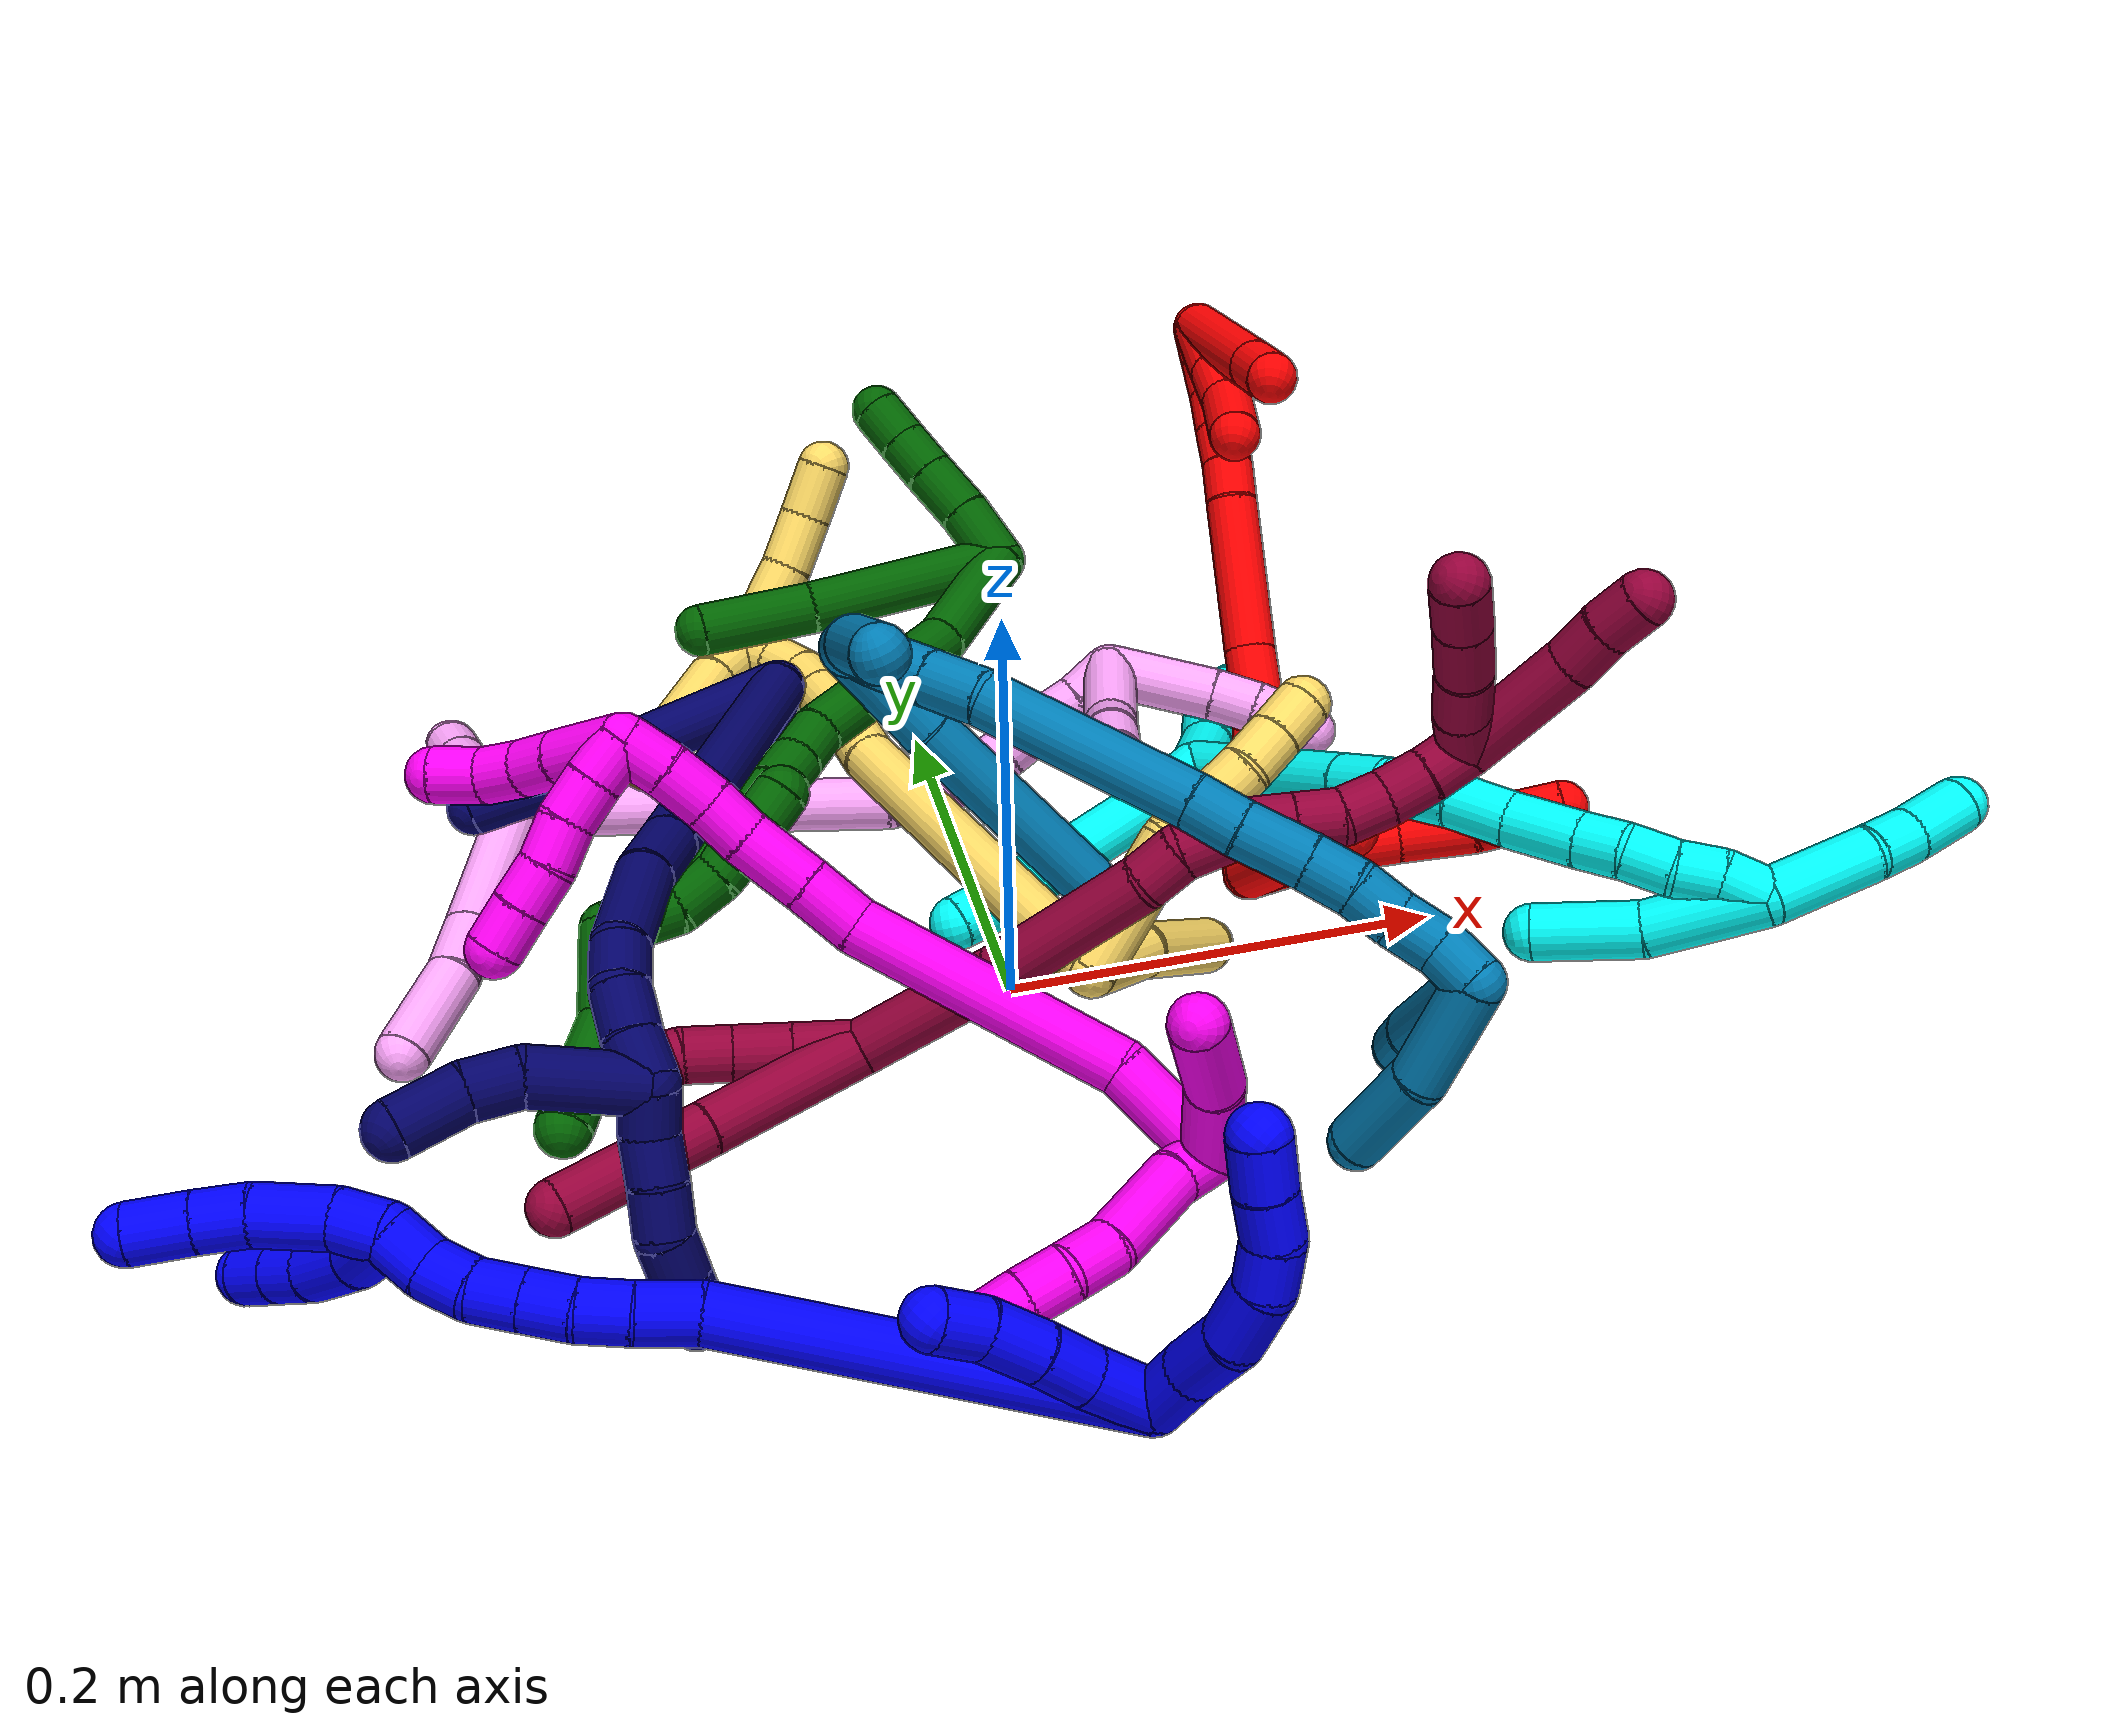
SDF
<sdf version="1.7">
 <world name="default">
  <plugin name="TubeGeneratorPlugin" filename="libtube_generator_plugin.so"/>
  <model name="photoneo_s_sensor">
   <static>1</static>
   <pose>0 0 2 1.57079 1.57079 3.14159</pose>
   <link name="link">
    <inertial><mass>0.1</mass></inertial>
    <sensor name="sensor" type="depth">
     <update_rate>30</update_rate>
     <camera>
      <horizontal_fov>1.22</horizontal_fov>
      <image><width>1920</width><height>1200</height><format>B8G8R8</format></image>
      <clip><near>0.1</near><far>4</far></clip>
      <depth_camera><output>points</output></depth_camera>
     </camera>
     <plugin name="camera_plugin" filename="libgazebo_ros_depth_camera.so">
      <baseline>0.2</baseline>
      <alwaysOn>1</alwaysOn>
      <updateRate>0.0</updateRate>
      <cameraName>camera_ir</cameraName>
      <imageTopicName>/camera/color/image_raw</imageTopicName>
      <cameraInfoTopicName>/camera/color/camera_info</cameraInfoTopicName>
      <depthImageTopicName>/camera/depth/image_raw</depthImageTopicName>
      <depthImageCameraInfoTopicName>/camera/depth/camera_info</depthImageCameraInfoTopicName>
      <pointCloudTopicName>/camera/depth/points</pointCloudTopicName>
      <frameName>fr_optical</frameName>
      <pointCloudCutoff>0.1</pointCloudCutoff>
      <pointCloudCutoffMax>2.0</pointCloudCutoffMax>
      <distortionK1>0</distortionK1>
      <distortionK2>0</distortionK2>
      <distortionK3>0</distortionK3>
      <distortionT1>0</distortionT1>
      <distortionT2>0</distortionT2>
      <CxPrime>0</CxPrime>
      <Cx>0</Cx>
      <Cy>0</Cy>
      <focalLength>0</focalLength>
      <hackBaseline>0</hackBaseline>
     </plugin>
    </sensor>
   </link>
  </model>
  <gravity>0 0 -9.8</gravity>
  <magnetic_field>6e-06 2.3e-05 -4.2e-05</magnetic_field>
  <atmosphere type="adiabatic"/>
  <physics name="default_physics" default="0" type="ode">
   <max_step_size>0.003</max_step_size>
   <real_time_factor>1</real_time_factor>
   <real_time_update_rate>1000</real_time_update_rate>
   <max_contacts>10000</max_contacts>
   <ode>
    <solver>
     <type>quick</type>
     <iters>100</iters>
     <sor>1.3</sor>
     <use_dynamic_moi_rescaling>0</use_dynamic_moi_rescaling>
    </solver>
    <constraints>
     <contact_max_correcting_vel>0</contact_max_correcting_vel>
     <contact_surface_layer>0.001</contact_surface_layer>
     <cfm>0</cfm>
     <erp>0.2</erp>
    </constraints>
   </ode>
  </physics>
  <scene><ambient>0.4 0.4 0.4 1</ambient><background>0.7 0.7 0.7 1</background><shadows>0</shadows></scene>
  <audio><device>default</device></audio>
  <spherical_coordinates>
   <surface_model>EARTH_WGS84</surface_model>
   <latitude_deg>0</latitude_deg>
   <longitude_deg>0</longitude_deg>
   <elevation>0</elevation>
   <heading_deg>0</heading_deg>
  </spherical_coordinates>
  <model name="bin">
   <static>1</static>
   <link name="bottom">
    <collision name="collision-bottom">
     <pose>0 0 -0.01 0 -0 0</pose>
     <geometry><box><size>0.8 0.6 0.02</size></box></geometry>
     <surface>
      <friction><ode><mu>100</mu><mu2>100</mu2></ode></friction>
      <contact><collide_bitmask>65535</collide_bitmask></contact>
     </surface>
    </collision>
   </link>
   <link name="west_wall">
    <collision name="collision-west_wall">
     <pose>-0.41 0 0.1 0 -0 0</pose>
     <geometry><box><size>0.02 0.6 0.2</size></box></geometry>
     <surface>
      <friction><ode><mu>100</mu><mu2>100</mu2></ode></friction>
      <contact><collide_bitmask>65535</collide_bitmask></contact>
     </surface>
    </collision>
   </link>
   <link name="east_wall">
    <collision name="collision-east_wall">
     <pose>0.41 0 0.1 0 -0 0</pose>
     <geometry><box><size>0.02 0.6 0.2</size></box></geometry>
     <surface>
      <friction><ode><mu>100</mu><mu2>100</mu2></ode></friction>
      <contact><collide_bitmask>65535</collide_bitmask></contact>
     </surface>
    </collision>
   </link>
   <link name="south_wall">
    <collision name="collision-south_wall">
     <pose>0 -0.31 0.1 0 -0 0</pose>
     <geometry><box><size>0.8 0.02 0.2</size></box></geometry>
     <surface>
      <friction><ode><mu>100</mu><mu2>100</mu2></ode></friction>
      <contact><collide_bitmask>65535</collide_bitmask></contact>
     </surface>
    </collision>
   </link>
   <link name="north_wall">
    <collision name="collision-north_wall">
     <pose>0 0.31 0.1 0 -0 0</pose>
     <geometry><box><size>0.8 0.02 0.2</size></box></geometry>
     <surface>
      <friction><ode><mu>100</mu><mu2>100</mu2></ode></friction>
      <contact><collide_bitmask>65535</collide_bitmask></contact>
     </surface>
    </collision>
   </link>
  </model>
  <model name="1">
   <static>0</static>
   <link name="1">
    <collision name="collision-cylinder-e_1_2_8">
     <pose>0.0136 2.9e-05 0.003592 -0.008194 1.31254 -0.006311</pose>
     <geometry><cylinder><radius>0.0125</radius><length>0.028134</length></cylinder></geometry>
     <surface>
      <friction><ode><mu>1.16</mu><mu2>1.16</mu2><slip1>0</slip1><slip2>0</slip2></ode></friction>
      <contact><ode><kp>1e+06</kp><kd>1</kd><max_vel>0</max_vel><min_depth>0.001</min_depth></ode></contact>
     </surface>
    </collision>
    <visual name="visual-cylinder-e_1_2_8">
     <pose>0.0136 2.9e-05 0.003592 -0.008194 1.31254 -0.006311</pose>
     <geometry><cylinder><radius>0.0125</radius><length>0.028134</length></cylinder></geometry>
     <material><ambient>0 0 1 1</ambient></material>
    </visual>
    <collision name="collision-cylinder-e_2_8_9">
     <pose>0.0419 0.001831 0.012054 -0.349066 1.2319 -0.248329</pose>
     <geometry><cylinder><radius>0.0125</radius><length>0.031171</length></cylinder></geometry>
     <surface>
      <friction><ode><mu>1.16</mu><mu2>1.16</mu2><slip1>0</slip1><slip2>0</slip2></ode></friction>
      <contact><ode><kp>1e+06</kp><kd>1</kd><max_vel>0</max_vel><min_depth>0.001</min_depth></ode></contact>
     </surface>
    </collision>
    <visual name="visual-cylinder-e_2_8_9">
     <pose>0.0419 0.001831 0.012054 -0.349066 1.2319 -0.248329</pose>
     <geometry><cylinder><radius>0.0125</radius><length>0.031171</length></cylinder></geometry>
     <material><ambient>0 0 1 1</ambient></material>
    </visual>
    <collision name="collision-cylinder-e_3_9_10">
     <pose>0.071014 0.003374 0.017667 0.298582 1.51684 0.283106</pose>
     <geometry><cylinder><radius>0.0125</radius><length>0.028873</length></cylinder></geometry>
     <surface>
      <friction><ode><mu>1.16</mu><mu2>1.16</mu2><slip1>0</slip1><slip2>0</slip2></ode></friction>
      <contact><ode><kp>1e+06</kp><kd>1</kd><max_vel>0</max_vel><min_depth>0.001</min_depth></ode></contact>
     </surface>
    </collision>
    <visual name="visual-cylinder-e_3_9_10">
     <pose>0.071014 0.003374 0.017667 0.298582 1.51684 0.283106</pose>
     <geometry><cylinder><radius>0.0125</radius><length>0.028873</length></cylinder></geometry>
     <material><ambient>0 0 1 1</ambient></material>
    </visual>
    <collision name="collision-cylinder-e_4_10_11">
     <pose>0.095243 0.002716 0.015578 2.99129 1.2867 2.94142</pose>
     <geometry><cylinder><radius>0.0125</radius><length>0.020446</length></cylinder></geometry>
     <surface>
      <friction><ode><mu>1.16</mu><mu2>1.16</mu2><slip1>0</slip1><slip2>0</slip2></ode></friction>
      <contact><ode><kp>1e+06</kp><kd>1</kd><max_vel>0</max_vel><min_depth>0.001</min_depth></ode></contact>
     </surface>
    </collision>
    <visual name="visual-cylinder-e_4_10_11">
     <pose>0.095243 0.002716 0.015578 2.99129 1.2867 2.94142</pose>
     <geometry><cylinder><radius>0.0125</radius><length>0.020446</length></cylinder></geometry>
     <material><ambient>0 0 1 1</ambient></material>
    </visual>
    <collision name="collision-cylinder-e_5_11_12">
     <pose>0.113639 0.003677 0.007627 -2.87633 1.01734 -2.67189</pose>
     <geometry><cylinder><radius>0.0125</radius><length>0.020178</length></cylinder></geometry>
     <surface>
      <friction><ode><mu>1.16</mu><mu2>1.16</mu2><slip1>0</slip1><slip2>0</slip2></ode></friction>
      <contact><ode><kp>1e+06</kp><kd>1</kd><max_vel>0</max_vel><min_depth>0.001</min_depth></ode></contact>
     </surface>
    </collision>
    <visual name="visual-cylinder-e_5_11_12">
     <pose>0.113639 0.003677 0.007627 -2.87633 1.01734 -2.67189</pose>
     <geometry><cylinder><radius>0.0125</radius><length>0.020178</length></cylinder></geometry>
     <material><ambient>0 0 1 1</ambient></material>
    </visual>
    <collision name="collision-cylinder-e_6_12_6">
     <pose>0.131389 0.005741 -0.002767 -3.01458 1.04501 -2.92164</pose>
     <geometry><cylinder><radius>0.0125</radius><length>0.021199</length></cylinder></geometry>
     <surface>
      <friction><ode><mu>1.16</mu><mu2>1.16</mu2><slip1>0</slip1><slip2>0</slip2></ode></friction>
      <contact><ode><kp>1e+06</kp><kd>1</kd><max_vel>0</max_vel><min_depth>0.001</min_depth></ode></contact>
     </surface>
    </collision>
    <visual name="visual-cylinder-e_6_12_6">
     <pose>0.131389 0.005741 -0.002767 -3.01458 1.04501 -2.92164</pose>
     <geometry><cylinder><radius>0.0125</radius><length>0.021199</length></cylinder></geometry>
     <material><ambient>0 0 1 1</ambient></material>
    </visual>
    <collision name="collision-cylinder-e_1_2_13">
     <pose>0.004699 0.010778 -0.010511 -2.34363 0.302546 -0.693898</pose>
     <geometry><cylinder><radius>0.0125</radius><length>0.031542</length></cylinder></geometry>
     <surface>
      <friction><ode><mu>1.16</mu><mu2>1.16</mu2><slip1>0</slip1><slip2>0</slip2></ode></friction>
      <contact><ode><kp>1e+06</kp><kd>1</kd><max_vel>0</max_vel><min_depth>0.001</min_depth></ode></contact>
     </surface>
    </collision>
    <visual name="visual-cylinder-e_1_2_13">
     <pose>0.004699 0.010778 -0.010511 -2.34363 0.302546 -0.693898</pose>
     <geometry><cylinder><radius>0.0125</radius><length>0.031542</length></cylinder></geometry>
     <material><ambient>0 0 1 1</ambient></material>
    </visual>
    <collision name="collision-cylinder-e_2_13_14">
     <pose>0.013182 0.028913 -0.028458 -2.36161 0.34708 -0.806254</pose>
     <geometry><cylinder><radius>0.0125</radius><length>0.022248</length></cylinder></geometry>
     <surface>
      <friction><ode><mu>1.16</mu><mu2>1.16</mu2><slip1>0</slip1><slip2>0</slip2></ode></friction>
      <contact><ode><kp>1e+06</kp><kd>1</kd><max_vel>0</max_vel><min_depth>0.001</min_depth></ode></contact>
     </surface>
    </collision>
    <visual name="visual-cylinder-e_2_13_14">
     <pose>0.013182 0.028913 -0.028458 -2.36161 0.34708 -0.806254</pose>
     <geometry><cylinder><radius>0.0125</radius><length>0.022248</length></cylinder></geometry>
     <material><ambient>0 0 1 1</ambient></material>
    </visual>
    <collision name="collision-cylinder-e_3_14_15">
     <pose>0.020264 0.044645 -0.044642 -2.37785 0.265874 -0.642891</pose>
     <geometry><cylinder><radius>0.0125</radius><length>0.025103</length></cylinder></geometry>
     <surface>
      <friction><ode><mu>1.16</mu><mu2>1.16</mu2><slip1>0</slip1><slip2>0</slip2></ode></friction>
      <contact><ode><kp>1e+06</kp><kd>1</kd><max_vel>0</max_vel><min_depth>0.001</min_depth></ode></contact>
     </surface>
    </collision>
    <visual name="visual-cylinder-e_3_14_15">
     <pose>0.020264 0.044645 -0.044642 -2.37785 0.265874 -0.642891</pose>
     <geometry><cylinder><radius>0.0125</radius><length>0.025103</length></cylinder></geometry>
     <material><ambient>0 0 1 1</ambient></material>
    </visual>
    <collision name="collision-cylinder-e_4_15_5">
     <pose>0.025198 0.061423 -0.059562 -2.20445 0.155678 -0.305778</pose>
     <geometry><cylinder><radius>0.0125</radius><length>0.021107</length></cylinder></geometry>
     <surface>
      <friction><ode><mu>1.16</mu><mu2>1.16</mu2><slip1>0</slip1><slip2>0</slip2></ode></friction>
      <contact><ode><kp>1e+06</kp><kd>1</kd><max_vel>0</max_vel><min_depth>0.001</min_depth></ode></contact>
     </surface>
    </collision>
    <visual name="visual-cylinder-e_4_15_5">
     <pose>0.025198 0.061423 -0.059562 -2.20445 0.155678 -0.305778</pose>
     <geometry><cylinder><radius>0.0125</radius><length>0.021107</length></cylinder></geometry>
     <material><ambient>0 0 1 1</ambient></material>
    </visual>
    <collision name="collision-cylinder-e_1_2_16">
     <pose>-0.008932 0.05243 -0.068711 -2.48979 -0.102979 0.302653</pose>
     <geometry><cylinder><radius>0.0125</radius><length>0.17378</length></cylinder></geometry>
     <surface>
      <friction><ode><mu>1.16</mu><mu2>1.16</mu2><slip1>0</slip1><slip2>0</slip2></ode></friction>
      <contact><ode><kp>1e+06</kp><kd>1</kd><max_vel>0</max_vel><min_depth>0.001</min_depth></ode></contact>
     </surface>
    </collision>
    <visual name="visual-cylinder-e_1_2_16">
     <pose>-0.008932 0.05243 -0.068711 -2.48979 -0.102979 0.302653</pose>
     <geometry><cylinder><radius>0.0125</radius><length>0.17378</length></cylinder></geometry>
     <material><ambient>0 0 1 1</ambient></material>
    </visual>
    <collision name="collision-cylinder-e_2_16_17">
     <pose>-0.020391 0.114026 -0.145684 -2.30443 -0.201961 0.447886</pose>
     <geometry><cylinder><radius>0.0125</radius><length>0.025194</length></cylinder></geometry>
     <surface>
      <friction><ode><mu>1.16</mu><mu2>1.16</mu2><slip1>0</slip1><slip2>0</slip2></ode></friction>
      <contact><ode><kp>1e+06</kp><kd>1</kd><max_vel>0</max_vel><min_depth>0.001</min_depth></ode></contact>
     </surface>
    </collision>
    <visual name="visual-cylinder-e_2_16_17">
     <pose>-0.020391 0.114026 -0.145684 -2.30443 -0.201961 0.447886</pose>
     <geometry><cylinder><radius>0.0125</radius><length>0.025194</length></cylinder></geometry>
     <material><ambient>0 0 1 1</ambient></material>
    </visual>
    <collision name="collision-cylinder-e_3_17_18">
     <pose>-0.025432 0.129792 -0.161617 -2.43104 -0.24356 0.63725</pose>
     <geometry><cylinder><radius>0.0125</radius><length>0.020854</length></cylinder></geometry>
     <surface>
      <friction><ode><mu>1.16</mu><mu2>1.16</mu2><slip1>0</slip1><slip2>0</slip2></ode></friction>
      <contact><ode><kp>1e+06</kp><kd>1</kd><max_vel>0</max_vel><min_depth>0.001</min_depth></ode></contact>
     </surface>
    </collision>
    <visual name="visual-cylinder-e_3_17_18">
     <pose>-0.025432 0.129792 -0.161617 -2.43104 -0.24356 0.63725</pose>
     <geometry><cylinder><radius>0.0125</radius><length>0.020854</length></cylinder></geometry>
     <material><ambient>0 0 1 1</ambient></material>
    </visual>
    <collision name="collision-cylinder-e_4_18_19">
     <pose>-0.030361 0.141238 -0.177713 -2.61974 -0.243447 0.859194</pose>
     <geometry><cylinder><radius>0.0125</radius><length>0.02003</length></cylinder></geometry>
     <surface>
      <friction><ode><mu>1.16</mu><mu2>1.16</mu2><slip1>0</slip1><slip2>0</slip2></ode></friction>
      <contact><ode><kp>1e+06</kp><kd>1</kd><max_vel>0</max_vel><min_depth>0.001</min_depth></ode></contact>
     </surface>
    </collision>
    <visual name="visual-cylinder-e_4_18_19">
     <pose>-0.030361 0.141238 -0.177713 -2.61974 -0.243447 0.859194</pose>
     <geometry><cylinder><radius>0.0125</radius><length>0.02003</length></cylinder></geometry>
     <material><ambient>0 0 1 1</ambient></material>
    </visual>
    <collision name="collision-cylinder-e_5_19_20">
     <pose>-0.035127 0.150985 -0.194588 -2.61583 -0.23629 0.830822</pose>
     <geometry><cylinder><radius>0.0125</radius><length>0.020094</length></cylinder></geometry>
     <surface>
      <friction><ode><mu>1.16</mu><mu2>1.16</mu2><slip1>0</slip1><slip2>0</slip2></ode></friction>
      <contact><ode><kp>1e+06</kp><kd>1</kd><max_vel>0</max_vel><min_depth>0.001</min_depth></ode></contact>
     </surface>
    </collision>
    <visual name="visual-cylinder-e_5_19_20">
     <pose>-0.035127 0.150985 -0.194588 -2.61583 -0.23629 0.830822</pose>
     <geometry><cylinder><radius>0.0125</radius><length>0.020094</length></cylinder></geometry>
     <material><ambient>0 0 1 1</ambient></material>
    </visual>
    <collision name="collision-cylinder-e_6_20_21">
     <pose>-0.038988 0.15844 -0.212591 -2.88045 -0.151464 1.04789</pose>
     <geometry><cylinder><radius>0.0125</radius><length>0.02001</length></cylinder></geometry>
     <surface>
      <friction><ode><mu>1.16</mu><mu2>1.16</mu2><slip1>0</slip1><slip2>0</slip2></ode></friction>
      <contact><ode><kp>1e+06</kp><kd>1</kd><max_vel>0</max_vel><min_depth>0.001</min_depth></ode></contact>
     </surface>
    </collision>
    <visual name="visual-cylinder-e_6_20_21">
     <pose>-0.038988 0.15844 -0.212591 -2.88045 -0.151464 1.04789</pose>
     <geometry><cylinder><radius>0.0125</radius><length>0.02001</length></cylinder></geometry>
     <material><ambient>0 0 1 1</ambient></material>
    </visual>
    <collision name="collision-cylinder-e_7_21_1">
     <pose>-0.03877 0.16325 -0.231755 -2.911 0.173359 -1.28745</pose>
     <geometry><cylinder><radius>0.0125</radius><length>0.02004</length></cylinder></geometry>
     <surface>
      <friction><ode><mu>1.16</mu><mu2>1.16</mu2><slip1>0</slip1><slip2>0</slip2></ode></friction>
      <contact><ode><kp>1e+06</kp><kd>1</kd><max_vel>0</max_vel><min_depth>0.001</min_depth></ode></contact>
     </surface>
    </collision>
    <visual name="visual-cylinder-e_7_21_1">
     <pose>-0.03877 0.16325 -0.231755 -2.911 0.173359 -1.28745</pose>
     <geometry><cylinder><radius>0.0125</radius><length>0.02004</length></cylinder></geometry>
     <material><ambient>0 0 1 1</ambient></material>
    </visual>
    <collision name="collision-cylinder-e_1_1_22">
     <pose>-0.050195 0.164443 -0.247762 2.97698 -1.11272 -2.87784</pose>
     <geometry><cylinder><radius>0.0125</radius><length>0.029332</length></cylinder></geometry>
     <surface>
      <friction><ode><mu>1.16</mu><mu2>1.16</mu2><slip1>0</slip1><slip2>0</slip2></ode></friction>
      <contact><ode><kp>1e+06</kp><kd>1</kd><max_vel>0</max_vel><min_depth>0.001</min_depth></ode></contact>
     </surface>
    </collision>
    <visual name="visual-cylinder-e_1_1_22">
     <pose>-0.050195 0.164443 -0.247762 2.97698 -1.11272 -2.87784</pose>
     <geometry><cylinder><radius>0.0125</radius><length>0.029332</length></cylinder></geometry>
     <material><ambient>0 0 1 1</ambient></material>
    </visual>
    <collision name="collision-cylinder-e_2_22_23">
     <pose>-0.075199 0.164472 -0.263243 -3.02198 -0.913352 2.89905</pose>
     <geometry><cylinder><radius>0.0125</radius><length>0.029941</length></cylinder></geometry>
     <surface>
      <friction><ode><mu>1.16</mu><mu2>1.16</mu2><slip1>0</slip1><slip2>0</slip2></ode></friction>
      <contact><ode><kp>1e+06</kp><kd>1</kd><max_vel>0</max_vel><min_depth>0.001</min_depth></ode></contact>
     </surface>
    </collision>
    <visual name="visual-cylinder-e_2_22_23">
     <pose>-0.075199 0.164472 -0.263243 -3.02198 -0.913352 2.89905</pose>
     <geometry><cylinder><radius>0.0125</radius><length>0.029941</length></cylinder></geometry>
     <material><ambient>0 0 1 1</ambient></material>
    </visual>
    <collision name="collision-cylinder-e_3_23_24">
     <pose>-0.094024 0.166611 -0.27972 -3.00084 -0.751278 2.78783</pose>
     <geometry><cylinder><radius>0.0125</radius><length>0.020438</length></cylinder></geometry>
     <surface>
      <friction><ode><mu>1.16</mu><mu2>1.16</mu2><slip1>0</slip1><slip2>0</slip2></ode></friction>
      <contact><ode><kp>1e+06</kp><kd>1</kd><max_vel>0</max_vel><min_depth>0.001</min_depth></ode></contact>
     </surface>
    </collision>
    <visual name="visual-cylinder-e_3_23_24">
     <pose>-0.094024 0.166611 -0.27972 -3.00084 -0.751278 2.78783</pose>
     <geometry><cylinder><radius>0.0125</radius><length>0.020438</length></cylinder></geometry>
     <material><ambient>0 0 1 1</ambient></material>
    </visual>
    <collision name="collision-cylinder-e_4_24_4">
     <pose>-0.107927 0.168829 -0.294433 -2.98298 -0.751656 2.74408</pose>
     <geometry><cylinder><radius>0.0125</radius><length>0.020289</length></cylinder></geometry>
     <surface>
      <friction><ode><mu>1.16</mu><mu2>1.16</mu2><slip1>0</slip1><slip2>0</slip2></ode></friction>
      <contact><ode><kp>1e+06</kp><kd>1</kd><max_vel>0</max_vel><min_depth>0.001</min_depth></ode></contact>
     </surface>
    </collision>
    <visual name="visual-cylinder-e_4_24_4">
     <pose>-0.107927 0.168829 -0.294433 -2.98298 -0.751656 2.74408</pose>
     <geometry><cylinder><radius>0.0125</radius><length>0.020289</length></cylinder></geometry>
     <material><ambient>0 0 1 1</ambient></material>
    </visual>
    <collision name="collision-cylinder-e_1_1_25">
     <pose>-0.039529 0.169625 -0.250946 -2.73555 -0.2341 1.03797</pose>
     <geometry><cylinder><radius>0.0125</radius><length>0.021446</length></cylinder></geometry>
     <surface>
      <friction><ode><mu>1.16</mu><mu2>1.16</mu2><slip1>0</slip1><slip2>0</slip2></ode></friction>
      <contact><ode><kp>1e+06</kp><kd>1</kd><max_vel>0</max_vel><min_depth>0.001</min_depth></ode></contact>
     </surface>
    </collision>
    <visual name="visual-cylinder-e_1_1_25">
     <pose>-0.039529 0.169625 -0.250946 -2.73555 -0.2341 1.03797</pose>
     <geometry><cylinder><radius>0.0125</radius><length>0.021446</length></cylinder></geometry>
     <material><ambient>0 0 1 1</ambient></material>
    </visual>
    <collision name="collision-cylinder-e_2_25_26">
     <pose>-0.046436 0.183374 -0.272322 -2.45691 -0.282535 0.759394</pose>
     <geometry><cylinder><radius>0.0125</radius><length>0.031706</length></cylinder></geometry>
     <surface>
      <friction><ode><mu>1.16</mu><mu2>1.16</mu2><slip1>0</slip1><slip2>0</slip2></ode></friction>
      <contact><ode><kp>1e+06</kp><kd>1</kd><max_vel>0</max_vel><min_depth>0.001</min_depth></ode></contact>
     </surface>
    </collision>
    <visual name="visual-cylinder-e_2_25_26">
     <pose>-0.046436 0.183374 -0.272322 -2.45691 -0.282535 0.759394</pose>
     <geometry><cylinder><radius>0.0125</radius><length>0.031706</length></cylinder></geometry>
     <material><ambient>0 0 1 1</ambient></material>
    </visual>
    <collision name="collision-cylinder-e_3_26_27">
     <pose>-0.054954 0.200287 -0.290595 -2.29775 -0.397963 0.844428</pose>
     <geometry><cylinder><radius>0.0125</radius><length>0.021152</length></cylinder></geometry>
     <surface>
      <friction><ode><mu>1.16</mu><mu2>1.16</mu2><slip1>0</slip1><slip2>0</slip2></ode></friction>
      <contact><ode><kp>1e+06</kp><kd>1</kd><max_vel>0</max_vel><min_depth>0.001</min_depth></ode></contact>
     </surface>
    </collision>
    <visual name="visual-cylinder-e_3_26_27">
     <pose>-0.054954 0.200287 -0.290595 -2.29775 -0.397963 0.844428</pose>
     <geometry><cylinder><radius>0.0125</radius><length>0.021152</length></cylinder></geometry>
     <material><ambient>0 0 1 1</ambient></material>
    </visual>
    <collision name="collision-cylinder-e_4_27_3">
     <pose>-0.064051 0.216798 -0.304488 -2.2477 -0.399616 0.799532</pose>
     <geometry><cylinder><radius>0.0125</radius><length>0.025695</length></cylinder></geometry>
     <surface>
      <friction><ode><mu>1.16</mu><mu2>1.16</mu2><slip1>0</slip1><slip2>0</slip2></ode></friction>
      <contact><ode><kp>1e+06</kp><kd>1</kd><max_vel>0</max_vel><min_depth>0.001</min_depth></ode></contact>
     </surface>
    </collision>
    <visual name="visual-cylinder-e_4_27_3">
     <pose>-0.064051 0.216798 -0.304488 -2.2477 -0.399616 0.799532</pose>
     <geometry><cylinder><radius>0.0125</radius><length>0.025695</length></cylinder></geometry>
     <material><ambient>0 0 1 1</ambient></material>
    </visual>
    <collision name="collision-sphere-3">
     <pose>-0.06905 0.226024 -0.311901 0 -0 0</pose>
     <geometry><sphere><radius>0.0125</radius></sphere></geometry>
     <surface>
      <friction><ode><mu>1.16</mu><mu2>1.16</mu2><slip1>0</slip1><slip2>0</slip2></ode></friction>
      <contact><ode><kp>1e+06</kp><kd>1</kd><max_vel>0</max_vel><min_depth>0.001</min_depth></ode></contact>
     </surface>
    </collision>
    <visual name="visual-sphere-3">
     <pose>-0.06905 0.226024 -0.311901 0 -0 0</pose>
     <geometry><sphere><radius>0.0125</radius></sphere></geometry>
     <material><ambient>0 0 1 1</ambient></material>
    </visual>
    <collision name="collision-sphere-27">
     <pose>-0.059053 0.207572 -0.297075 0 -0 0</pose>
     <geometry><sphere><radius>0.0125</radius></sphere></geometry>
     <surface>
      <friction><ode><mu>1.16</mu><mu2>1.16</mu2><slip1>0</slip1><slip2>0</slip2></ode></friction>
      <contact><ode><kp>1e+06</kp><kd>1</kd><max_vel>0</max_vel><min_depth>0.001</min_depth></ode></contact>
     </surface>
    </collision>
    <visual name="visual-sphere-27">
     <pose>-0.059053 0.207572 -0.297075 0 -0 0</pose>
     <geometry><sphere><radius>0.0125</radius></sphere></geometry>
     <material><ambient>0 0 1 1</ambient></material>
    </visual>
    <collision name="collision-sphere-26">
     <pose>-0.050855 0.193002 -0.284115 0 -0 0</pose>
     <geometry><sphere><radius>0.0125</radius></sphere></geometry>
     <surface>
      <friction><ode><mu>1.16</mu><mu2>1.16</mu2><slip1>0</slip1><slip2>0</slip2></ode></friction>
      <contact><ode><kp>1e+06</kp><kd>1</kd><max_vel>0</max_vel><min_depth>0.001</min_depth></ode></contact>
     </surface>
    </collision>
    <visual name="visual-sphere-26">
     <pose>-0.050855 0.193002 -0.284115 0 -0 0</pose>
     <geometry><sphere><radius>0.0125</radius></sphere></geometry>
     <material><ambient>0 0 1 1</ambient></material>
    </visual>
    <collision name="collision-sphere-25">
     <pose>-0.042016 0.173745 -0.260529 0 -0 0</pose>
     <geometry><sphere><radius>0.0125</radius></sphere></geometry>
     <surface>
      <friction><ode><mu>1.16</mu><mu2>1.16</mu2><slip1>0</slip1><slip2>0</slip2></ode></friction>
      <contact><ode><kp>1e+06</kp><kd>1</kd><max_vel>0</max_vel><min_depth>0.001</min_depth></ode></contact>
     </surface>
    </collision>
    <visual name="visual-sphere-25">
     <pose>-0.042016 0.173745 -0.260529 0 -0 0</pose>
     <geometry><sphere><radius>0.0125</radius></sphere></geometry>
     <material><ambient>0 0 1 1</ambient></material>
    </visual>
    <collision name="collision-sphere-4">
     <pose>-0.114854 0.17 -0.301751 0 -0 0</pose>
     <geometry><sphere><radius>0.0125</radius></sphere></geometry>
     <surface>
      <friction><ode><mu>1.16</mu><mu2>1.16</mu2><slip1>0</slip1><slip2>0</slip2></ode></friction>
      <contact><ode><kp>1e+06</kp><kd>1</kd><max_vel>0</max_vel><min_depth>0.001</min_depth></ode></contact>
     </surface>
    </collision>
    <visual name="visual-sphere-4">
     <pose>-0.114854 0.17 -0.301751 0 -0 0</pose>
     <geometry><sphere><radius>0.0125</radius></sphere></geometry>
     <material><ambient>0 0 1 1</ambient></material>
    </visual>
    <collision name="collision-sphere-24">
     <pose>-0.101 0.167659 -0.287115 0 -0 0</pose>
     <geometry><sphere><radius>0.0125</radius></sphere></geometry>
     <surface>
      <friction><ode><mu>1.16</mu><mu2>1.16</mu2><slip1>0</slip1><slip2>0</slip2></ode></friction>
      <contact><ode><kp>1e+06</kp><kd>1</kd><max_vel>0</max_vel><min_depth>0.001</min_depth></ode></contact>
     </surface>
    </collision>
    <visual name="visual-sphere-24">
     <pose>-0.101 0.167659 -0.287115 0 -0 0</pose>
     <geometry><sphere><radius>0.0125</radius></sphere></geometry>
     <material><ambient>0 0 1 1</ambient></material>
    </visual>
    <collision name="collision-sphere-23">
     <pose>-0.087049 0.165563 -0.272326 0 -0 0</pose>
     <geometry><sphere><radius>0.0125</radius></sphere></geometry>
     <surface>
      <friction><ode><mu>1.16</mu><mu2>1.16</mu2><slip1>0</slip1><slip2>0</slip2></ode></friction>
      <contact><ode><kp>1e+06</kp><kd>1</kd><max_vel>0</max_vel><min_depth>0.001</min_depth></ode></contact>
     </surface>
    </collision>
    <visual name="visual-sphere-23">
     <pose>-0.087049 0.165563 -0.272326 0 -0 0</pose>
     <geometry><sphere><radius>0.0125</radius></sphere></geometry>
     <material><ambient>0 0 1 1</ambient></material>
    </visual>
    <collision name="collision-sphere-22">
     <pose>-0.063349 0.16338 -0.25416 0 -0 0</pose>
     <geometry><sphere><radius>0.0125</radius></sphere></geometry>
     <surface>
      <friction><ode><mu>1.16</mu><mu2>1.16</mu2><slip1>0</slip1><slip2>0</slip2></ode></friction>
      <contact><ode><kp>1e+06</kp><kd>1</kd><max_vel>0</max_vel><min_depth>0.001</min_depth></ode></contact>
     </surface>
    </collision>
    <visual name="visual-sphere-22">
     <pose>-0.063349 0.16338 -0.25416 0 -0 0</pose>
     <geometry><sphere><radius>0.0125</radius></sphere></geometry>
     <material><ambient>0 0 1 1</ambient></material>
    </visual>
    <collision name="collision-sphere-1">
     <pose>-0.037041 0.165506 -0.241364 0 -0 0</pose>
     <geometry><sphere><radius>0.0125</radius></sphere></geometry>
     <surface>
      <friction><ode><mu>1.16</mu><mu2>1.16</mu2><slip1>0</slip1><slip2>0</slip2></ode></friction>
      <contact><ode><kp>1e+06</kp><kd>1</kd><max_vel>0</max_vel><min_depth>0.001</min_depth></ode></contact>
     </surface>
    </collision>
    <visual name="visual-sphere-1">
     <pose>-0.037041 0.165506 -0.241364 0 -0 0</pose>
     <geometry><sphere><radius>0.0125</radius></sphere></geometry>
     <material><ambient>0 0 1 1</ambient></material>
    </visual>
    <collision name="collision-sphere-21">
     <pose>-0.040498 0.160994 -0.222146 0 -0 0</pose>
     <geometry><sphere><radius>0.0125</radius></sphere></geometry>
     <surface>
      <friction><ode><mu>1.16</mu><mu2>1.16</mu2><slip1>0</slip1><slip2>0</slip2></ode></friction>
      <contact><ode><kp>1e+06</kp><kd>1</kd><max_vel>0</max_vel><min_depth>0.001</min_depth></ode></contact>
     </surface>
    </collision>
    <visual name="visual-sphere-21">
     <pose>-0.040498 0.160994 -0.222146 0 -0 0</pose>
     <geometry><sphere><radius>0.0125</radius></sphere></geometry>
     <material><ambient>0 0 1 1</ambient></material>
    </visual>
    <collision name="collision-sphere-12">
     <pose>0.122221 0.005068 0.00251 0 -0 0</pose>
     <geometry><sphere><radius>0.0125</radius></sphere></geometry>
     <surface>
      <friction><ode><mu>1.16</mu><mu2>1.16</mu2><slip1>0</slip1><slip2>0</slip2></ode></friction>
      <contact><ode><kp>1e+06</kp><kd>1</kd><max_vel>0</max_vel><min_depth>0.001</min_depth></ode></contact>
     </surface>
    </collision>
    <visual name="visual-sphere-12">
     <pose>0.122221 0.005068 0.00251 0 -0 0</pose>
     <geometry><sphere><radius>0.0125</radius></sphere></geometry>
     <material><ambient>0 0 1 1</ambient></material>
    </visual>
    <collision name="collision-sphere-11">
     <pose>0.105056 0.002287 0.012745 0 -0 0</pose>
     <geometry><sphere><radius>0.0125</radius></sphere></geometry>
     <surface>
      <friction><ode><mu>1.16</mu><mu2>1.16</mu2><slip1>0</slip1><slip2>0</slip2></ode></friction>
      <contact><ode><kp>1e+06</kp><kd>1</kd><max_vel>0</max_vel><min_depth>0.001</min_depth></ode></contact>
     </surface>
    </collision>
    <visual name="visual-sphere-11">
     <pose>0.105056 0.002287 0.012745 0 -0 0</pose>
     <geometry><sphere><radius>0.0125</radius></sphere></geometry>
     <material><ambient>0 0 1 1</ambient></material>
    </visual>
    <collision name="collision-sphere-10">
     <pose>0.08543 0.003145 0.018411 0 -0 0</pose>
     <geometry><sphere><radius>0.0125</radius></sphere></geometry>
     <surface>
      <friction><ode><mu>1.16</mu><mu2>1.16</mu2><slip1>0</slip1><slip2>0</slip2></ode></friction>
      <contact><ode><kp>1e+06</kp><kd>1</kd><max_vel>0</max_vel><min_depth>0.001</min_depth></ode></contact>
     </surface>
    </collision>
    <visual name="visual-sphere-10">
     <pose>0.08543 0.003145 0.018411 0 -0 0</pose>
     <geometry><sphere><radius>0.0125</radius></sphere></geometry>
     <material><ambient>0 0 1 1</ambient></material>
    </visual>
    <collision name="collision-sphere-9">
     <pose>0.056599 0.003603 0.016923 0 -0 0</pose>
     <geometry><sphere><radius>0.0125</radius></sphere></geometry>
     <surface>
      <friction><ode><mu>1.16</mu><mu2>1.16</mu2><slip1>0</slip1><slip2>0</slip2></ode></friction>
      <contact><ode><kp>1e+06</kp><kd>1</kd><max_vel>0</max_vel><min_depth>0.001</min_depth></ode></contact>
     </surface>
    </collision>
    <visual name="visual-sphere-9">
     <pose>0.056599 0.003603 0.016923 0 -0 0</pose>
     <geometry><sphere><radius>0.0125</radius></sphere></geometry>
     <material><ambient>0 0 1 1</ambient></material>
    </visual>
    <collision name="collision-sphere-2">
     <geometry><sphere><radius>0.0125</radius></sphere></geometry>
     <surface>
      <friction><ode><mu>1.16</mu><mu2>1.16</mu2><slip1>0</slip1><slip2>0</slip2></ode></friction>
      <contact><ode><kp>1e+06</kp><kd>1</kd><max_vel>0</max_vel><min_depth>0.001</min_depth></ode></contact>
     </surface>
    </collision>
    <visual name="visual-sphere-2">
     <geometry><sphere><radius>0.0125</radius></sphere></geometry>
     <material><ambient>0 0 1 1</ambient></material>
    </visual>
    <collision name="collision-sphere-19">
     <pose>-0.032775 0.146083 -0.186139 0 -0 0</pose>
     <geometry><sphere><radius>0.0125</radius></sphere></geometry>
     <surface>
      <friction><ode><mu>1.16</mu><mu2>1.16</mu2><slip1>0</slip1><slip2>0</slip2></ode></friction>
      <contact><ode><kp>1e+06</kp><kd>1</kd><max_vel>0</max_vel><min_depth>0.001</min_depth></ode></contact>
     </surface>
    </collision>
    <visual name="visual-sphere-19">
     <pose>-0.032775 0.146083 -0.186139 0 -0 0</pose>
     <geometry><sphere><radius>0.0125</radius></sphere></geometry>
     <material><ambient>0 0 1 1</ambient></material>
    </visual>
    <collision name="collision-sphere-8">
     <pose>0.027201 5.9e-05 0.007185 0 -0 0</pose>
     <geometry><sphere><radius>0.0125</radius></sphere></geometry>
     <surface>
      <friction><ode><mu>1.16</mu><mu2>1.16</mu2><slip1>0</slip1><slip2>0</slip2></ode></friction>
      <contact><ode><kp>1e+06</kp><kd>1</kd><max_vel>0</max_vel><min_depth>0.001</min_depth></ode></contact>
     </surface>
    </collision>
    <visual name="visual-sphere-8">
     <pose>0.027201 5.9e-05 0.007185 0 -0 0</pose>
     <geometry><sphere><radius>0.0125</radius></sphere></geometry>
     <material><ambient>0 0 1 1</ambient></material>
    </visual>
    <collision name="collision-sphere-6">
     <pose>0.140557 0.006415 -0.008044 0 -0 0</pose>
     <geometry><sphere><radius>0.0125</radius></sphere></geometry>
     <surface>
      <friction><ode><mu>1.16</mu><mu2>1.16</mu2><slip1>0</slip1><slip2>0</slip2></ode></friction>
      <contact><ode><kp>1e+06</kp><kd>1</kd><max_vel>0</max_vel><min_depth>0.001</min_depth></ode></contact>
     </surface>
    </collision>
    <visual name="visual-sphere-6">
     <pose>0.140557 0.006415 -0.008044 0 -0 0</pose>
     <geometry><sphere><radius>0.0125</radius></sphere></geometry>
     <material><ambient>0 0 1 1</ambient></material>
    </visual>
    <collision name="collision-sphere-13">
     <pose>0.009398 0.021556 -0.021021 0 -0 0</pose>
     <geometry><sphere><radius>0.0125</radius></sphere></geometry>
     <surface>
      <friction><ode><mu>1.16</mu><mu2>1.16</mu2><slip1>0</slip1><slip2>0</slip2></ode></friction>
      <contact><ode><kp>1e+06</kp><kd>1</kd><max_vel>0</max_vel><min_depth>0.001</min_depth></ode></contact>
     </surface>
    </collision>
    <visual name="visual-sphere-13">
     <pose>0.009398 0.021556 -0.021021 0 -0 0</pose>
     <geometry><sphere><radius>0.0125</radius></sphere></geometry>
     <material><ambient>0 0 1 1</ambient></material>
    </visual>
    <collision name="collision-sphere-14">
     <pose>0.016966 0.036269 -0.035895 0 -0 0</pose>
     <geometry><sphere><radius>0.0125</radius></sphere></geometry>
     <surface>
      <friction><ode><mu>1.16</mu><mu2>1.16</mu2><slip1>0</slip1><slip2>0</slip2></ode></friction>
      <contact><ode><kp>1e+06</kp><kd>1</kd><max_vel>0</max_vel><min_depth>0.001</min_depth></ode></contact>
     </surface>
    </collision>
    <visual name="visual-sphere-14">
     <pose>0.016966 0.036269 -0.035895 0 -0 0</pose>
     <geometry><sphere><radius>0.0125</radius></sphere></geometry>
     <material><ambient>0 0 1 1</ambient></material>
    </visual>
    <collision name="collision-sphere-15">
     <pose>0.023562 0.053021 -0.053388 0 -0 0</pose>
     <geometry><sphere><radius>0.0125</radius></sphere></geometry>
     <surface>
      <friction><ode><mu>1.16</mu><mu2>1.16</mu2><slip1>0</slip1><slip2>0</slip2></ode></friction>
      <contact><ode><kp>1e+06</kp><kd>1</kd><max_vel>0</max_vel><min_depth>0.001</min_depth></ode></contact>
     </surface>
    </collision>
    <visual name="visual-sphere-15">
     <pose>0.023562 0.053021 -0.053388 0 -0 0</pose>
     <geometry><sphere><radius>0.0125</radius></sphere></geometry>
     <material><ambient>0 0 1 1</ambient></material>
    </visual>
    <collision name="collision-sphere-5">
     <pose>0.026834 0.069825 -0.065735 0 -0 0</pose>
     <geometry><sphere><radius>0.0125</radius></sphere></geometry>
     <surface>
      <friction><ode><mu>1.16</mu><mu2>1.16</mu2><slip1>0</slip1><slip2>0</slip2></ode></friction>
      <contact><ode><kp>1e+06</kp><kd>1</kd><max_vel>0</max_vel><min_depth>0.001</min_depth></ode></contact>
     </surface>
    </collision>
    <visual name="visual-sphere-5">
     <pose>0.026834 0.069825 -0.065735 0 -0 0</pose>
     <geometry><sphere><radius>0.0125</radius></sphere></geometry>
     <material><ambient>0 0 1 1</ambient></material>
    </visual>
    <collision name="collision-sphere-16">
     <pose>-0.017864 0.10486 -0.137421 0 -0 0</pose>
     <geometry><sphere><radius>0.0125</radius></sphere></geometry>
     <surface>
      <friction><ode><mu>1.16</mu><mu2>1.16</mu2><slip1>0</slip1><slip2>0</slip2></ode></friction>
      <contact><ode><kp>1e+06</kp><kd>1</kd><max_vel>0</max_vel><min_depth>0.001</min_depth></ode></contact>
     </surface>
    </collision>
    <visual name="visual-sphere-16">
     <pose>-0.017864 0.10486 -0.137421 0 -0 0</pose>
     <geometry><sphere><radius>0.0125</radius></sphere></geometry>
     <material><ambient>0 0 1 1</ambient></material>
    </visual>
    <collision name="collision-sphere-17">
     <pose>-0.022918 0.123192 -0.153947 0 -0 0</pose>
     <geometry><sphere><radius>0.0125</radius></sphere></geometry>
     <surface>
      <friction><ode><mu>1.16</mu><mu2>1.16</mu2><slip1>0</slip1><slip2>0</slip2></ode></friction>
      <contact><ode><kp>1e+06</kp><kd>1</kd><max_vel>0</max_vel><min_depth>0.001</min_depth></ode></contact>
     </surface>
    </collision>
    <visual name="visual-sphere-17">
     <pose>-0.022918 0.123192 -0.153947 0 -0 0</pose>
     <geometry><sphere><radius>0.0125</radius></sphere></geometry>
     <material><ambient>0 0 1 1</ambient></material>
    </visual>
    <collision name="collision-sphere-18">
     <pose>-0.027947 0.136393 -0.169288 0 -0 0</pose>
     <geometry><sphere><radius>0.0125</radius></sphere></geometry>
     <surface>
      <friction><ode><mu>1.16</mu><mu2>1.16</mu2><slip1>0</slip1><slip2>0</slip2></ode></friction>
      <contact><ode><kp>1e+06</kp><kd>1</kd><max_vel>0</max_vel><min_depth>0.001</min_depth></ode></contact>
     </surface>
    </collision>
    <visual name="visual-sphere-18">
     <pose>-0.027947 0.136393 -0.169288 0 -0 0</pose>
     <geometry><sphere><radius>0.0125</radius></sphere></geometry>
     <material><ambient>0 0 1 1</ambient></material>
    </visual>
    <collision name="collision-sphere-20">
     <pose>-0.037479 0.155887 -0.203037 0 -0 0</pose>
     <geometry><sphere><radius>0.0125</radius></sphere></geometry>
     <surface>
      <friction><ode><mu>1.16</mu><mu2>1.16</mu2><slip1>0</slip1><slip2>0</slip2></ode></friction>
      <contact><ode><kp>1e+06</kp><kd>1</kd><max_vel>0</max_vel><min_depth>0.001</min_depth></ode></contact>
     </surface>
    </collision>
    <visual name="visual-sphere-20">
     <pose>-0.037479 0.155887 -0.203037 0 -0 0</pose>
     <geometry><sphere><radius>0.0125</radius></sphere></geometry>
     <material><ambient>0 0 1 1</ambient></material>
    </visual>
    <inertial>
     <pose>-0.008246 0.088853 -0.122823 0 -0 0</pose>
     <mass>0.75</mass>
     <inertia>
      <ixx>0.000575</ixx>
      <ixy>0</ixy>
      <ixz>0</ixz>
      <iyy>-0.000156</iyy>
      <iyz>0</iyz>
      <izz>-0.000279</izz>
     </inertia>
    </inertial>
   </link>
   <pose>-0.008862 -0.264638 0.015413 2.39477 -1.24368 -0.229695</pose>
  </model>
  <model name="2">
   <static>0</static>
   <link name="2">
    <collision name="collision-cylinder-e_1_2_8">
     <pose>0.005618 -0.012443 0.004761 1.20536 0.399059 0.276511</pose>
     <geometry><cylinder><radius>0.0125</radius><length>0.028917</length></cylinder></geometry>
     <surface>
      <friction><ode><mu>1.16</mu><mu2>1.16</mu2><slip1>0</slip1><slip2>0</slip2></ode></friction>
      <contact><ode><kp>1e+06</kp><kd>1</kd><max_vel>0</max_vel><min_depth>0.001</min_depth></ode></contact>
     </surface>
    </collision>
    <visual name="visual-cylinder-e_1_2_8">
     <pose>0.005618 -0.012443 0.004761 1.20536 0.399059 0.276511</pose>
     <geometry><cylinder><radius>0.0125</radius><length>0.028917</length></cylinder></geometry>
     <material><ambient>1 0 0 1</ambient></material>
    </visual>
    <collision name="collision-cylinder-e_2_8_9">
     <pose>0.015943 -0.033333 0.012836 1.19691 0.478528 0.329649</pose>
     <geometry><cylinder><radius>0.0125</radius><length>0.020445</length></cylinder></geometry>
     <surface>
      <friction><ode><mu>1.16</mu><mu2>1.16</mu2><slip1>0</slip1><slip2>0</slip2></ode></friction>
      <contact><ode><kp>1e+06</kp><kd>1</kd><max_vel>0</max_vel><min_depth>0.001</min_depth></ode></contact>
     </surface>
    </collision>
    <visual name="visual-cylinder-e_2_8_9">
     <pose>0.015943 -0.033333 0.012836 1.19691 0.478528 0.329649</pose>
     <geometry><cylinder><radius>0.0125</radius><length>0.020445</length></cylinder></geometry>
     <material><ambient>1 0 0 1</ambient></material>
    </visual>
    <collision name="collision-cylinder-e_3_9_10">
     <pose>0.026694 -0.051133 0.018937 1.2812 0.554517 0.41811</pose>
     <geometry><cylinder><radius>0.0125</radius><length>0.022956</length></cylinder></geometry>
     <surface>
      <friction><ode><mu>1.16</mu><mu2>1.16</mu2><slip1>0</slip1><slip2>0</slip2></ode></friction>
      <contact><ode><kp>1e+06</kp><kd>1</kd><max_vel>0</max_vel><min_depth>0.001</min_depth></ode></contact>
     </surface>
    </collision>
    <visual name="visual-cylinder-e_3_9_10">
     <pose>0.026694 -0.051133 0.018937 1.2812 0.554517 0.41811</pose>
     <geometry><cylinder><radius>0.0125</radius><length>0.022956</length></cylinder></geometry>
     <material><ambient>1 0 0 1</ambient></material>
    </visual>
    <collision name="collision-cylinder-e_4_10_11">
     <pose>0.039818 -0.076745 0.024153 1.42248 0.406664 0.351657</pose>
     <geometry><cylinder><radius>0.0125</radius><length>0.035803</length></cylinder></geometry>
     <surface>
      <friction><ode><mu>1.16</mu><mu2>1.16</mu2><slip1>0</slip1><slip2>0</slip2></ode></friction>
      <contact><ode><kp>1e+06</kp><kd>1</kd><max_vel>0</max_vel><min_depth>0.001</min_depth></ode></contact>
     </surface>
    </collision>
    <visual name="visual-cylinder-e_4_10_11">
     <pose>0.039818 -0.076745 0.024153 1.42248 0.406664 0.351657</pose>
     <geometry><cylinder><radius>0.0125</radius><length>0.035803</length></cylinder></geometry>
     <material><ambient>1 0 0 1</ambient></material>
    </visual>
    <collision name="collision-cylinder-e_5_11_12">
     <pose>0.050706 -0.102026 0.029084 1.3003 0.386291 0.295294</pose>
     <geometry><cylinder><radius>0.0125</radius><length>0.020208</length></cylinder></geometry>
     <surface>
      <friction><ode><mu>1.16</mu><mu2>1.16</mu2><slip1>0</slip1><slip2>0</slip2></ode></friction>
      <contact><ode><kp>1e+06</kp><kd>1</kd><max_vel>0</max_vel><min_depth>0.001</min_depth></ode></contact>
     </surface>
    </collision>
    <visual name="visual-cylinder-e_5_11_12">
     <pose>0.050706 -0.102026 0.029084 1.3003 0.386291 0.295294</pose>
     <geometry><cylinder><radius>0.0125</radius><length>0.020208</length></cylinder></geometry>
     <material><ambient>1 0 0 1</ambient></material>
    </visual>
    <collision name="collision-cylinder-e_6_12_6">
     <pose>0.058714 -0.120684 0.034199 1.30598 0.398185 0.306256</pose>
     <geometry><cylinder><radius>0.0125</radius><length>0.02167</length></cylinder></geometry>
     <surface>
      <friction><ode><mu>1.16</mu><mu2>1.16</mu2><slip1>0</slip1><slip2>0</slip2></ode></friction>
      <contact><ode><kp>1e+06</kp><kd>1</kd><max_vel>0</max_vel><min_depth>0.001</min_depth></ode></contact>
     </surface>
    </collision>
    <visual name="visual-cylinder-e_6_12_6">
     <pose>0.058714 -0.120684 0.034199 1.30598 0.398185 0.306256</pose>
     <geometry><cylinder><radius>0.0125</radius><length>0.02167</length></cylinder></geometry>
     <material><ambient>1 0 0 1</ambient></material>
    </visual>
    <collision name="collision-cylinder-e_1_2_13">
     <pose>-0.013624 -0.023746 -0.005484 1.79776 -0.509756 -0.633113</pose>
     <geometry><cylinder><radius>0.0125</radius><length>0.055841</length></cylinder></geometry>
     <surface>
      <friction><ode><mu>1.16</mu><mu2>1.16</mu2><slip1>0</slip1><slip2>0</slip2></ode></friction>
      <contact><ode><kp>1e+06</kp><kd>1</kd><max_vel>0</max_vel><min_depth>0.001</min_depth></ode></contact>
     </surface>
    </collision>
    <visual name="visual-cylinder-e_1_2_13">
     <pose>-0.013624 -0.023746 -0.005484 1.79776 -0.509756 -0.633113</pose>
     <geometry><cylinder><radius>0.0125</radius><length>0.055841</length></cylinder></geometry>
     <material><ambient>1 0 0 1</ambient></material>
    </visual>
    <collision name="collision-cylinder-e_2_13_5">
     <pose>-0.038995 -0.065307 -0.016635 1.8788 -0.560992 -0.750592</pose>
     <geometry><cylinder><radius>0.0125</radius><length>0.044159</length></cylinder></geometry>
     <surface>
      <friction><ode><mu>1.16</mu><mu2>1.16</mu2><slip1>0</slip1><slip2>0</slip2></ode></friction>
      <contact><ode><kp>1e+06</kp><kd>1</kd><max_vel>0</max_vel><min_depth>0.001</min_depth></ode></contact>
     </surface>
    </collision>
    <visual name="visual-cylinder-e_2_13_5">
     <pose>-0.038995 -0.065307 -0.016635 1.8788 -0.560992 -0.750592</pose>
     <geometry><cylinder><radius>0.0125</radius><length>0.044159</length></cylinder></geometry>
     <material><ambient>1 0 0 1</ambient></material>
    </visual>
    <collision name="collision-cylinder-e_1_2_14">
     <pose>0.002379 0.001186 0.023227 -0.051035 0.101926 -0.002604</pose>
     <geometry><cylinder><radius>0.0125</radius><length>0.046757</length></cylinder></geometry>
     <surface>
      <friction><ode><mu>1.16</mu><mu2>1.16</mu2><slip1>0</slip1><slip2>0</slip2></ode></friction>
      <contact><ode><kp>1e+06</kp><kd>1</kd><max_vel>0</max_vel><min_depth>0.001</min_depth></ode></contact>
     </surface>
    </collision>
    <visual name="visual-cylinder-e_1_2_14">
     <pose>0.002379 0.001186 0.023227 -0.051035 0.101926 -0.002604</pose>
     <geometry><cylinder><radius>0.0125</radius><length>0.046757</length></cylinder></geometry>
     <material><ambient>1 0 0 1</ambient></material>
    </visual>
    <collision name="collision-cylinder-e_2_14_15">
     <pose>0.004309 0.002625 0.068953 -0.011222 -0.019916 0.000112</pose>
     <geometry><cylinder><radius>0.0125</radius><length>0.045011</length></cylinder></geometry>
     <surface>
      <friction><ode><mu>1.16</mu><mu2>1.16</mu2><slip1>0</slip1><slip2>0</slip2></ode></friction>
      <contact><ode><kp>1e+06</kp><kd>1</kd><max_vel>0</max_vel><min_depth>0.001</min_depth></ode></contact>
     </surface>
    </collision>
    <visual name="visual-cylinder-e_2_14_15">
     <pose>0.004309 0.002625 0.068953 -0.011222 -0.019916 0.000112</pose>
     <geometry><cylinder><radius>0.0125</radius><length>0.045011</length></cylinder></geometry>
     <material><ambient>1 0 0 1</ambient></material>
    </visual>
    <collision name="collision-cylinder-e_3_15_16">
     <pose>-0.000485 0.003886 0.106472 -0.067004 -0.281088 0.009483</pose>
     <geometry><cylinder><radius>0.0125</radius><length>0.031336</length></cylinder></geometry>
     <surface>
      <friction><ode><mu>1.16</mu><mu2>1.16</mu2><slip1>0</slip1><slip2>0</slip2></ode></friction>
      <contact><ode><kp>1e+06</kp><kd>1</kd><max_vel>0</max_vel><min_depth>0.001</min_depth></ode></contact>
     </surface>
    </collision>
    <visual name="visual-cylinder-e_3_15_16">
     <pose>-0.000485 0.003886 0.106472 -0.067004 -0.281088 0.009483</pose>
     <geometry><cylinder><radius>0.0125</radius><length>0.031336</length></cylinder></geometry>
     <material><ambient>1 0 0 1</ambient></material>
    </visual>
    <collision name="collision-cylinder-e_4_16_17">
     <pose>-0.018543 0.004515 0.15732 0.010578 -0.365491 -0.001955</pose>
     <geometry><cylinder><radius>0.0125</radius><length>0.076729</length></cylinder></geometry>
     <surface>
      <friction><ode><mu>1.16</mu><mu2>1.16</mu2><slip1>0</slip1><slip2>0</slip2></ode></friction>
      <contact><ode><kp>1e+06</kp><kd>1</kd><max_vel>0</max_vel><min_depth>0.001</min_depth></ode></contact>
     </surface>
    </collision>
    <visual name="visual-cylinder-e_4_16_17">
     <pose>-0.018543 0.004515 0.15732 0.010578 -0.365491 -0.001955</pose>
     <geometry><cylinder><radius>0.0125</radius><length>0.076729</length></cylinder></geometry>
     <material><ambient>1 0 0 1</ambient></material>
    </visual>
    <collision name="collision-cylinder-e_5_17_18">
     <pose>-0.03489 0.004451 0.202798 -0.032688 -0.266425 0.004381</pose>
     <geometry><cylinder><radius>0.0125</radius><length>0.020015</length></cylinder></geometry>
     <surface>
      <friction><ode><mu>1.16</mu><mu2>1.16</mu2><slip1>0</slip1><slip2>0</slip2></ode></friction>
      <contact><ode><kp>1e+06</kp><kd>1</kd><max_vel>0</max_vel><min_depth>0.001</min_depth></ode></contact>
     </surface>
    </collision>
    <visual name="visual-cylinder-e_5_17_18">
     <pose>-0.03489 0.004451 0.202798 -0.032688 -0.266425 0.004381</pose>
     <geometry><cylinder><radius>0.0125</radius><length>0.020015</length></cylinder></geometry>
     <material><ambient>1 0 0 1</ambient></material>
    </visual>
    <collision name="collision-cylinder-e_6_18_19">
     <pose>-0.039677 0.006165 0.222181 -0.142645 -0.215445 0.015452</pose>
     <geometry><cylinder><radius>0.0125</radius><length>0.020132</length></cylinder></geometry>
     <surface>
      <friction><ode><mu>1.16</mu><mu2>1.16</mu2><slip1>0</slip1><slip2>0</slip2></ode></friction>
      <contact><ode><kp>1e+06</kp><kd>1</kd><max_vel>0</max_vel><min_depth>0.001</min_depth></ode></contact>
     </surface>
    </collision>
    <visual name="visual-cylinder-e_6_18_19">
     <pose>-0.039677 0.006165 0.222181 -0.142645 -0.215445 0.015452</pose>
     <geometry><cylinder><radius>0.0125</radius><length>0.020132</length></cylinder></geometry>
     <material><ambient>1 0 0 1</ambient></material>
    </visual>
    <collision name="collision-cylinder-e_7_19_20">
     <pose>-0.04418 0.008644 0.241574 -0.111495 -0.237392 0.01331</pose>
     <geometry><cylinder><radius>0.0125</radius><length>0.02</length></cylinder></geometry>
     <surface>
      <friction><ode><mu>1.16</mu><mu2>1.16</mu2><slip1>0</slip1><slip2>0</slip2></ode></friction>
      <contact><ode><kp>1e+06</kp><kd>1</kd><max_vel>0</max_vel><min_depth>0.001</min_depth></ode></contact>
     </surface>
    </collision>
    <visual name="visual-cylinder-e_7_19_20">
     <pose>-0.04418 0.008644 0.241574 -0.111495 -0.237392 0.01331</pose>
     <geometry><cylinder><radius>0.0125</radius><length>0.02</length></cylinder></geometry>
     <material><ambient>1 0 0 1</ambient></material>
    </visual>
    <collision name="collision-cylinder-e_8_20_21">
     <pose>-0.048891 0.011484 0.260793 -0.181921 -0.238079 0.021818</pose>
     <geometry><cylinder><radius>0.0125</radius><length>0.020005</length></cylinder></geometry>
     <surface>
      <friction><ode><mu>1.16</mu><mu2>1.16</mu2><slip1>0</slip1><slip2>0</slip2></ode></friction>
      <contact><ode><kp>1e+06</kp><kd>1</kd><max_vel>0</max_vel><min_depth>0.001</min_depth></ode></contact>
     </surface>
    </collision>
    <visual name="visual-cylinder-e_8_20_21">
     <pose>-0.048891 0.011484 0.260793 -0.181921 -0.238079 0.021818</pose>
     <geometry><cylinder><radius>0.0125</radius><length>0.020005</length></cylinder></geometry>
     <material><ambient>1 0 0 1</ambient></material>
    </visual>
    <collision name="collision-cylinder-e_9_21_1">
     <pose>-0.053537 0.014939 0.279947 -0.175062 -0.230553 0.020322</pose>
     <geometry><cylinder><radius>0.0125</radius><length>0.020014</length></cylinder></geometry>
     <surface>
      <friction><ode><mu>1.16</mu><mu2>1.16</mu2><slip1>0</slip1><slip2>0</slip2></ode></friction>
      <contact><ode><kp>1e+06</kp><kd>1</kd><max_vel>0</max_vel><min_depth>0.001</min_depth></ode></contact>
     </surface>
    </collision>
    <visual name="visual-cylinder-e_9_21_1">
     <pose>-0.053537 0.014939 0.279947 -0.175062 -0.230553 0.020322</pose>
     <geometry><cylinder><radius>0.0125</radius><length>0.020014</length></cylinder></geometry>
     <material><ambient>1 0 0 1</ambient></material>
    </visual>
    <collision name="collision-cylinder-e_1_1_22">
     <pose>-0.065806 -0.007548 0.262145 2.41836 -0.266676 -0.681563</pose>
     <geometry><cylinder><radius>0.0125</radius><length>0.075762</length></cylinder></geometry>
     <surface>
      <friction><ode><mu>1.16</mu><mu2>1.16</mu2><slip1>0</slip1><slip2>0</slip2></ode></friction>
      <contact><ode><kp>1e+06</kp><kd>1</kd><max_vel>0</max_vel><min_depth>0.001</min_depth></ode></contact>
     </surface>
    </collision>
    <visual name="visual-cylinder-e_1_1_22">
     <pose>-0.065806 -0.007548 0.262145 2.41836 -0.266676 -0.681563</pose>
     <geometry><cylinder><radius>0.0125</radius><length>0.075762</length></cylinder></geometry>
     <material><ambient>1 0 0 1</ambient></material>
    </visual>
    <collision name="collision-cylinder-e_2_22_4">
     <pose>-0.079318 -0.039253 0.225928 2.43564 -0.295456 -0.767785</pose>
     <geometry><cylinder><radius>0.0125</radius><length>0.024238</length></cylinder></geometry>
     <surface>
      <friction><ode><mu>1.16</mu><mu2>1.16</mu2><slip1>0</slip1><slip2>0</slip2></ode></friction>
      <contact><ode><kp>1e+06</kp><kd>1</kd><max_vel>0</max_vel><min_depth>0.001</min_depth></ode></contact>
     </surface>
    </collision>
    <visual name="visual-cylinder-e_2_22_4">
     <pose>-0.079318 -0.039253 0.225928 2.43564 -0.295456 -0.767785</pose>
     <geometry><cylinder><radius>0.0125</radius><length>0.024238</length></cylinder></geometry>
     <material><ambient>1 0 0 1</ambient></material>
    </visual>
    <collision name="collision-cylinder-e_1_1_23">
     <pose>-0.056747 0.009674 0.272569 2.7523 -0.05031 -0.253874</pose>
     <geometry><cylinder><radius>0.0125</radius><length>0.036734</length></cylinder></geometry>
     <surface>
      <friction><ode><mu>1.16</mu><mu2>1.16</mu2><slip1>0</slip1><slip2>0</slip2></ode></friction>
      <contact><ode><kp>1e+06</kp><kd>1</kd><max_vel>0</max_vel><min_depth>0.001</min_depth></ode></contact>
     </surface>
    </collision>
    <visual name="visual-cylinder-e_1_1_23">
     <pose>-0.056747 0.009674 0.272569 2.7523 -0.05031 -0.253874</pose>
     <geometry><cylinder><radius>0.0125</radius><length>0.036734</length></cylinder></geometry>
     <material><ambient>1 0 0 1</ambient></material>
    </visual>
    <collision name="collision-cylinder-e_2_23_24">
     <pose>-0.058739 -0.002176 0.244076 2.74038 -0.085155 -0.413062</pose>
     <geometry><cylinder><radius>0.0125</radius><length>0.025122</length></cylinder></geometry>
     <surface>
      <friction><ode><mu>1.16</mu><mu2>1.16</mu2><slip1>0</slip1><slip2>0</slip2></ode></friction>
      <contact><ode><kp>1e+06</kp><kd>1</kd><max_vel>0</max_vel><min_depth>0.001</min_depth></ode></contact>
     </surface>
    </collision>
    <visual name="visual-cylinder-e_2_23_24">
     <pose>-0.058739 -0.002176 0.244076 2.74038 -0.085155 -0.413062</pose>
     <geometry><cylinder><radius>0.0125</radius><length>0.025122</length></cylinder></geometry>
     <material><ambient>1 0 0 1</ambient></material>
    </visual>
    <collision name="collision-cylinder-e_3_24_3">
     <pose>-0.065877 -0.014135 0.215914 2.73973 -0.323893 -1.35207</pose>
     <geometry><cylinder><radius>0.0125</radius><length>0.038144</length></cylinder></geometry>
     <surface>
      <friction><ode><mu>1.16</mu><mu2>1.16</mu2><slip1>0</slip1><slip2>0</slip2></ode></friction>
      <contact><ode><kp>1e+06</kp><kd>1</kd><max_vel>0</max_vel><min_depth>0.001</min_depth></ode></contact>
     </surface>
    </collision>
    <visual name="visual-cylinder-e_3_24_3">
     <pose>-0.065877 -0.014135 0.215914 2.73973 -0.323893 -1.35207</pose>
     <geometry><cylinder><radius>0.0125</radius><length>0.038144</length></cylinder></geometry>
     <material><ambient>1 0 0 1</ambient></material>
    </visual>
    <collision name="collision-sphere-3">
     <pose>-0.071947 -0.021207 0.199274 0 -0 0</pose>
     <geometry><sphere><radius>0.0125</radius></sphere></geometry>
     <surface>
      <friction><ode><mu>1.16</mu><mu2>1.16</mu2><slip1>0</slip1><slip2>0</slip2></ode></friction>
      <contact><ode><kp>1e+06</kp><kd>1</kd><max_vel>0</max_vel><min_depth>0.001</min_depth></ode></contact>
     </surface>
    </collision>
    <visual name="visual-sphere-3">
     <pose>-0.071947 -0.021207 0.199274 0 -0 0</pose>
     <geometry><sphere><radius>0.0125</radius></sphere></geometry>
     <material><ambient>1 0 0 1</ambient></material>
    </visual>
    <collision name="collision-sphere-24">
     <pose>-0.059808 -0.007064 0.232554 0 -0 0</pose>
     <geometry><sphere><radius>0.0125</radius></sphere></geometry>
     <surface>
      <friction><ode><mu>1.16</mu><mu2>1.16</mu2><slip1>0</slip1><slip2>0</slip2></ode></friction>
      <contact><ode><kp>1e+06</kp><kd>1</kd><max_vel>0</max_vel><min_depth>0.001</min_depth></ode></contact>
     </surface>
    </collision>
    <visual name="visual-sphere-24">
     <pose>-0.059808 -0.007064 0.232554 0 -0 0</pose>
     <geometry><sphere><radius>0.0125</radius></sphere></geometry>
     <material><ambient>1 0 0 1</ambient></material>
    </visual>
    <collision name="collision-sphere-23">
     <pose>-0.057671 0.002712 0.255598 0 -0 0</pose>
     <geometry><sphere><radius>0.0125</radius></sphere></geometry>
     <surface>
      <friction><ode><mu>1.16</mu><mu2>1.16</mu2><slip1>0</slip1><slip2>0</slip2></ode></friction>
      <contact><ode><kp>1e+06</kp><kd>1</kd><max_vel>0</max_vel><min_depth>0.001</min_depth></ode></contact>
     </surface>
    </collision>
    <visual name="visual-sphere-23">
     <pose>-0.057671 0.002712 0.255598 0 -0 0</pose>
     <geometry><sphere><radius>0.0125</radius></sphere></geometry>
     <material><ambient>1 0 0 1</ambient></material>
    </visual>
    <collision name="collision-sphere-4">
     <pose>-0.082846 -0.046775 0.217105 0 -0 0</pose>
     <geometry><sphere><radius>0.0125</radius></sphere></geometry>
     <surface>
      <friction><ode><mu>1.16</mu><mu2>1.16</mu2><slip1>0</slip1><slip2>0</slip2></ode></friction>
      <contact><ode><kp>1e+06</kp><kd>1</kd><max_vel>0</max_vel><min_depth>0.001</min_depth></ode></contact>
     </surface>
    </collision>
    <visual name="visual-sphere-4">
     <pose>-0.082846 -0.046775 0.217105 0 -0 0</pose>
     <geometry><sphere><radius>0.0125</radius></sphere></geometry>
     <material><ambient>1 0 0 1</ambient></material>
    </visual>
    <collision name="collision-sphere-22">
     <pose>-0.075789 -0.031732 0.234751 0 -0 0</pose>
     <geometry><sphere><radius>0.0125</radius></sphere></geometry>
     <surface>
      <friction><ode><mu>1.16</mu><mu2>1.16</mu2><slip1>0</slip1><slip2>0</slip2></ode></friction>
      <contact><ode><kp>1e+06</kp><kd>1</kd><max_vel>0</max_vel><min_depth>0.001</min_depth></ode></contact>
     </surface>
    </collision>
    <visual name="visual-sphere-22">
     <pose>-0.075789 -0.031732 0.234751 0 -0 0</pose>
     <geometry><sphere><radius>0.0125</radius></sphere></geometry>
     <material><ambient>1 0 0 1</ambient></material>
    </visual>
    <collision name="collision-sphere-1">
     <pose>-0.055824 0.016636 0.28954 0 -0 0</pose>
     <geometry><sphere><radius>0.0125</radius></sphere></geometry>
     <surface>
      <friction><ode><mu>1.16</mu><mu2>1.16</mu2><slip1>0</slip1><slip2>0</slip2></ode></friction>
      <contact><ode><kp>1e+06</kp><kd>1</kd><max_vel>0</max_vel><min_depth>0.001</min_depth></ode></contact>
     </surface>
    </collision>
    <visual name="visual-sphere-1">
     <pose>-0.055824 0.016636 0.28954 0 -0 0</pose>
     <geometry><sphere><radius>0.0125</radius></sphere></geometry>
     <material><ambient>1 0 0 1</ambient></material>
    </visual>
    <collision name="collision-sphere-21">
     <pose>-0.05125 0.013243 0.270353 0 -0 0</pose>
     <geometry><sphere><radius>0.0125</radius></sphere></geometry>
     <surface>
      <friction><ode><mu>1.16</mu><mu2>1.16</mu2><slip1>0</slip1><slip2>0</slip2></ode></friction>
      <contact><ode><kp>1e+06</kp><kd>1</kd><max_vel>0</max_vel><min_depth>0.001</min_depth></ode></contact>
     </surface>
    </collision>
    <visual name="visual-sphere-21">
     <pose>-0.05125 0.013243 0.270353 0 -0 0</pose>
     <geometry><sphere><radius>0.0125</radius></sphere></geometry>
     <material><ambient>1 0 0 1</ambient></material>
    </visual>
    <collision name="collision-sphere-12">
     <pose>0.054513 -0.111045 0.031585 0 -0 0</pose>
     <geometry><sphere><radius>0.0125</radius></sphere></geometry>
     <surface>
      <friction><ode><mu>1.16</mu><mu2>1.16</mu2><slip1>0</slip1><slip2>0</slip2></ode></friction>
      <contact><ode><kp>1e+06</kp><kd>1</kd><max_vel>0</max_vel><min_depth>0.001</min_depth></ode></contact>
     </surface>
    </collision>
    <visual name="visual-sphere-12">
     <pose>0.054513 -0.111045 0.031585 0 -0 0</pose>
     <geometry><sphere><radius>0.0125</radius></sphere></geometry>
     <material><ambient>1 0 0 1</ambient></material>
    </visual>
    <collision name="collision-sphere-11">
     <pose>0.046899 -0.093007 0.026583 0 -0 0</pose>
     <geometry><sphere><radius>0.0125</radius></sphere></geometry>
     <surface>
      <friction><ode><mu>1.16</mu><mu2>1.16</mu2><slip1>0</slip1><slip2>0</slip2></ode></friction>
      <contact><ode><kp>1e+06</kp><kd>1</kd><max_vel>0</max_vel><min_depth>0.001</min_depth></ode></contact>
     </surface>
    </collision>
    <visual name="visual-sphere-11">
     <pose>0.046899 -0.093007 0.026583 0 -0 0</pose>
     <geometry><sphere><radius>0.0125</radius></sphere></geometry>
     <material><ambient>1 0 0 1</ambient></material>
    </visual>
    <collision name="collision-sphere-10">
     <pose>0.032738 -0.060484 0.021724 0 -0 0</pose>
     <geometry><sphere><radius>0.0125</radius></sphere></geometry>
     <surface>
      <friction><ode><mu>1.16</mu><mu2>1.16</mu2><slip1>0</slip1><slip2>0</slip2></ode></friction>
      <contact><ode><kp>1e+06</kp><kd>1</kd><max_vel>0</max_vel><min_depth>0.001</min_depth></ode></contact>
     </surface>
    </collision>
    <visual name="visual-sphere-10">
     <pose>0.032738 -0.060484 0.021724 0 -0 0</pose>
     <geometry><sphere><radius>0.0125</radius></sphere></geometry>
     <material><ambient>1 0 0 1</ambient></material>
    </visual>
    <collision name="collision-sphere-9">
     <pose>0.02065 -0.041781 0.01615 0 -0 0</pose>
     <geometry><sphere><radius>0.0125</radius></sphere></geometry>
     <surface>
      <friction><ode><mu>1.16</mu><mu2>1.16</mu2><slip1>0</slip1><slip2>0</slip2></ode></friction>
      <contact><ode><kp>1e+06</kp><kd>1</kd><max_vel>0</max_vel><min_depth>0.001</min_depth></ode></contact>
     </surface>
    </collision>
    <visual name="visual-sphere-9">
     <pose>0.02065 -0.041781 0.01615 0 -0 0</pose>
     <geometry><sphere><radius>0.0125</radius></sphere></geometry>
     <material><ambient>1 0 0 1</ambient></material>
    </visual>
    <collision name="collision-sphere-2">
     <geometry><sphere><radius>0.0125</radius></sphere></geometry>
     <surface>
      <friction><ode><mu>1.16</mu><mu2>1.16</mu2><slip1>0</slip1><slip2>0</slip2></ode></friction>
      <contact><ode><kp>1e+06</kp><kd>1</kd><max_vel>0</max_vel><min_depth>0.001</min_depth></ode></contact>
     </surface>
    </collision>
    <visual name="visual-sphere-2">
     <geometry><sphere><radius>0.0125</radius></sphere></geometry>
     <material><ambient>1 0 0 1</ambient></material>
    </visual>
    <collision name="collision-sphere-19">
     <pose>-0.041829 0.007562 0.231914 0 -0 0</pose>
     <geometry><sphere><radius>0.0125</radius></sphere></geometry>
     <surface>
      <friction><ode><mu>1.16</mu><mu2>1.16</mu2><slip1>0</slip1><slip2>0</slip2></ode></friction>
      <contact><ode><kp>1e+06</kp><kd>1</kd><max_vel>0</max_vel><min_depth>0.001</min_depth></ode></contact>
     </surface>
    </collision>
    <visual name="visual-sphere-19">
     <pose>-0.041829 0.007562 0.231914 0 -0 0</pose>
     <geometry><sphere><radius>0.0125</radius></sphere></geometry>
     <material><ambient>1 0 0 1</ambient></material>
    </visual>
    <collision name="collision-sphere-8">
     <pose>0.011236 -0.024886 0.009522 0 -0 0</pose>
     <geometry><sphere><radius>0.0125</radius></sphere></geometry>
     <surface>
      <friction><ode><mu>1.16</mu><mu2>1.16</mu2><slip1>0</slip1><slip2>0</slip2></ode></friction>
      <contact><ode><kp>1e+06</kp><kd>1</kd><max_vel>0</max_vel><min_depth>0.001</min_depth></ode></contact>
     </surface>
    </collision>
    <visual name="visual-sphere-8">
     <pose>0.011236 -0.024886 0.009522 0 -0 0</pose>
     <geometry><sphere><radius>0.0125</radius></sphere></geometry>
     <material><ambient>1 0 0 1</ambient></material>
    </visual>
    <collision name="collision-sphere-6">
     <pose>0.062915 -0.130323 0.036813 0 -0 0</pose>
     <geometry><sphere><radius>0.0125</radius></sphere></geometry>
     <surface>
      <friction><ode><mu>1.16</mu><mu2>1.16</mu2><slip1>0</slip1><slip2>0</slip2></ode></friction>
      <contact><ode><kp>1e+06</kp><kd>1</kd><max_vel>0</max_vel><min_depth>0.001</min_depth></ode></contact>
     </surface>
    </collision>
    <visual name="visual-sphere-6">
     <pose>0.062915 -0.130323 0.036813 0 -0 0</pose>
     <geometry><sphere><radius>0.0125</radius></sphere></geometry>
     <material><ambient>1 0 0 1</ambient></material>
    </visual>
    <collision name="collision-sphere-13">
     <pose>-0.027249 -0.047492 -0.010968 0 -0 0</pose>
     <geometry><sphere><radius>0.0125</radius></sphere></geometry>
     <surface>
      <friction><ode><mu>1.16</mu><mu2>1.16</mu2><slip1>0</slip1><slip2>0</slip2></ode></friction>
      <contact><ode><kp>1e+06</kp><kd>1</kd><max_vel>0</max_vel><min_depth>0.001</min_depth></ode></contact>
     </surface>
    </collision>
    <visual name="visual-sphere-13">
     <pose>-0.027249 -0.047492 -0.010968 0 -0 0</pose>
     <geometry><sphere><radius>0.0125</radius></sphere></geometry>
     <material><ambient>1 0 0 1</ambient></material>
    </visual>
    <collision name="collision-sphere-5">
     <pose>-0.050742 -0.083123 -0.022303 0 -0 0</pose>
     <geometry><sphere><radius>0.0125</radius></sphere></geometry>
     <surface>
      <friction><ode><mu>1.16</mu><mu2>1.16</mu2><slip1>0</slip1><slip2>0</slip2></ode></friction>
      <contact><ode><kp>1e+06</kp><kd>1</kd><max_vel>0</max_vel><min_depth>0.001</min_depth></ode></contact>
     </surface>
    </collision>
    <visual name="visual-sphere-5">
     <pose>-0.050742 -0.083123 -0.022303 0 -0 0</pose>
     <geometry><sphere><radius>0.0125</radius></sphere></geometry>
     <material><ambient>1 0 0 1</ambient></material>
    </visual>
    <collision name="collision-sphere-14">
     <pose>0.004757 0.002373 0.046454 0 -0 0</pose>
     <geometry><sphere><radius>0.0125</radius></sphere></geometry>
     <surface>
      <friction><ode><mu>1.16</mu><mu2>1.16</mu2><slip1>0</slip1><slip2>0</slip2></ode></friction>
      <contact><ode><kp>1e+06</kp><kd>1</kd><max_vel>0</max_vel><min_depth>0.001</min_depth></ode></contact>
     </surface>
    </collision>
    <visual name="visual-sphere-14">
     <pose>0.004757 0.002373 0.046454 0 -0 0</pose>
     <geometry><sphere><radius>0.0125</radius></sphere></geometry>
     <material><ambient>1 0 0 1</ambient></material>
    </visual>
    <collision name="collision-sphere-15">
     <pose>0.003861 0.002878 0.091453 0 -0 0</pose>
     <geometry><sphere><radius>0.0125</radius></sphere></geometry>
     <surface>
      <friction><ode><mu>1.16</mu><mu2>1.16</mu2><slip1>0</slip1><slip2>0</slip2></ode></friction>
      <contact><ode><kp>1e+06</kp><kd>1</kd><max_vel>0</max_vel><min_depth>0.001</min_depth></ode></contact>
     </surface>
    </collision>
    <visual name="visual-sphere-15">
     <pose>0.003861 0.002878 0.091453 0 -0 0</pose>
     <geometry><sphere><radius>0.0125</radius></sphere></geometry>
     <material><ambient>1 0 0 1</ambient></material>
    </visual>
    <collision name="collision-sphere-16">
     <pose>-0.004832 0.004894 0.121492 0 -0 0</pose>
     <geometry><sphere><radius>0.0125</radius></sphere></geometry>
     <surface>
      <friction><ode><mu>1.16</mu><mu2>1.16</mu2><slip1>0</slip1><slip2>0</slip2></ode></friction>
      <contact><ode><kp>1e+06</kp><kd>1</kd><max_vel>0</max_vel><min_depth>0.001</min_depth></ode></contact>
     </surface>
    </collision>
    <visual name="visual-sphere-16">
     <pose>-0.004832 0.004894 0.121492 0 -0 0</pose>
     <geometry><sphere><radius>0.0125</radius></sphere></geometry>
     <material><ambient>1 0 0 1</ambient></material>
    </visual>
    <collision name="collision-sphere-17">
     <pose>-0.032255 0.004136 0.193149 0 -0 0</pose>
     <geometry><sphere><radius>0.0125</radius></sphere></geometry>
     <surface>
      <friction><ode><mu>1.16</mu><mu2>1.16</mu2><slip1>0</slip1><slip2>0</slip2></ode></friction>
      <contact><ode><kp>1e+06</kp><kd>1</kd><max_vel>0</max_vel><min_depth>0.001</min_depth></ode></contact>
     </surface>
    </collision>
    <visual name="visual-sphere-17">
     <pose>-0.032255 0.004136 0.193149 0 -0 0</pose>
     <geometry><sphere><radius>0.0125</radius></sphere></geometry>
     <material><ambient>1 0 0 1</ambient></material>
    </visual>
    <collision name="collision-sphere-18">
     <pose>-0.037525 0.004767 0.212448 0 -0 0</pose>
     <geometry><sphere><radius>0.0125</radius></sphere></geometry>
     <surface>
      <friction><ode><mu>1.16</mu><mu2>1.16</mu2><slip1>0</slip1><slip2>0</slip2></ode></friction>
      <contact><ode><kp>1e+06</kp><kd>1</kd><max_vel>0</max_vel><min_depth>0.001</min_depth></ode></contact>
     </surface>
    </collision>
    <visual name="visual-sphere-18">
     <pose>-0.037525 0.004767 0.212448 0 -0 0</pose>
     <geometry><sphere><radius>0.0125</radius></sphere></geometry>
     <material><ambient>1 0 0 1</ambient></material>
    </visual>
    <collision name="collision-sphere-20">
     <pose>-0.046532 0.009725 0.251233 0 -0 0</pose>
     <geometry><sphere><radius>0.0125</radius></sphere></geometry>
     <surface>
      <friction><ode><mu>1.16</mu><mu2>1.16</mu2><slip1>0</slip1><slip2>0</slip2></ode></friction>
      <contact><ode><kp>1e+06</kp><kd>1</kd><max_vel>0</max_vel><min_depth>0.001</min_depth></ode></contact>
     </surface>
    </collision>
    <visual name="visual-sphere-20">
     <pose>-0.046532 0.009725 0.251233 0 -0 0</pose>
     <geometry><sphere><radius>0.0125</radius></sphere></geometry>
     <material><ambient>1 0 0 1</ambient></material>
    </visual>
    <inertial>
     <pose>-0.021604 -0.01874 0.127313 0 -0 0</pose>
     <mass>0.75</mass>
     <inertia>
      <ixx>8.9e-05</ixx>
      <ixy>0</ixy>
      <ixz>0</ixz>
      <iyy>-1.3e-05</iyy>
      <iyz>0</iyz>
      <izz>0.000112</izz>
     </inertia>
    </inertial>
   </link>
   <pose>0.125154 0.039847 0.011479 -0.86651 0.899477 0.230845</pose>
  </model>
  <model name="3">
   <static>0</static>
   <link name="3">
    <collision name="collision-cylinder-e_1_2_8">
     <pose>-0.011169 -0.007298 -0.007728 2.38482 -0.810144 -1.64638</pose>
     <geometry><cylinder><radius>0.0125</radius><length>0.030836</length></cylinder></geometry>
     <surface>
      <friction><ode><mu>1.16</mu><mu2>1.16</mu2><slip1>0</slip1><slip2>0</slip2></ode></friction>
      <contact><ode><kp>1e+06</kp><kd>1</kd><max_vel>0</max_vel><min_depth>0.001</min_depth></ode></contact>
     </surface>
    </collision>
    <visual name="visual-cylinder-e_1_2_8">
     <pose>-0.011169 -0.007298 -0.007728 2.38482 -0.810144 -1.64638</pose>
     <geometry><cylinder><radius>0.0125</radius><length>0.030836</length></cylinder></geometry>
     <material><ambient>0.003922 1 0.996078 1</ambient></material>
    </visual>
    <collision name="collision-cylinder-e_2_8_9">
     <pose>-0.036488 -0.025867 -0.035149 2.62173 -0.557626 -1.64436</pose>
     <geometry><cylinder><radius>0.0125</radius><length>0.053483</length></cylinder></geometry>
     <surface>
      <friction><ode><mu>1.16</mu><mu2>1.16</mu2><slip1>0</slip1><slip2>0</slip2></ode></friction>
      <contact><ode><kp>1e+06</kp><kd>1</kd><max_vel>0</max_vel><min_depth>0.001</min_depth></ode></contact>
     </surface>
    </collision>
    <visual name="visual-cylinder-e_2_8_9">
     <pose>-0.036488 -0.025867 -0.035149 2.62173 -0.557626 -1.64436</pose>
     <geometry><cylinder><radius>0.0125</radius><length>0.053483</length></cylinder></geometry>
     <material><ambient>0.003922 1 0.996078 1</ambient></material>
    </visual>
    <collision name="collision-cylinder-e_3_9_10">
     <pose>-0.061374 -0.045875 -0.069878 2.61526 -0.55306 -1.62279</pose>
     <geometry><cylinder><radius>0.0125</radius><length>0.040873</length></cylinder></geometry>
     <surface>
      <friction><ode><mu>1.16</mu><mu2>1.16</mu2><slip1>0</slip1><slip2>0</slip2></ode></friction>
      <contact><ode><kp>1e+06</kp><kd>1</kd><max_vel>0</max_vel><min_depth>0.001</min_depth></ode></contact>
     </surface>
    </collision>
    <visual name="visual-cylinder-e_3_9_10">
     <pose>-0.061374 -0.045875 -0.069878 2.61526 -0.55306 -1.62279</pose>
     <geometry><cylinder><radius>0.0125</radius><length>0.040873</length></cylinder></geometry>
     <material><ambient>0.003922 1 0.996078 1</ambient></material>
    </visual>
    <collision name="collision-cylinder-e_4_10_6">
     <pose>-0.077818 -0.058824 -0.095088 2.74903 -0.47828 -1.77327</pose>
     <geometry><cylinder><radius>0.0125</radius><length>0.024808</length></cylinder></geometry>
     <surface>
      <friction><ode><mu>1.16</mu><mu2>1.16</mu2><slip1>0</slip1><slip2>0</slip2></ode></friction>
      <contact><ode><kp>1e+06</kp><kd>1</kd><max_vel>0</max_vel><min_depth>0.001</min_depth></ode></contact>
     </surface>
    </collision>
    <visual name="visual-cylinder-e_4_10_6">
     <pose>-0.077818 -0.058824 -0.095088 2.74903 -0.47828 -1.77327</pose>
     <geometry><cylinder><radius>0.0125</radius><length>0.024808</length></cylinder></geometry>
     <material><ambient>0.003922 1 0.996078 1</ambient></material>
    </visual>
    <collision name="collision-cylinder-e_1_2_11">
     <pose>0.015317 0.007769 0.000895 -1.45616 1.09871 -0.999183</pose>
     <geometry><cylinder><radius>0.0125</radius><length>0.034396</length></cylinder></geometry>
     <surface>
      <friction><ode><mu>1.16</mu><mu2>1.16</mu2><slip1>0</slip1><slip2>0</slip2></ode></friction>
      <contact><ode><kp>1e+06</kp><kd>1</kd><max_vel>0</max_vel><min_depth>0.001</min_depth></ode></contact>
     </surface>
    </collision>
    <visual name="visual-cylinder-e_1_2_11">
     <pose>0.015317 0.007769 0.000895 -1.45616 1.09871 -0.999183</pose>
     <geometry><cylinder><radius>0.0125</radius><length>0.034396</length></cylinder></geometry>
     <material><ambient>0.003922 1 0.996078 1</ambient></material>
    </visual>
    <collision name="collision-cylinder-e_2_11_12">
     <pose>0.040538 0.022956 0.00156 -1.60164 0.927809 -0.952725</pose>
     <geometry><cylinder><radius>0.0125</radius><length>0.024751</length></cylinder></geometry>
     <surface>
      <friction><ode><mu>1.16</mu><mu2>1.16</mu2><slip1>0</slip1><slip2>0</slip2></ode></friction>
      <contact><ode><kp>1e+06</kp><kd>1</kd><max_vel>0</max_vel><min_depth>0.001</min_depth></ode></contact>
     </surface>
    </collision>
    <visual name="visual-cylinder-e_2_11_12">
     <pose>0.040538 0.022956 0.00156 -1.60164 0.927809 -0.952725</pose>
     <geometry><cylinder><radius>0.0125</radius><length>0.024751</length></cylinder></geometry>
     <material><ambient>0.003922 1 0.996078 1</ambient></material>
    </visual>
    <collision name="collision-cylinder-e_3_12_13">
     <pose>0.059316 0.035037 0.002615 -1.30235 1.07162 -0.849814</pose>
     <geometry><cylinder><radius>0.0125</radius><length>0.020215</length></cylinder></geometry>
     <surface>
      <friction><ode><mu>1.16</mu><mu2>1.16</mu2><slip1>0</slip1><slip2>0</slip2></ode></friction>
      <contact><ode><kp>1e+06</kp><kd>1</kd><max_vel>0</max_vel><min_depth>0.001</min_depth></ode></contact>
     </surface>
    </collision>
    <visual name="visual-cylinder-e_3_12_13">
     <pose>0.059316 0.035037 0.002615 -1.30235 1.07162 -0.849814</pose>
     <geometry><cylinder><radius>0.0125</radius><length>0.020215</length></cylinder></geometry>
     <material><ambient>0.003922 1 0.996078 1</ambient></material>
    </visual>
    <collision name="collision-cylinder-e_4_13_5">
     <pose>0.075848 0.045604 0.007507 -1.02191 0.836101 -0.48816</pose>
     <geometry><cylinder><radius>0.0125</radius><length>0.020638</length></cylinder></geometry>
     <surface>
      <friction><ode><mu>1.16</mu><mu2>1.16</mu2><slip1>0</slip1><slip2>0</slip2></ode></friction>
      <contact><ode><kp>1e+06</kp><kd>1</kd><max_vel>0</max_vel><min_depth>0.001</min_depth></ode></contact>
     </surface>
    </collision>
    <visual name="visual-cylinder-e_4_13_5">
     <pose>0.075848 0.045604 0.007507 -1.02191 0.836101 -0.48816</pose>
     <geometry><cylinder><radius>0.0125</radius><length>0.020638</length></cylinder></geometry>
     <material><ambient>0.003922 1 0.996078 1</ambient></material>
    </visual>
    <collision name="collision-cylinder-e_1_2_14">
     <pose>-0.029683 -0.015696 0.037241 0.398878 -0.633488 -0.132312</pose>
     <geometry><cylinder><radius>0.0125</radius><length>0.100287</length></cylinder></geometry>
     <surface>
      <friction><ode><mu>1.16</mu><mu2>1.16</mu2><slip1>0</slip1><slip2>0</slip2></ode></friction>
      <contact><ode><kp>1e+06</kp><kd>1</kd><max_vel>0</max_vel><min_depth>0.001</min_depth></ode></contact>
     </surface>
    </collision>
    <visual name="visual-cylinder-e_1_2_14">
     <pose>-0.029683 -0.015696 0.037241 0.398878 -0.633488 -0.132312</pose>
     <geometry><cylinder><radius>0.0125</radius><length>0.100287</length></cylinder></geometry>
     <material><ambient>0.003922 1 0.996078 1</ambient></material>
    </visual>
    <collision name="collision-cylinder-e_2_14_15">
     <pose>-0.066567 -0.035515 0.084528 0.38947 -0.585611 -0.118781</pose>
     <geometry><cylinder><radius>0.0125</radius><length>0.026057</length></cylinder></geometry>
     <surface>
      <friction><ode><mu>1.16</mu><mu2>1.16</mu2><slip1>0</slip1><slip2>0</slip2></ode></friction>
      <contact><ode><kp>1e+06</kp><kd>1</kd><max_vel>0</max_vel><min_depth>0.001</min_depth></ode></contact>
     </surface>
    </collision>
    <visual name="visual-cylinder-e_2_14_15">
     <pose>-0.066567 -0.035515 0.084528 0.38947 -0.585611 -0.118781</pose>
     <geometry><cylinder><radius>0.0125</radius><length>0.026057</length></cylinder></geometry>
     <material><ambient>0.003922 1 0.996078 1</ambient></material>
    </visual>
    <collision name="collision-cylinder-e_3_15_16">
     <pose>-0.078351 -0.046536 0.108148 0.470153 -0.292359 -0.070495</pose>
     <geometry><cylinder><radius>0.0125</radius><length>0.031805</length></cylinder></geometry>
     <surface>
      <friction><ode><mu>1.16</mu><mu2>1.16</mu2><slip1>0</slip1><slip2>0</slip2></ode></friction>
      <contact><ode><kp>1e+06</kp><kd>1</kd><max_vel>0</max_vel><min_depth>0.001</min_depth></ode></contact>
     </surface>
    </collision>
    <visual name="visual-cylinder-e_3_15_16">
     <pose>-0.078351 -0.046536 0.108148 0.470153 -0.292359 -0.070495</pose>
     <geometry><cylinder><radius>0.0125</radius><length>0.031805</length></cylinder></geometry>
     <material><ambient>0.003922 1 0.996078 1</ambient></material>
    </visual>
    <collision name="collision-cylinder-e_4_16_17">
     <pose>-0.085221 -0.060485 0.133222 0.549986 -0.167894 -0.047473</pose>
     <geometry><cylinder><radius>0.0125</radius><length>0.02736</length></cylinder></geometry>
     <surface>
      <friction><ode><mu>1.16</mu><mu2>1.16</mu2><slip1>0</slip1><slip2>0</slip2></ode></friction>
      <contact><ode><kp>1e+06</kp><kd>1</kd><max_vel>0</max_vel><min_depth>0.001</min_depth></ode></contact>
     </surface>
    </collision>
    <visual name="visual-cylinder-e_4_16_17">
     <pose>-0.085221 -0.060485 0.133222 0.549986 -0.167894 -0.047473</pose>
     <geometry><cylinder><radius>0.0125</radius><length>0.02736</length></cylinder></geometry>
     <material><ambient>0.003922 1 0.996078 1</ambient></material>
    </visual>
    <collision name="collision-cylinder-e_5_17_18">
     <pose>-0.091094 -0.075351 0.158654 0.511275 -0.220906 -0.057955</pose>
     <geometry><cylinder><radius>0.0125</radius><length>0.032747</length></cylinder></geometry>
     <surface>
      <friction><ode><mu>1.16</mu><mu2>1.16</mu2><slip1>0</slip1><slip2>0</slip2></ode></friction>
      <contact><ode><kp>1e+06</kp><kd>1</kd><max_vel>0</max_vel><min_depth>0.001</min_depth></ode></contact>
     </surface>
    </collision>
    <visual name="visual-cylinder-e_5_17_18">
     <pose>-0.091094 -0.075351 0.158654 0.511275 -0.220906 -0.057955</pose>
     <geometry><cylinder><radius>0.0125</radius><length>0.032747</length></cylinder></geometry>
     <material><ambient>0.003922 1 0.996078 1</ambient></material>
    </visual>
    <collision name="collision-cylinder-e_6_18_19">
     <pose>-0.09719 -0.087683 0.181324 0.476925 -0.249641 -0.060983</pose>
     <geometry><cylinder><radius>0.0125</radius><length>0.0203</length></cylinder></geometry>
     <surface>
      <friction><ode><mu>1.16</mu><mu2>1.16</mu2><slip1>0</slip1><slip2>0</slip2></ode></friction>
      <contact><ode><kp>1e+06</kp><kd>1</kd><max_vel>0</max_vel><min_depth>0.001</min_depth></ode></contact>
     </surface>
    </collision>
    <visual name="visual-cylinder-e_6_18_19">
     <pose>-0.09719 -0.087683 0.181324 0.476925 -0.249641 -0.060983</pose>
     <geometry><cylinder><radius>0.0125</radius><length>0.0203</length></cylinder></geometry>
     <material><ambient>0.003922 1 0.996078 1</ambient></material>
    </visual>
    <collision name="collision-cylinder-e_7_19_20">
     <pose>-0.099864 -0.097707 0.199088 0.547999 -0.015765 -0.004431</pose>
     <geometry><cylinder><radius>0.0125</radius><length>0.021151</length></cylinder></geometry>
     <surface>
      <friction><ode><mu>1.16</mu><mu2>1.16</mu2><slip1>0</slip1><slip2>0</slip2></ode></friction>
      <contact><ode><kp>1e+06</kp><kd>1</kd><max_vel>0</max_vel><min_depth>0.001</min_depth></ode></contact>
     </surface>
    </collision>
    <visual name="visual-cylinder-e_7_19_20">
     <pose>-0.099864 -0.097707 0.199088 0.547999 -0.015765 -0.004431</pose>
     <geometry><cylinder><radius>0.0125</radius><length>0.021151</length></cylinder></geometry>
     <material><ambient>0.003922 1 0.996078 1</ambient></material>
    </visual>
    <collision name="collision-cylinder-e_8_20_21">
     <pose>-0.098793 -0.106905 0.217359 0.379748 0.123661 0.023796</pose>
     <geometry><cylinder><radius>0.0125</radius><length>0.020062</length></cylinder></geometry>
     <surface>
      <friction><ode><mu>1.16</mu><mu2>1.16</mu2><slip1>0</slip1><slip2>0</slip2></ode></friction>
      <contact><ode><kp>1e+06</kp><kd>1</kd><max_vel>0</max_vel><min_depth>0.001</min_depth></ode></contact>
     </surface>
    </collision>
    <visual name="visual-cylinder-e_8_20_21">
     <pose>-0.098793 -0.106905 0.217359 0.379748 0.123661 0.023796</pose>
     <geometry><cylinder><radius>0.0125</radius><length>0.020062</length></cylinder></geometry>
     <material><ambient>0.003922 1 0.996078 1</ambient></material>
    </visual>
    <collision name="collision-cylinder-e_9_21_1">
     <pose>-0.096652 -0.1164 0.234838 0.614058 0.08947 0.028384</pose>
     <geometry><cylinder><radius>0.0125</radius><length>0.02023</length></cylinder></geometry>
     <surface>
      <friction><ode><mu>1.16</mu><mu2>1.16</mu2><slip1>0</slip1><slip2>0</slip2></ode></friction>
      <contact><ode><kp>1e+06</kp><kd>1</kd><max_vel>0</max_vel><min_depth>0.001</min_depth></ode></contact>
     </surface>
    </collision>
    <visual name="visual-cylinder-e_9_21_1">
     <pose>-0.096652 -0.1164 0.234838 0.614058 0.08947 0.028384</pose>
     <geometry><cylinder><radius>0.0125</radius><length>0.02023</length></cylinder></geometry>
     <material><ambient>0.003922 1 0.996078 1</ambient></material>
    </visual>
    <collision name="collision-cylinder-e_1_1_22">
     <pose>-0.087569 -0.116331 0.265523 -0.255893 0.338889 -0.044013</pose>
     <geometry><cylinder><radius>0.0125</radius><length>0.049212</length></cylinder></geometry>
     <surface>
      <friction><ode><mu>1.16</mu><mu2>1.16</mu2><slip1>0</slip1><slip2>0</slip2></ode></friction>
      <contact><ode><kp>1e+06</kp><kd>1</kd><max_vel>0</max_vel><min_depth>0.001</min_depth></ode></contact>
     </surface>
    </collision>
    <visual name="visual-cylinder-e_1_1_22">
     <pose>-0.087569 -0.116331 0.265523 -0.255893 0.338889 -0.044013</pose>
     <geometry><cylinder><radius>0.0125</radius><length>0.049212</length></cylinder></geometry>
     <material><ambient>0.003922 1 0.996078 1</ambient></material>
    </visual>
    <collision name="collision-cylinder-e_2_22_23">
     <pose>-0.07334 -0.107569 0.29671 -0.319325 0.5815 -0.096297</pose>
     <geometry><cylinder><radius>0.0125</radius><length>0.022024</length></cylinder></geometry>
     <surface>
      <friction><ode><mu>1.16</mu><mu2>1.16</mu2><slip1>0</slip1><slip2>0</slip2></ode></friction>
      <contact><ode><kp>1e+06</kp><kd>1</kd><max_vel>0</max_vel><min_depth>0.001</min_depth></ode></contact>
     </surface>
    </collision>
    <visual name="visual-cylinder-e_2_22_23">
     <pose>-0.07334 -0.107569 0.29671 -0.319325 0.5815 -0.096297</pose>
     <geometry><cylinder><radius>0.0125</radius><length>0.022024</length></cylinder></geometry>
     <material><ambient>0.003922 1 0.996078 1</ambient></material>
    </visual>
    <collision name="collision-cylinder-e_3_23_4">
     <pose>-0.060975 -0.099589 0.317323 -0.404973 0.454694 -0.09492</pose>
     <geometry><cylinder><radius>0.0125</radius><length>0.028765</length></cylinder></geometry>
     <surface>
      <friction><ode><mu>1.16</mu><mu2>1.16</mu2><slip1>0</slip1><slip2>0</slip2></ode></friction>
      <contact><ode><kp>1e+06</kp><kd>1</kd><max_vel>0</max_vel><min_depth>0.001</min_depth></ode></contact>
     </surface>
    </collision>
    <visual name="visual-cylinder-e_3_23_4">
     <pose>-0.060975 -0.099589 0.317323 -0.404973 0.454694 -0.09492</pose>
     <geometry><cylinder><radius>0.0125</radius><length>0.028765</length></cylinder></geometry>
     <material><ambient>0.003922 1 0.996078 1</ambient></material>
    </visual>
    <collision name="collision-cylinder-e_1_1_24">
     <pose>-0.092546 -0.123476 0.216791 3.09327 0.121107 2.38304</pose>
     <geometry><cylinder><radius>0.0125</radius><length>0.053013</length></cylinder></geometry>
     <surface>
      <friction><ode><mu>1.16</mu><mu2>1.16</mu2><slip1>0</slip1><slip2>0</slip2></ode></friction>
      <contact><ode><kp>1e+06</kp><kd>1</kd><max_vel>0</max_vel><min_depth>0.001</min_depth></ode></contact>
     </surface>
    </collision>
    <visual name="visual-cylinder-e_1_1_24">
     <pose>-0.092546 -0.123476 0.216791 3.09327 0.121107 2.38304</pose>
     <geometry><cylinder><radius>0.0125</radius><length>0.053013</length></cylinder></geometry>
     <material><ambient>0.003922 1 0.996078 1</ambient></material>
    </visual>
    <collision name="collision-cylinder-e_2_24_3">
     <pose>-0.088302 -0.120741 0.167383 -2.97008 0.044359 -0.505076</pose>
     <geometry><cylinder><radius>0.0125</radius><length>0.046987</length></cylinder></geometry>
     <surface>
      <friction><ode><mu>1.16</mu><mu2>1.16</mu2><slip1>0</slip1><slip2>0</slip2></ode></friction>
      <contact><ode><kp>1e+06</kp><kd>1</kd><max_vel>0</max_vel><min_depth>0.001</min_depth></ode></contact>
     </surface>
    </collision>
    <visual name="visual-cylinder-e_2_24_3">
     <pose>-0.088302 -0.120741 0.167383 -2.97008 0.044359 -0.505076</pose>
     <geometry><cylinder><radius>0.0125</radius><length>0.046987</length></cylinder></geometry>
     <material><ambient>0.003922 1 0.996078 1</ambient></material>
    </visual>
    <collision name="collision-sphere-3">
     <pose>-0.08726 -0.116736 0.144257 0 -0 0</pose>
     <geometry><sphere><radius>0.0125</radius></sphere></geometry>
     <surface>
      <friction><ode><mu>1.16</mu><mu2>1.16</mu2><slip1>0</slip1><slip2>0</slip2></ode></friction>
      <contact><ode><kp>1e+06</kp><kd>1</kd><max_vel>0</max_vel><min_depth>0.001</min_depth></ode></contact>
     </surface>
    </collision>
    <visual name="visual-sphere-3">
     <pose>-0.08726 -0.116736 0.144257 0 -0 0</pose>
     <geometry><sphere><radius>0.0125</radius></sphere></geometry>
     <material><ambient>0.003922 1 0.996078 1</ambient></material>
    </visual>
    <collision name="collision-sphere-24">
     <pose>-0.089344 -0.124747 0.190509 0 -0 0</pose>
     <geometry><sphere><radius>0.0125</radius></sphere></geometry>
     <surface>
      <friction><ode><mu>1.16</mu><mu2>1.16</mu2><slip1>0</slip1><slip2>0</slip2></ode></friction>
      <contact><ode><kp>1e+06</kp><kd>1</kd><max_vel>0</max_vel><min_depth>0.001</min_depth></ode></contact>
     </surface>
    </collision>
    <visual name="visual-sphere-24">
     <pose>-0.089344 -0.124747 0.190509 0 -0 0</pose>
     <geometry><sphere><radius>0.0125</radius></sphere></geometry>
     <material><ambient>0.003922 1 0.996078 1</ambient></material>
    </visual>
    <collision name="collision-sphere-4">
     <pose>-0.054659 -0.094499 0.329199 0 -0 0</pose>
     <geometry><sphere><radius>0.0125</radius></sphere></geometry>
     <surface>
      <friction><ode><mu>1.16</mu><mu2>1.16</mu2><slip1>0</slip1><slip2>0</slip2></ode></friction>
      <contact><ode><kp>1e+06</kp><kd>1</kd><max_vel>0</max_vel><min_depth>0.001</min_depth></ode></contact>
     </surface>
    </collision>
    <visual name="visual-sphere-4">
     <pose>-0.054659 -0.094499 0.329199 0 -0 0</pose>
     <geometry><sphere><radius>0.0125</radius></sphere></geometry>
     <material><ambient>0.003922 1 0.996078 1</ambient></material>
    </visual>
    <collision name="collision-sphere-23">
     <pose>-0.067292 -0.10468 0.305447 0 -0 0</pose>
     <geometry><sphere><radius>0.0125</radius></sphere></geometry>
     <surface>
      <friction><ode><mu>1.16</mu><mu2>1.16</mu2><slip1>0</slip1><slip2>0</slip2></ode></friction>
      <contact><ode><kp>1e+06</kp><kd>1</kd><max_vel>0</max_vel><min_depth>0.001</min_depth></ode></contact>
     </surface>
    </collision>
    <visual name="visual-sphere-23">
     <pose>-0.067292 -0.10468 0.305447 0 -0 0</pose>
     <geometry><sphere><radius>0.0125</radius></sphere></geometry>
     <material><ambient>0.003922 1 0.996078 1</ambient></material>
    </visual>
    <collision name="collision-sphere-22">
     <pose>-0.079389 -0.110458 0.287973 0 -0 0</pose>
     <geometry><sphere><radius>0.0125</radius></sphere></geometry>
     <surface>
      <friction><ode><mu>1.16</mu><mu2>1.16</mu2><slip1>0</slip1><slip2>0</slip2></ode></friction>
      <contact><ode><kp>1e+06</kp><kd>1</kd><max_vel>0</max_vel><min_depth>0.001</min_depth></ode></contact>
     </surface>
    </collision>
    <visual name="visual-sphere-22">
     <pose>-0.079389 -0.110458 0.287973 0 -0 0</pose>
     <geometry><sphere><radius>0.0125</radius></sphere></geometry>
     <material><ambient>0.003922 1 0.996078 1</ambient></material>
    </visual>
    <collision name="collision-sphere-1">
     <pose>-0.095749 -0.122205 0.243072 0 -0 0</pose>
     <geometry><sphere><radius>0.0125</radius></sphere></geometry>
     <surface>
      <friction><ode><mu>1.16</mu><mu2>1.16</mu2><slip1>0</slip1><slip2>0</slip2></ode></friction>
      <contact><ode><kp>1e+06</kp><kd>1</kd><max_vel>0</max_vel><min_depth>0.001</min_depth></ode></contact>
     </surface>
    </collision>
    <visual name="visual-sphere-1">
     <pose>-0.095749 -0.122205 0.243072 0 -0 0</pose>
     <geometry><sphere><radius>0.0125</radius></sphere></geometry>
     <material><ambient>0.003922 1 0.996078 1</ambient></material>
    </visual>
    <collision name="collision-sphere-21">
     <pose>-0.097556 -0.110595 0.226604 0 -0 0</pose>
     <geometry><sphere><radius>0.0125</radius></sphere></geometry>
     <surface>
      <friction><ode><mu>1.16</mu><mu2>1.16</mu2><slip1>0</slip1><slip2>0</slip2></ode></friction>
      <contact><ode><kp>1e+06</kp><kd>1</kd><max_vel>0</max_vel><min_depth>0.001</min_depth></ode></contact>
     </surface>
    </collision>
    <visual name="visual-sphere-21">
     <pose>-0.097556 -0.110595 0.226604 0 -0 0</pose>
     <geometry><sphere><radius>0.0125</radius></sphere></geometry>
     <material><ambient>0.003922 1 0.996078 1</ambient></material>
    </visual>
    <collision name="collision-sphere-11">
     <pose>0.030634 0.015539 0.001789 0 -0 0</pose>
     <geometry><sphere><radius>0.0125</radius></sphere></geometry>
     <surface>
      <friction><ode><mu>1.16</mu><mu2>1.16</mu2><slip1>0</slip1><slip2>0</slip2></ode></friction>
      <contact><ode><kp>1e+06</kp><kd>1</kd><max_vel>0</max_vel><min_depth>0.001</min_depth></ode></contact>
     </surface>
    </collision>
    <visual name="visual-sphere-11">
     <pose>0.030634 0.015539 0.001789 0 -0 0</pose>
     <geometry><sphere><radius>0.0125</radius></sphere></geometry>
     <material><ambient>0.003922 1 0.996078 1</ambient></material>
    </visual>
    <collision name="collision-sphere-6">
     <pose>-0.083527 -0.063037 -0.105263 0 -0 0</pose>
     <geometry><sphere><radius>0.0125</radius></sphere></geometry>
     <surface>
      <friction><ode><mu>1.16</mu><mu2>1.16</mu2><slip1>0</slip1><slip2>0</slip2></ode></friction>
      <contact><ode><kp>1e+06</kp><kd>1</kd><max_vel>0</max_vel><min_depth>0.001</min_depth></ode></contact>
     </surface>
    </collision>
    <visual name="visual-sphere-6">
     <pose>-0.083527 -0.063037 -0.105263 0 -0 0</pose>
     <geometry><sphere><radius>0.0125</radius></sphere></geometry>
     <material><ambient>0.003922 1 0.996078 1</ambient></material>
    </visual>
    <collision name="collision-sphere-10">
     <pose>-0.072109 -0.054611 -0.084914 0 -0 0</pose>
     <geometry><sphere><radius>0.0125</radius></sphere></geometry>
     <surface>
      <friction><ode><mu>1.16</mu><mu2>1.16</mu2><slip1>0</slip1><slip2>0</slip2></ode></friction>
      <contact><ode><kp>1e+06</kp><kd>1</kd><max_vel>0</max_vel><min_depth>0.001</min_depth></ode></contact>
     </surface>
    </collision>
    <visual name="visual-sphere-10">
     <pose>-0.072109 -0.054611 -0.084914 0 -0 0</pose>
     <geometry><sphere><radius>0.0125</radius></sphere></geometry>
     <material><ambient>0.003922 1 0.996078 1</ambient></material>
    </visual>
    <collision name="collision-sphere-9">
     <pose>-0.050639 -0.037139 -0.054841 0 -0 0</pose>
     <geometry><sphere><radius>0.0125</radius></sphere></geometry>
     <surface>
      <friction><ode><mu>1.16</mu><mu2>1.16</mu2><slip1>0</slip1><slip2>0</slip2></ode></friction>
      <contact><ode><kp>1e+06</kp><kd>1</kd><max_vel>0</max_vel><min_depth>0.001</min_depth></ode></contact>
     </surface>
    </collision>
    <visual name="visual-sphere-9">
     <pose>-0.050639 -0.037139 -0.054841 0 -0 0</pose>
     <geometry><sphere><radius>0.0125</radius></sphere></geometry>
     <material><ambient>0.003922 1 0.996078 1</ambient></material>
    </visual>
    <collision name="collision-sphere-2">
     <geometry><sphere><radius>0.0125</radius></sphere></geometry>
     <surface>
      <friction><ode><mu>1.16</mu><mu2>1.16</mu2><slip1>0</slip1><slip2>0</slip2></ode></friction>
      <contact><ode><kp>1e+06</kp><kd>1</kd><max_vel>0</max_vel><min_depth>0.001</min_depth></ode></contact>
     </surface>
    </collision>
    <visual name="visual-sphere-2">
     <geometry><sphere><radius>0.0125</radius></sphere></geometry>
     <material><ambient>0.003922 1 0.996078 1</ambient></material>
    </visual>
    <collision name="collision-sphere-19">
     <pose>-0.099697 -0.092198 0.190062 0 -0 0</pose>
     <geometry><sphere><radius>0.0125</radius></sphere></geometry>
     <surface>
      <friction><ode><mu>1.16</mu><mu2>1.16</mu2><slip1>0</slip1><slip2>0</slip2></ode></friction>
      <contact><ode><kp>1e+06</kp><kd>1</kd><max_vel>0</max_vel><min_depth>0.001</min_depth></ode></contact>
     </surface>
    </collision>
    <visual name="visual-sphere-19">
     <pose>-0.099697 -0.092198 0.190062 0 -0 0</pose>
     <geometry><sphere><radius>0.0125</radius></sphere></geometry>
     <material><ambient>0.003922 1 0.996078 1</ambient></material>
    </visual>
    <collision name="collision-sphere-8">
     <pose>-0.022337 -0.014595 -0.015456 0 -0 0</pose>
     <geometry><sphere><radius>0.0125</radius></sphere></geometry>
     <surface>
      <friction><ode><mu>1.16</mu><mu2>1.16</mu2><slip1>0</slip1><slip2>0</slip2></ode></friction>
      <contact><ode><kp>1e+06</kp><kd>1</kd><max_vel>0</max_vel><min_depth>0.001</min_depth></ode></contact>
     </surface>
    </collision>
    <visual name="visual-sphere-8">
     <pose>-0.022337 -0.014595 -0.015456 0 -0 0</pose>
     <geometry><sphere><radius>0.0125</radius></sphere></geometry>
     <material><ambient>0.003922 1 0.996078 1</ambient></material>
    </visual>
    <collision name="collision-sphere-12">
     <pose>0.050442 0.030372 0.001331 0 -0 0</pose>
     <geometry><sphere><radius>0.0125</radius></sphere></geometry>
     <surface>
      <friction><ode><mu>1.16</mu><mu2>1.16</mu2><slip1>0</slip1><slip2>0</slip2></ode></friction>
      <contact><ode><kp>1e+06</kp><kd>1</kd><max_vel>0</max_vel><min_depth>0.001</min_depth></ode></contact>
     </surface>
    </collision>
    <visual name="visual-sphere-12">
     <pose>0.050442 0.030372 0.001331 0 -0 0</pose>
     <geometry><sphere><radius>0.0125</radius></sphere></geometry>
     <material><ambient>0.003922 1 0.996078 1</ambient></material>
    </visual>
    <collision name="collision-sphere-13">
     <pose>0.068191 0.039703 0.003898 0 -0 0</pose>
     <geometry><sphere><radius>0.0125</radius></sphere></geometry>
     <surface>
      <friction><ode><mu>1.16</mu><mu2>1.16</mu2><slip1>0</slip1><slip2>0</slip2></ode></friction>
      <contact><ode><kp>1e+06</kp><kd>1</kd><max_vel>0</max_vel><min_depth>0.001</min_depth></ode></contact>
     </surface>
    </collision>
    <visual name="visual-sphere-13">
     <pose>0.068191 0.039703 0.003898 0 -0 0</pose>
     <geometry><sphere><radius>0.0125</radius></sphere></geometry>
     <material><ambient>0.003922 1 0.996078 1</ambient></material>
    </visual>
    <collision name="collision-sphere-5">
     <pose>0.083505 0.051505 0.011116 0 -0 0</pose>
     <geometry><sphere><radius>0.0125</radius></sphere></geometry>
     <surface>
      <friction><ode><mu>1.16</mu><mu2>1.16</mu2><slip1>0</slip1><slip2>0</slip2></ode></friction>
      <contact><ode><kp>1e+06</kp><kd>1</kd><max_vel>0</max_vel><min_depth>0.001</min_depth></ode></contact>
     </surface>
    </collision>
    <visual name="visual-sphere-5">
     <pose>0.083505 0.051505 0.011116 0 -0 0</pose>
     <geometry><sphere><radius>0.0125</radius></sphere></geometry>
     <material><ambient>0.003922 1 0.996078 1</ambient></material>
    </visual>
    <collision name="collision-sphere-14">
     <pose>-0.059366 -0.031392 0.074483 0 -0 0</pose>
     <geometry><sphere><radius>0.0125</radius></sphere></geometry>
     <surface>
      <friction><ode><mu>1.16</mu><mu2>1.16</mu2><slip1>0</slip1><slip2>0</slip2></ode></friction>
      <contact><ode><kp>1e+06</kp><kd>1</kd><max_vel>0</max_vel><min_depth>0.001</min_depth></ode></contact>
     </surface>
    </collision>
    <visual name="visual-sphere-14">
     <pose>-0.059366 -0.031392 0.074483 0 -0 0</pose>
     <geometry><sphere><radius>0.0125</radius></sphere></geometry>
     <material><ambient>0.003922 1 0.996078 1</ambient></material>
    </visual>
    <collision name="collision-sphere-15">
     <pose>-0.073768 -0.039638 0.094572 0 -0 0</pose>
     <geometry><sphere><radius>0.0125</radius></sphere></geometry>
     <surface>
      <friction><ode><mu>1.16</mu><mu2>1.16</mu2><slip1>0</slip1><slip2>0</slip2></ode></friction>
      <contact><ode><kp>1e+06</kp><kd>1</kd><max_vel>0</max_vel><min_depth>0.001</min_depth></ode></contact>
     </surface>
    </collision>
    <visual name="visual-sphere-15">
     <pose>-0.073768 -0.039638 0.094572 0 -0 0</pose>
     <geometry><sphere><radius>0.0125</radius></sphere></geometry>
     <material><ambient>0.003922 1 0.996078 1</ambient></material>
    </visual>
    <collision name="collision-sphere-16">
     <pose>-0.082935 -0.053435 0.121723 0 -0 0</pose>
     <geometry><sphere><radius>0.0125</radius></sphere></geometry>
     <surface>
      <friction><ode><mu>1.16</mu><mu2>1.16</mu2><slip1>0</slip1><slip2>0</slip2></ode></friction>
      <contact><ode><kp>1e+06</kp><kd>1</kd><max_vel>0</max_vel><min_depth>0.001</min_depth></ode></contact>
     </surface>
    </collision>
    <visual name="visual-sphere-16">
     <pose>-0.082935 -0.053435 0.121723 0 -0 0</pose>
     <geometry><sphere><radius>0.0125</radius></sphere></geometry>
     <material><ambient>0.003922 1 0.996078 1</ambient></material>
    </visual>
    <collision name="collision-sphere-17">
     <pose>-0.087507 -0.067534 0.144721 0 -0 0</pose>
     <geometry><sphere><radius>0.0125</radius></sphere></geometry>
     <surface>
      <friction><ode><mu>1.16</mu><mu2>1.16</mu2><slip1>0</slip1><slip2>0</slip2></ode></friction>
      <contact><ode><kp>1e+06</kp><kd>1</kd><max_vel>0</max_vel><min_depth>0.001</min_depth></ode></contact>
     </surface>
    </collision>
    <visual name="visual-sphere-17">
     <pose>-0.087507 -0.067534 0.144721 0 -0 0</pose>
     <geometry><sphere><radius>0.0125</radius></sphere></geometry>
     <material><ambient>0.003922 1 0.996078 1</ambient></material>
    </visual>
    <collision name="collision-sphere-18">
     <pose>-0.094682 -0.083168 0.172587 0 -0 0</pose>
     <geometry><sphere><radius>0.0125</radius></sphere></geometry>
     <surface>
      <friction><ode><mu>1.16</mu><mu2>1.16</mu2><slip1>0</slip1><slip2>0</slip2></ode></friction>
      <contact><ode><kp>1e+06</kp><kd>1</kd><max_vel>0</max_vel><min_depth>0.001</min_depth></ode></contact>
     </surface>
    </collision>
    <visual name="visual-sphere-18">
     <pose>-0.094682 -0.083168 0.172587 0 -0 0</pose>
     <geometry><sphere><radius>0.0125</radius></sphere></geometry>
     <material><ambient>0.003922 1 0.996078 1</ambient></material>
    </visual>
    <collision name="collision-sphere-20">
     <pose>-0.100031 -0.103216 0.208114 0 -0 0</pose>
     <geometry><sphere><radius>0.0125</radius></sphere></geometry>
     <surface>
      <friction><ode><mu>1.16</mu><mu2>1.16</mu2><slip1>0</slip1><slip2>0</slip2></ode></friction>
      <contact><ode><kp>1e+06</kp><kd>1</kd><max_vel>0</max_vel><min_depth>0.001</min_depth></ode></contact>
     </surface>
    </collision>
    <visual name="visual-sphere-20">
     <pose>-0.100031 -0.103216 0.208114 0 -0 0</pose>
     <geometry><sphere><radius>0.0125</radius></sphere></geometry>
     <material><ambient>0.003922 1 0.996078 1</ambient></material>
    </visual>
    <inertial>
     <pose>-0.052953 -0.056112 0.101668 0 -0 0</pose>
     <mass>0.75</mass>
     <inertia><ixx>6.7e-05</ixx><ixy>0</ixy><ixz>0</ixz><iyy>9.4e-05</iyy><iyz>0</iyz><izz>0.000103</izz></inertia>
    </inertial>
   </link>
   <pose>0.110535 0.079974 0.047553 1.17889 0.763283 0.992807</pose>
  </model>
  <model name="4">
   <static>0</static>
   <link name="4">
    <collision name="collision-cylinder-e_1_2_8">
     <pose>-0.009408 0.005322 -0.036533 -2.99694 -0.249535 2.09391</pose>
     <geometry><cylinder><radius>0.0125</radius><length>0.076197</length></cylinder></geometry>
     <surface>
      <friction><ode><mu>1.16</mu><mu2>1.16</mu2><slip1>0</slip1><slip2>0</slip2></ode></friction>
      <contact><ode><kp>1e+06</kp><kd>1</kd><max_vel>0</max_vel><min_depth>0.001</min_depth></ode></contact>
     </surface>
    </collision>
    <visual name="visual-cylinder-e_1_2_8">
     <pose>-0.009408 0.005322 -0.036533 -2.99694 -0.249535 2.09391</pose>
     <geometry><cylinder><radius>0.0125</radius><length>0.076197</length></cylinder></geometry>
     <material><ambient>1 0.65098 0.996078 1</ambient></material>
    </visual>
    <collision name="collision-cylinder-e_2_8_9">
     <pose>-0.022342 0.012481 -0.086254 -3.00317 -0.258755 2.16248</pose>
     <geometry><cylinder><radius>0.0125</radius><length>0.02755</length></cylinder></geometry>
     <surface>
      <friction><ode><mu>1.16</mu><mu2>1.16</mu2><slip1>0</slip1><slip2>0</slip2></ode></friction>
      <contact><ode><kp>1e+06</kp><kd>1</kd><max_vel>0</max_vel><min_depth>0.001</min_depth></ode></contact>
     </surface>
    </collision>
    <visual name="visual-cylinder-e_2_8_9">
     <pose>-0.022342 0.012481 -0.086254 -3.00317 -0.258755 2.16248</pose>
     <geometry><cylinder><radius>0.0125</radius><length>0.02755</length></cylinder></geometry>
     <material><ambient>1 0.65098 0.996078 1</ambient></material>
    </visual>
    <collision name="collision-cylinder-e_3_9_6">
     <pose>-0.036204 0.016364 -0.120029 -3.04251 -0.463422 2.72736</pose>
     <geometry><cylinder><radius>0.0125</radius><length>0.046254</length></cylinder></geometry>
     <surface>
      <friction><ode><mu>1.16</mu><mu2>1.16</mu2><slip1>0</slip1><slip2>0</slip2></ode></friction>
      <contact><ode><kp>1e+06</kp><kd>1</kd><max_vel>0</max_vel><min_depth>0.001</min_depth></ode></contact>
     </surface>
    </collision>
    <visual name="visual-cylinder-e_3_9_6">
     <pose>-0.036204 0.016364 -0.120029 -3.04251 -0.463422 2.72736</pose>
     <geometry><cylinder><radius>0.0125</radius><length>0.046254</length></cylinder></geometry>
     <material><ambient>1 0.65098 0.996078 1</ambient></material>
    </visual>
    <collision name="collision-cylinder-e_1_2_10">
     <pose>-0.005541 -0.001322 0.008219 0.159469 -0.587263 -0.048312</pose>
     <geometry><cylinder><radius>0.0125</radius><length>0.02</length></cylinder></geometry>
     <surface>
      <friction><ode><mu>1.16</mu><mu2>1.16</mu2><slip1>0</slip1><slip2>0</slip2></ode></friction>
      <contact><ode><kp>1e+06</kp><kd>1</kd><max_vel>0</max_vel><min_depth>0.001</min_depth></ode></contact>
     </surface>
    </collision>
    <visual name="visual-cylinder-e_1_2_10">
     <pose>-0.005541 -0.001322 0.008219 0.159469 -0.587263 -0.048312</pose>
     <geometry><cylinder><radius>0.0125</radius><length>0.02</length></cylinder></geometry>
     <material><ambient>1 0.65098 0.996078 1</ambient></material>
    </visual>
    <collision name="collision-cylinder-e_2_10_11">
     <pose>-0.015399 -0.00131 0.025359 -0.14836 -0.446414 0.033735</pose>
     <geometry><cylinder><radius>0.0125</radius><length>0.02</length></cylinder></geometry>
     <surface>
      <friction><ode><mu>1.16</mu><mu2>1.16</mu2><slip1>0</slip1><slip2>0</slip2></ode></friction>
      <contact><ode><kp>1e+06</kp><kd>1</kd><max_vel>0</max_vel><min_depth>0.001</min_depth></ode></contact>
     </surface>
    </collision>
    <visual name="visual-cylinder-e_2_10_11">
     <pose>-0.015399 -0.00131 0.025359 -0.14836 -0.446414 0.033735</pose>
     <geometry><cylinder><radius>0.0125</radius><length>0.02</length></cylinder></geometry>
     <material><ambient>1 0.65098 0.996078 1</ambient></material>
    </visual>
    <collision name="collision-cylinder-e_3_11_12">
     <pose>-0.024601 -0.00052 0.042989 0.062222 -0.510337 -0.016236</pose>
     <geometry><cylinder><radius>0.0125</radius><length>0.02</length></cylinder></geometry>
     <surface>
      <friction><ode><mu>1.16</mu><mu2>1.16</mu2><slip1>0</slip1><slip2>0</slip2></ode></friction>
      <contact><ode><kp>1e+06</kp><kd>1</kd><max_vel>0</max_vel><min_depth>0.001</min_depth></ode></contact>
     </surface>
    </collision>
    <visual name="visual-cylinder-e_3_11_12">
     <pose>-0.024601 -0.00052 0.042989 0.062222 -0.510337 -0.016236</pose>
     <geometry><cylinder><radius>0.0125</radius><length>0.02</length></cylinder></geometry>
     <material><ambient>1 0.65098 0.996078 1</ambient></material>
    </visual>
    <collision name="collision-cylinder-e_4_12_13">
     <pose>-0.033779 -0.000931 0.060728 -0.014575 -0.443761 0.003288</pose>
     <geometry><cylinder><radius>0.0125</radius><length>0.02</length></cylinder></geometry>
     <surface>
      <friction><ode><mu>1.16</mu><mu2>1.16</mu2><slip1>0</slip1><slip2>0</slip2></ode></friction>
      <contact><ode><kp>1e+06</kp><kd>1</kd><max_vel>0</max_vel><min_depth>0.001</min_depth></ode></contact>
     </surface>
    </collision>
    <visual name="visual-cylinder-e_4_12_13">
     <pose>-0.033779 -0.000931 0.060728 -0.014575 -0.443761 0.003288</pose>
     <geometry><cylinder><radius>0.0125</radius><length>0.02</length></cylinder></geometry>
     <material><ambient>1 0.65098 0.996078 1</ambient></material>
    </visual>
    <collision name="collision-cylinder-e_5_13_5">
     <pose>-0.041911 -0.001119 0.078987 0.034615 -0.393914 -0.006908</pose>
     <geometry><cylinder><radius>0.0125</radius><length>0.02</length></cylinder></geometry>
     <surface>
      <friction><ode><mu>1.16</mu><mu2>1.16</mu2><slip1>0</slip1><slip2>0</slip2></ode></friction>
      <contact><ode><kp>1e+06</kp><kd>1</kd><max_vel>0</max_vel><min_depth>0.001</min_depth></ode></contact>
     </surface>
    </collision>
    <visual name="visual-cylinder-e_5_13_5">
     <pose>-0.041911 -0.001119 0.078987 0.034615 -0.393914 -0.006908</pose>
     <geometry><cylinder><radius>0.0125</radius><length>0.02</length></cylinder></geometry>
     <material><ambient>1 0.65098 0.996078 1</ambient></material>
    </visual>
    <collision name="collision-cylinder-e_1_2_14">
     <pose>0.080152 0.03526 0.003339 -1.47639 1.15472 -1.06998</pose>
     <geometry><cylinder><radius>0.0125</radius><length>0.175257</length></cylinder></geometry>
     <surface>
      <friction><ode><mu>1.16</mu><mu2>1.16</mu2><slip1>0</slip1><slip2>0</slip2></ode></friction>
      <contact><ode><kp>1e+06</kp><kd>1</kd><max_vel>0</max_vel><min_depth>0.001</min_depth></ode></contact>
     </surface>
    </collision>
    <visual name="visual-cylinder-e_1_2_14">
     <pose>0.080152 0.03526 0.003339 -1.47639 1.15472 -1.06998</pose>
     <geometry><cylinder><radius>0.0125</radius><length>0.175257</length></cylinder></geometry>
     <material><ambient>1 0.65098 0.996078 1</ambient></material>
    </visual>
    <collision name="collision-cylinder-e_2_14_15">
     <pose>0.17683 0.074133 0.010859 -0.712552 1.24804 -0.523603</pose>
     <geometry><cylinder><radius>0.0125</radius><length>0.034851</length></cylinder></geometry>
     <surface>
      <friction><ode><mu>1.16</mu><mu2>1.16</mu2><slip1>0</slip1><slip2>0</slip2></ode></friction>
      <contact><ode><kp>1e+06</kp><kd>1</kd><max_vel>0</max_vel><min_depth>0.001</min_depth></ode></contact>
     </surface>
    </collision>
    <visual name="visual-cylinder-e_2_14_15">
     <pose>0.17683 0.074133 0.010859 -0.712552 1.24804 -0.523603</pose>
     <geometry><cylinder><radius>0.0125</radius><length>0.034851</length></cylinder></geometry>
     <material><ambient>1 0.65098 0.996078 1</ambient></material>
    </visual>
    <collision name="collision-cylinder-e_3_15_16">
     <pose>0.206334 0.077006 0.019215 0.175441 1.25515 0.127421</pose>
     <geometry><cylinder><radius>0.0125</radius><length>0.027306</length></cylinder></geometry>
     <surface>
      <friction><ode><mu>1.16</mu><mu2>1.16</mu2><slip1>0</slip1><slip2>0</slip2></ode></friction>
      <contact><ode><kp>1e+06</kp><kd>1</kd><max_vel>0</max_vel><min_depth>0.001</min_depth></ode></contact>
     </surface>
    </collision>
    <visual name="visual-cylinder-e_3_15_16">
     <pose>0.206334 0.077006 0.019215 0.175441 1.25515 0.127421</pose>
     <geometry><cylinder><radius>0.0125</radius><length>0.027306</length></cylinder></geometry>
     <material><ambient>1 0.65098 0.996078 1</ambient></material>
    </visual>
    <collision name="collision-cylinder-e_4_16_17">
     <pose>0.229431 0.073669 0.02572 0.839321 1.23858 0.615856</pose>
     <geometry><cylinder><radius>0.0125</radius><length>0.021406</length></cylinder></geometry>
     <surface>
      <friction><ode><mu>1.16</mu><mu2>1.16</mu2><slip1>0</slip1><slip2>0</slip2></ode></friction>
      <contact><ode><kp>1e+06</kp><kd>1</kd><max_vel>0</max_vel><min_depth>0.001</min_depth></ode></contact>
     </surface>
    </collision>
    <visual name="visual-cylinder-e_4_16_17">
     <pose>0.229431 0.073669 0.02572 0.839321 1.23858 0.615856</pose>
     <geometry><cylinder><radius>0.0125</radius><length>0.021406</length></cylinder></geometry>
     <material><ambient>1 0.65098 0.996078 1</ambient></material>
    </visual>
    <collision name="collision-cylinder-e_5_17_18">
     <pose>0.249361 0.069978 0.03072 0.388575 1.28499 0.292434</pose>
     <geometry><cylinder><radius>0.0125</radius><length>0.020456</length></cylinder></geometry>
     <surface>
      <friction><ode><mu>1.16</mu><mu2>1.16</mu2><slip1>0</slip1><slip2>0</slip2></ode></friction>
      <contact><ode><kp>1e+06</kp><kd>1</kd><max_vel>0</max_vel><min_depth>0.001</min_depth></ode></contact>
     </surface>
    </collision>
    <visual name="visual-cylinder-e_5_17_18">
     <pose>0.249361 0.069978 0.03072 0.388575 1.28499 0.292434</pose>
     <geometry><cylinder><radius>0.0125</radius><length>0.020456</length></cylinder></geometry>
     <material><ambient>1 0.65098 0.996078 1</ambient></material>
    </visual>
    <collision name="collision-cylinder-e_6_18_1">
     <pose>0.268407 0.066798 0.037606 0.459795 1.09942 0.284848</pose>
     <geometry><cylinder><radius>0.0125</radius><length>0.020724</length></cylinder></geometry>
     <surface>
      <friction><ode><mu>1.16</mu><mu2>1.16</mu2><slip1>0</slip1><slip2>0</slip2></ode></friction>
      <contact><ode><kp>1e+06</kp><kd>1</kd><max_vel>0</max_vel><min_depth>0.001</min_depth></ode></contact>
     </surface>
    </collision>
    <visual name="visual-cylinder-e_6_18_1">
     <pose>0.268407 0.066798 0.037606 0.459795 1.09942 0.284848</pose>
     <geometry><cylinder><radius>0.0125</radius><length>0.020724</length></cylinder></geometry>
     <material><ambient>1 0.65098 0.996078 1</ambient></material>
    </visual>
    <collision name="collision-cylinder-e_1_1_19">
     <pose>0.298908 0.077378 0.035646 -2.02441 0.9856 -1.41962</pose>
     <geometry><cylinder><radius>0.0125</radius><length>0.05103</length></cylinder></geometry>
     <surface>
      <friction><ode><mu>1.16</mu><mu2>1.16</mu2><slip1>0</slip1><slip2>0</slip2></ode></friction>
      <contact><ode><kp>1e+06</kp><kd>1</kd><max_vel>0</max_vel><min_depth>0.001</min_depth></ode></contact>
     </surface>
    </collision>
    <visual name="visual-cylinder-e_1_1_19">
     <pose>0.298908 0.077378 0.035646 -2.02441 0.9856 -1.41962</pose>
     <geometry><cylinder><radius>0.0125</radius><length>0.05103</length></cylinder></geometry>
     <material><ambient>1 0.65098 0.996078 1</ambient></material>
    </visual>
    <collision name="collision-cylinder-e_2_19_20">
     <pose>0.32854 0.095746 0.026498 -2.05141 0.915437 -1.3645</pose>
     <geometry><cylinder><radius>0.0125</radius><length>0.021097</length></cylinder></geometry>
     <surface>
      <friction><ode><mu>1.16</mu><mu2>1.16</mu2><slip1>0</slip1><slip2>0</slip2></ode></friction>
      <contact><ode><kp>1e+06</kp><kd>1</kd><max_vel>0</max_vel><min_depth>0.001</min_depth></ode></contact>
     </surface>
    </collision>
    <visual name="visual-cylinder-e_2_19_20">
     <pose>0.32854 0.095746 0.026498 -2.05141 0.915437 -1.3645</pose>
     <geometry><cylinder><radius>0.0125</radius><length>0.021097</length></cylinder></geometry>
     <material><ambient>1 0.65098 0.996078 1</ambient></material>
    </visual>
    <collision name="collision-cylinder-e_3_20_4">
     <pose>0.347005 0.109421 0.018178 -2.16158 0.810771 -1.35504</pose>
     <geometry><cylinder><radius>0.0125</radius><length>0.027873</length></cylinder></geometry>
     <surface>
      <friction><ode><mu>1.16</mu><mu2>1.16</mu2><slip1>0</slip1><slip2>0</slip2></ode></friction>
      <contact><ode><kp>1e+06</kp><kd>1</kd><max_vel>0</max_vel><min_depth>0.001</min_depth></ode></contact>
     </surface>
    </collision>
    <visual name="visual-cylinder-e_3_20_4">
     <pose>0.347005 0.109421 0.018178 -2.16158 0.810771 -1.35504</pose>
     <geometry><cylinder><radius>0.0125</radius><length>0.027873</length></cylinder></geometry>
     <material><ambient>1 0.65098 0.996078 1</ambient></material>
    </visual>
    <collision name="collision-cylinder-e_1_1_21">
     <pose>0.276762 0.063376 0.014934 3.09203 -0.03254 -1.16173</pose>
     <geometry><cylinder><radius>0.0125</radius><length>0.053872</length></cylinder></geometry>
     <surface>
      <friction><ode><mu>1.16</mu><mu2>1.16</mu2><slip1>0</slip1><slip2>0</slip2></ode></friction>
      <contact><ode><kp>1e+06</kp><kd>1</kd><max_vel>0</max_vel><min_depth>0.001</min_depth></ode></contact>
     </surface>
    </collision>
    <visual name="visual-cylinder-e_1_1_21">
     <pose>0.276762 0.063376 0.014934 3.09203 -0.03254 -1.16173</pose>
     <geometry><cylinder><radius>0.0125</radius><length>0.053872</length></cylinder></geometry>
     <material><ambient>1 0.65098 0.996078 1</ambient></material>
    </visual>
    <collision name="collision-cylinder-e_2_21_22">
     <pose>0.276872 0.058352 -0.022736 2.81186 0.086281 0.507712</pose>
     <geometry><cylinder><radius>0.0125</radius><length>0.022876</length></cylinder></geometry>
     <surface>
      <friction><ode><mu>1.16</mu><mu2>1.16</mu2><slip1>0</slip1><slip2>0</slip2></ode></friction>
      <contact><ode><kp>1e+06</kp><kd>1</kd><max_vel>0</max_vel><min_depth>0.001</min_depth></ode></contact>
     </surface>
    </collision>
    <visual name="visual-cylinder-e_2_21_22">
     <pose>0.276872 0.058352 -0.022736 2.81186 0.086281 0.507712</pose>
     <geometry><cylinder><radius>0.0125</radius><length>0.022876</length></cylinder></geometry>
     <material><ambient>1 0.65098 0.996078 1</ambient></material>
    </visual>
    <collision name="collision-cylinder-e_3_22_3">
     <pose>0.278314 0.053076 -0.045026 3.00459 0.039321 0.558228</pose>
     <geometry><cylinder><radius>0.0125</radius><length>0.023252</length></cylinder></geometry>
     <surface>
      <friction><ode><mu>1.16</mu><mu2>1.16</mu2><slip1>0</slip1><slip2>0</slip2></ode></friction>
      <contact><ode><kp>1e+06</kp><kd>1</kd><max_vel>0</max_vel><min_depth>0.001</min_depth></ode></contact>
     </surface>
    </collision>
    <visual name="visual-cylinder-e_3_22_3">
     <pose>0.278314 0.053076 -0.045026 3.00459 0.039321 0.558228</pose>
     <geometry><cylinder><radius>0.0125</radius><length>0.023252</length></cylinder></geometry>
     <material><ambient>1 0.65098 0.996078 1</ambient></material>
    </visual>
    <collision name="collision-sphere-3">
     <pose>0.278771 0.051489 -0.056534 0 -0 0</pose>
     <geometry><sphere><radius>0.0125</radius></sphere></geometry>
     <surface>
      <friction><ode><mu>1.16</mu><mu2>1.16</mu2><slip1>0</slip1><slip2>0</slip2></ode></friction>
      <contact><ode><kp>1e+06</kp><kd>1</kd><max_vel>0</max_vel><min_depth>0.001</min_depth></ode></contact>
     </surface>
    </collision>
    <visual name="visual-sphere-3">
     <pose>0.278771 0.051489 -0.056534 0 -0 0</pose>
     <geometry><sphere><radius>0.0125</radius></sphere></geometry>
     <material><ambient>1 0.65098 0.996078 1</ambient></material>
    </visual>
    <collision name="collision-sphere-22">
     <pose>0.277857 0.054662 -0.033518 0 -0 0</pose>
     <geometry><sphere><radius>0.0125</radius></sphere></geometry>
     <surface>
      <friction><ode><mu>1.16</mu><mu2>1.16</mu2><slip1>0</slip1><slip2>0</slip2></ode></friction>
      <contact><ode><kp>1e+06</kp><kd>1</kd><max_vel>0</max_vel><min_depth>0.001</min_depth></ode></contact>
     </surface>
    </collision>
    <visual name="visual-sphere-22">
     <pose>0.277857 0.054662 -0.033518 0 -0 0</pose>
     <geometry><sphere><radius>0.0125</radius></sphere></geometry>
     <material><ambient>1 0.65098 0.996078 1</ambient></material>
    </visual>
    <collision name="collision-sphere-21">
     <pose>0.275886 0.062042 -0.011955 0 -0 0</pose>
     <geometry><sphere><radius>0.0125</radius></sphere></geometry>
     <surface>
      <friction><ode><mu>1.16</mu><mu2>1.16</mu2><slip1>0</slip1><slip2>0</slip2></ode></friction>
      <contact><ode><kp>1e+06</kp><kd>1</kd><max_vel>0</max_vel><min_depth>0.001</min_depth></ode></contact>
     </surface>
    </collision>
    <visual name="visual-sphere-21">
     <pose>0.275886 0.062042 -0.011955 0 -0 0</pose>
     <geometry><sphere><radius>0.0125</radius></sphere></geometry>
     <material><ambient>1 0.65098 0.996078 1</ambient></material>
    </visual>
    <collision name="collision-sphere-4">
     <pose>0.357106 0.117395 0.01283 0 -0 0</pose>
     <geometry><sphere><radius>0.0125</radius></sphere></geometry>
     <surface>
      <friction><ode><mu>1.16</mu><mu2>1.16</mu2><slip1>0</slip1><slip2>0</slip2></ode></friction>
      <contact><ode><kp>1e+06</kp><kd>1</kd><max_vel>0</max_vel><min_depth>0.001</min_depth></ode></contact>
     </surface>
    </collision>
    <visual name="visual-sphere-4">
     <pose>0.357106 0.117395 0.01283 0 -0 0</pose>
     <geometry><sphere><radius>0.0125</radius></sphere></geometry>
     <material><ambient>1 0.65098 0.996078 1</ambient></material>
    </visual>
    <collision name="collision-sphere-20">
     <pose>0.336903 0.101447 0.023526 0 -0 0</pose>
     <geometry><sphere><radius>0.0125</radius></sphere></geometry>
     <surface>
      <friction><ode><mu>1.16</mu><mu2>1.16</mu2><slip1>0</slip1><slip2>0</slip2></ode></friction>
      <contact><ode><kp>1e+06</kp><kd>1</kd><max_vel>0</max_vel><min_depth>0.001</min_depth></ode></contact>
     </surface>
    </collision>
    <visual name="visual-sphere-20">
     <pose>0.336903 0.101447 0.023526 0 -0 0</pose>
     <geometry><sphere><radius>0.0125</radius></sphere></geometry>
     <material><ambient>1 0.65098 0.996078 1</ambient></material>
    </visual>
    <collision name="collision-sphere-11">
     <pose>-0.019716 2.3e-05 0.03428 0 -0 0</pose>
     <geometry><sphere><radius>0.0125</radius></sphere></geometry>
     <surface>
      <friction><ode><mu>1.16</mu><mu2>1.16</mu2><slip1>0</slip1><slip2>0</slip2></ode></friction>
      <contact><ode><kp>1e+06</kp><kd>1</kd><max_vel>0</max_vel><min_depth>0.001</min_depth></ode></contact>
     </surface>
    </collision>
    <visual name="visual-sphere-11">
     <pose>-0.019716 2.3e-05 0.03428 0 -0 0</pose>
     <geometry><sphere><radius>0.0125</radius></sphere></geometry>
     <material><ambient>1 0.65098 0.996078 1</ambient></material>
    </visual>
    <collision name="collision-sphere-10">
     <pose>-0.011082 -0.002644 0.016438 0 -0 0</pose>
     <geometry><sphere><radius>0.0125</radius></sphere></geometry>
     <surface>
      <friction><ode><mu>1.16</mu><mu2>1.16</mu2><slip1>0</slip1><slip2>0</slip2></ode></friction>
      <contact><ode><kp>1e+06</kp><kd>1</kd><max_vel>0</max_vel><min_depth>0.001</min_depth></ode></contact>
     </surface>
    </collision>
    <visual name="visual-sphere-10">
     <pose>-0.011082 -0.002644 0.016438 0 -0 0</pose>
     <geometry><sphere><radius>0.0125</radius></sphere></geometry>
     <material><ambient>1 0.65098 0.996078 1</ambient></material>
    </visual>
    <collision name="collision-sphere-6">
     <pose>-0.046542 0.018411 -0.140616 0 -0 0</pose>
     <geometry><sphere><radius>0.0125</radius></sphere></geometry>
     <surface>
      <friction><ode><mu>1.16</mu><mu2>1.16</mu2><slip1>0</slip1><slip2>0</slip2></ode></friction>
      <contact><ode><kp>1e+06</kp><kd>1</kd><max_vel>0</max_vel><min_depth>0.001</min_depth></ode></contact>
     </surface>
    </collision>
    <visual name="visual-sphere-6">
     <pose>-0.046542 0.018411 -0.140616 0 -0 0</pose>
     <geometry><sphere><radius>0.0125</radius></sphere></geometry>
     <material><ambient>1 0.65098 0.996078 1</ambient></material>
    </visual>
    <collision name="collision-sphere-9">
     <pose>-0.025866 0.014318 -0.099443 0 -0 0</pose>
     <geometry><sphere><radius>0.0125</radius></sphere></geometry>
     <surface>
      <friction><ode><mu>1.16</mu><mu2>1.16</mu2><slip1>0</slip1><slip2>0</slip2></ode></friction>
      <contact><ode><kp>1e+06</kp><kd>1</kd><max_vel>0</max_vel><min_depth>0.001</min_depth></ode></contact>
     </surface>
    </collision>
    <visual name="visual-sphere-9">
     <pose>-0.025866 0.014318 -0.099443 0 -0 0</pose>
     <geometry><sphere><radius>0.0125</radius></sphere></geometry>
     <material><ambient>1 0.65098 0.996078 1</ambient></material>
    </visual>
    <collision name="collision-sphere-2">
     <geometry><sphere><radius>0.0125</radius></sphere></geometry>
     <surface>
      <friction><ode><mu>1.16</mu><mu2>1.16</mu2><slip1>0</slip1><slip2>0</slip2></ode></friction>
      <contact><ode><kp>1e+06</kp><kd>1</kd><max_vel>0</max_vel><min_depth>0.001</min_depth></ode></contact>
     </surface>
    </collision>
    <visual name="visual-sphere-2">
     <geometry><sphere><radius>0.0125</radius></sphere></geometry>
     <material><ambient>1 0.65098 0.996078 1</ambient></material>
    </visual>
    <collision name="collision-sphere-19">
     <pose>0.320177 0.090046 0.02947 0 -0 0</pose>
     <geometry><sphere><radius>0.0125</radius></sphere></geometry>
     <surface>
      <friction><ode><mu>1.16</mu><mu2>1.16</mu2><slip1>0</slip1><slip2>0</slip2></ode></friction>
      <contact><ode><kp>1e+06</kp><kd>1</kd><max_vel>0</max_vel><min_depth>0.001</min_depth></ode></contact>
     </surface>
    </collision>
    <visual name="visual-sphere-19">
     <pose>0.320177 0.090046 0.02947 0 -0 0</pose>
     <geometry><sphere><radius>0.0125</radius></sphere></geometry>
     <material><ambient>1 0.65098 0.996078 1</ambient></material>
    </visual>
    <collision name="collision-sphere-8">
     <pose>-0.018817 0.010643 -0.073065 0 -0 0</pose>
     <geometry><sphere><radius>0.0125</radius></sphere></geometry>
     <surface>
      <friction><ode><mu>1.16</mu><mu2>1.16</mu2><slip1>0</slip1><slip2>0</slip2></ode></friction>
      <contact><ode><kp>1e+06</kp><kd>1</kd><max_vel>0</max_vel><min_depth>0.001</min_depth></ode></contact>
     </surface>
    </collision>
    <visual name="visual-sphere-8">
     <pose>-0.018817 0.010643 -0.073065 0 -0 0</pose>
     <geometry><sphere><radius>0.0125</radius></sphere></geometry>
     <material><ambient>1 0.65098 0.996078 1</ambient></material>
    </visual>
    <collision name="collision-sphere-12">
     <pose>-0.029486 -0.001062 0.051698 0 -0 0</pose>
     <geometry><sphere><radius>0.0125</radius></sphere></geometry>
     <surface>
      <friction><ode><mu>1.16</mu><mu2>1.16</mu2><slip1>0</slip1><slip2>0</slip2></ode></friction>
      <contact><ode><kp>1e+06</kp><kd>1</kd><max_vel>0</max_vel><min_depth>0.001</min_depth></ode></contact>
     </surface>
    </collision>
    <visual name="visual-sphere-12">
     <pose>-0.029486 -0.001062 0.051698 0 -0 0</pose>
     <geometry><sphere><radius>0.0125</radius></sphere></geometry>
     <material><ambient>1 0.65098 0.996078 1</ambient></material>
    </visual>
    <collision name="collision-sphere-13">
     <pose>-0.038073 -0.000799 0.069759 0 -0 0</pose>
     <geometry><sphere><radius>0.0125</radius></sphere></geometry>
     <surface>
      <friction><ode><mu>1.16</mu><mu2>1.16</mu2><slip1>0</slip1><slip2>0</slip2></ode></friction>
      <contact><ode><kp>1e+06</kp><kd>1</kd><max_vel>0</max_vel><min_depth>0.001</min_depth></ode></contact>
     </surface>
    </collision>
    <visual name="visual-sphere-13">
     <pose>-0.038073 -0.000799 0.069759 0 -0 0</pose>
     <geometry><sphere><radius>0.0125</radius></sphere></geometry>
     <material><ambient>1 0.65098 0.996078 1</ambient></material>
    </visual>
    <collision name="collision-sphere-5">
     <pose>-0.045749 -0.001438 0.088216 0 -0 0</pose>
     <geometry><sphere><radius>0.0125</radius></sphere></geometry>
     <surface>
      <friction><ode><mu>1.16</mu><mu2>1.16</mu2><slip1>0</slip1><slip2>0</slip2></ode></friction>
      <contact><ode><kp>1e+06</kp><kd>1</kd><max_vel>0</max_vel><min_depth>0.001</min_depth></ode></contact>
     </surface>
    </collision>
    <visual name="visual-sphere-5">
     <pose>-0.045749 -0.001438 0.088216 0 -0 0</pose>
     <geometry><sphere><radius>0.0125</radius></sphere></geometry>
     <material><ambient>1 0.65098 0.996078 1</ambient></material>
    </visual>
    <collision name="collision-sphere-14">
     <pose>0.160305 0.070519 0.006677 0 -0 0</pose>
     <geometry><sphere><radius>0.0125</radius></sphere></geometry>
     <surface>
      <friction><ode><mu>1.16</mu><mu2>1.16</mu2><slip1>0</slip1><slip2>0</slip2></ode></friction>
      <contact><ode><kp>1e+06</kp><kd>1</kd><max_vel>0</max_vel><min_depth>0.001</min_depth></ode></contact>
     </surface>
    </collision>
    <visual name="visual-sphere-14">
     <pose>0.160305 0.070519 0.006677 0 -0 0</pose>
     <geometry><sphere><radius>0.0125</radius></sphere></geometry>
     <material><ambient>1 0.65098 0.996078 1</ambient></material>
    </visual>
    <collision name="collision-sphere-15">
     <pose>0.193356 0.077746 0.015042 0 -0 0</pose>
     <geometry><sphere><radius>0.0125</radius></sphere></geometry>
     <surface>
      <friction><ode><mu>1.16</mu><mu2>1.16</mu2><slip1>0</slip1><slip2>0</slip2></ode></friction>
      <contact><ode><kp>1e+06</kp><kd>1</kd><max_vel>0</max_vel><min_depth>0.001</min_depth></ode></contact>
     </surface>
    </collision>
    <visual name="visual-sphere-15">
     <pose>0.193356 0.077746 0.015042 0 -0 0</pose>
     <geometry><sphere><radius>0.0125</radius></sphere></geometry>
     <material><ambient>1 0.65098 0.996078 1</ambient></material>
    </visual>
    <collision name="collision-sphere-16">
     <pose>0.219313 0.076266 0.023388 0 -0 0</pose>
     <geometry><sphere><radius>0.0125</radius></sphere></geometry>
     <surface>
      <friction><ode><mu>1.16</mu><mu2>1.16</mu2><slip1>0</slip1><slip2>0</slip2></ode></friction>
      <contact><ode><kp>1e+06</kp><kd>1</kd><max_vel>0</max_vel><min_depth>0.001</min_depth></ode></contact>
     </surface>
    </collision>
    <visual name="visual-sphere-16">
     <pose>0.219313 0.076266 0.023388 0 -0 0</pose>
     <geometry><sphere><radius>0.0125</radius></sphere></geometry>
     <material><ambient>1 0.65098 0.996078 1</ambient></material>
    </visual>
    <collision name="collision-sphere-17">
     <pose>0.239548 0.071071 0.028051 0 -0 0</pose>
     <geometry><sphere><radius>0.0125</radius></sphere></geometry>
     <surface>
      <friction><ode><mu>1.16</mu><mu2>1.16</mu2><slip1>0</slip1><slip2>0</slip2></ode></friction>
      <contact><ode><kp>1e+06</kp><kd>1</kd><max_vel>0</max_vel><min_depth>0.001</min_depth></ode></contact>
     </surface>
    </collision>
    <visual name="visual-sphere-17">
     <pose>0.239548 0.071071 0.028051 0 -0 0</pose>
     <geometry><sphere><radius>0.0125</radius></sphere></geometry>
     <material><ambient>1 0.65098 0.996078 1</ambient></material>
    </visual>
    <collision name="collision-sphere-18">
     <pose>0.259175 0.068886 0.033389 0 -0 0</pose>
     <geometry><sphere><radius>0.0125</radius></sphere></geometry>
     <surface>
      <friction><ode><mu>1.16</mu><mu2>1.16</mu2><slip1>0</slip1><slip2>0</slip2></ode></friction>
      <contact><ode><kp>1e+06</kp><kd>1</kd><max_vel>0</max_vel><min_depth>0.001</min_depth></ode></contact>
     </surface>
    </collision>
    <visual name="visual-sphere-18">
     <pose>0.259175 0.068886 0.033389 0 -0 0</pose>
     <geometry><sphere><radius>0.0125</radius></sphere></geometry>
     <material><ambient>1 0.65098 0.996078 1</ambient></material>
    </visual>
    <collision name="collision-sphere-1">
     <pose>0.277639 0.06471 0.041822 0 -0 0</pose>
     <geometry><sphere><radius>0.0125</radius></sphere></geometry>
     <surface>
      <friction><ode><mu>1.16</mu><mu2>1.16</mu2><slip1>0</slip1><slip2>0</slip2></ode></friction>
      <contact><ode><kp>1e+06</kp><kd>1</kd><max_vel>0</max_vel><min_depth>0.001</min_depth></ode></contact>
     </surface>
    </collision>
    <visual name="visual-sphere-1">
     <pose>0.277639 0.06471 0.041822 0 -0 0</pose>
     <geometry><sphere><radius>0.0125</radius></sphere></geometry>
     <material><ambient>1 0.65098 0.996078 1</ambient></material>
    </visual>
    <inertial>
     <pose>0.127411 0.042216 -0.00109 0 -0 0</pose>
     <mass>0.75</mass>
     <inertia>
      <ixx>-4.3e-05</ixx>
      <ixy>0</ixy>
      <ixz>0</ixz>
      <iyy>0.000303</iyy>
      <iyz>0</iyz>
      <izz>-0.000632</izz>
     </inertia>
    </inertial>
   </link>
   <pose>-0.202555 0.147773 0.034059 -1.65868 -0.373548 -0.17517</pose>
  </model>
  <model name="5">
   <static>0</static>
   <link name="5">
    <collision name="collision-cylinder-e_1_2_8">
     <pose>0.025105 0.011756 -0.015418 -2.49014 0.913166 -1.93686</pose>
     <geometry><cylinder><radius>0.0125</radius><length>0.063441</length></cylinder></geometry>
     <surface>
      <friction><ode><mu>1.16</mu><mu2>1.16</mu2><slip1>0</slip1><slip2>0</slip2></ode></friction>
      <contact><ode><kp>1e+06</kp><kd>1</kd><max_vel>0</max_vel><min_depth>0.001</min_depth></ode></contact>
     </surface>
    </collision>
    <visual name="visual-cylinder-e_1_2_8">
     <pose>0.025105 0.011756 -0.015418 -2.49014 0.913166 -1.93686</pose>
     <geometry><cylinder><radius>0.0125</radius><length>0.063441</length></cylinder></geometry>
     <material><ambient>1 0.858824 0.4 1</ambient></material>
    </visual>
    <collision name="collision-cylinder-e_2_8_9">
     <pose>0.06788 0.026101 -0.045415 -2.9659 0.873353 -2.76857</pose>
     <geometry><cylinder><radius>0.0125</radius><length>0.046108</length></cylinder></geometry>
     <surface>
      <friction><ode><mu>1.16</mu><mu2>1.16</mu2><slip1>0</slip1><slip2>0</slip2></ode></friction>
      <contact><ode><kp>1e+06</kp><kd>1</kd><max_vel>0</max_vel><min_depth>0.001</min_depth></ode></contact>
     </surface>
    </collision>
    <visual name="visual-cylinder-e_2_8_9">
     <pose>0.06788 0.026101 -0.045415 -2.9659 0.873353 -2.76857</pose>
     <geometry><cylinder><radius>0.0125</radius><length>0.046108</length></cylinder></geometry>
     <material><ambient>1 0.858824 0.4 1</ambient></material>
    </visual>
    <collision name="collision-cylinder-e_3_9_10">
     <pose>0.091873 0.03074 -0.067686 -2.88099 0.671183 -2.42279</pose>
     <geometry><cylinder><radius>0.0125</radius><length>0.020331</length></cylinder></geometry>
     <surface>
      <friction><ode><mu>1.16</mu><mu2>1.16</mu2><slip1>0</slip1><slip2>0</slip2></ode></friction>
      <contact><ode><kp>1e+06</kp><kd>1</kd><max_vel>0</max_vel><min_depth>0.001</min_depth></ode></contact>
     </surface>
    </collision>
    <visual name="visual-cylinder-e_3_9_10">
     <pose>0.091873 0.03074 -0.067686 -2.88099 0.671183 -2.42279</pose>
     <geometry><cylinder><radius>0.0125</radius><length>0.020331</length></cylinder></geometry>
     <material><ambient>1 0.858824 0.4 1</ambient></material>
    </visual>
    <collision name="collision-cylinder-e_4_10_6">
     <pose>0.104302 0.03496 -0.083071 -2.86683 0.652389 -2.36563</pose>
     <geometry><cylinder><radius>0.0125</radius><length>0.02012</length></cylinder></geometry>
     <surface>
      <friction><ode><mu>1.16</mu><mu2>1.16</mu2><slip1>0</slip1><slip2>0</slip2></ode></friction>
      <contact><ode><kp>1e+06</kp><kd>1</kd><max_vel>0</max_vel><min_depth>0.001</min_depth></ode></contact>
     </surface>
    </collision>
    <visual name="visual-cylinder-e_4_10_6">
     <pose>0.104302 0.03496 -0.083071 -2.86683 0.652389 -2.36563</pose>
     <geometry><cylinder><radius>0.0125</radius><length>0.02012</length></cylinder></geometry>
     <material><ambient>1 0.858824 0.4 1</ambient></material>
    </visual>
    <collision name="collision-cylinder-e_1_2_11">
     <pose>0.001069 -0.002514 -0.018424 3.00599 0.05743 0.800345</pose>
     <geometry><cylinder><radius>0.0125</radius><length>0.03725</length></cylinder></geometry>
     <surface>
      <friction><ode><mu>1.16</mu><mu2>1.16</mu2><slip1>0</slip1><slip2>0</slip2></ode></friction>
      <contact><ode><kp>1e+06</kp><kd>1</kd><max_vel>0</max_vel><min_depth>0.001</min_depth></ode></contact>
     </surface>
    </collision>
    <visual name="visual-cylinder-e_1_2_11">
     <pose>0.001069 -0.002514 -0.018424 3.00599 0.05743 0.800345</pose>
     <geometry><cylinder><radius>0.0125</radius><length>0.03725</length></cylinder></geometry>
     <material><ambient>1 0.858824 0.4 1</ambient></material>
    </visual>
    <collision name="collision-cylinder-e_2_11_5">
     <pose>-0.002636 -0.011553 -0.067163 2.92958 -0.15275 -1.24696</pose>
     <geometry><cylinder><radius>0.0125</radius><length>0.06275</length></cylinder></geometry>
     <surface>
      <friction><ode><mu>1.16</mu><mu2>1.16</mu2><slip1>0</slip1><slip2>0</slip2></ode></friction>
      <contact><ode><kp>1e+06</kp><kd>1</kd><max_vel>0</max_vel><min_depth>0.001</min_depth></ode></contact>
     </surface>
    </collision>
    <visual name="visual-cylinder-e_2_11_5">
     <pose>-0.002636 -0.011553 -0.067163 2.92958 -0.15275 -1.24696</pose>
     <geometry><cylinder><radius>0.0125</radius><length>0.06275</length></cylinder></geometry>
     <material><ambient>1 0.858824 0.4 1</ambient></material>
    </visual>
    <collision name="collision-cylinder-e_1_2_12">
     <pose>-0.037162 0.07316 -0.034998 -2.017 -0.429671 0.666691</pose>
     <geometry><cylinder><radius>0.0125</radius><length>0.178419</length></cylinder></geometry>
     <surface>
      <friction><ode><mu>1.16</mu><mu2>1.16</mu2><slip1>0</slip1><slip2>0</slip2></ode></friction>
      <contact><ode><kp>1e+06</kp><kd>1</kd><max_vel>0</max_vel><min_depth>0.001</min_depth></ode></contact>
     </surface>
    </collision>
    <visual name="visual-cylinder-e_1_2_12">
     <pose>-0.037162 0.07316 -0.034998 -2.017 -0.429671 0.666691</pose>
     <geometry><cylinder><radius>0.0125</radius><length>0.178419</length></cylinder></geometry>
     <material><ambient>1 0.858824 0.4 1</ambient></material>
    </visual>
    <collision name="collision-cylinder-e_2_12_13">
     <pose>-0.077281 0.154756 -0.075092 -2.11424 -0.291495 0.509058</pose>
     <geometry><cylinder><radius>0.0125</radius><length>0.020579</length></cylinder></geometry>
     <surface>
      <friction><ode><mu>1.16</mu><mu2>1.16</mu2><slip1>0</slip1><slip2>0</slip2></ode></friction>
      <contact><ode><kp>1e+06</kp><kd>1</kd><max_vel>0</max_vel><min_depth>0.001</min_depth></ode></contact>
     </surface>
    </collision>
    <visual name="visual-cylinder-e_2_12_13">
     <pose>-0.077281 0.154756 -0.075092 -2.11424 -0.291495 0.509058</pose>
     <geometry><cylinder><radius>0.0125</radius><length>0.020579</length></cylinder></geometry>
     <material><ambient>1 0.858824 0.4 1</ambient></material>
    </visual>
    <collision name="collision-cylinder-e_3_13_14">
     <pose>-0.084676 0.170145 -0.086685 -2.32233 -0.436355 0.944215</pose>
     <geometry><cylinder><radius>0.0125</radius><length>0.021</length></cylinder></geometry>
     <surface>
      <friction><ode><mu>1.16</mu><mu2>1.16</mu2><slip1>0</slip1><slip2>0</slip2></ode></friction>
      <contact><ode><kp>1e+06</kp><kd>1</kd><max_vel>0</max_vel><min_depth>0.001</min_depth></ode></contact>
     </surface>
    </collision>
    <visual name="visual-cylinder-e_3_13_14">
     <pose>-0.084676 0.170145 -0.086685 -2.32233 -0.436355 0.944215</pose>
     <geometry><cylinder><radius>0.0125</radius><length>0.021</length></cylinder></geometry>
     <material><ambient>1 0.858824 0.4 1</ambient></material>
    </visual>
    <collision name="collision-cylinder-e_4_14_15">
     <pose>-0.093309 0.184551 -0.098364 -2.17824 -0.432944 0.796448</pose>
     <geometry><cylinder><radius>0.0125</radius><length>0.020001</length></cylinder></geometry>
     <surface>
      <friction><ode><mu>1.16</mu><mu2>1.16</mu2><slip1>0</slip1><slip2>0</slip2></ode></friction>
      <contact><ode><kp>1e+06</kp><kd>1</kd><max_vel>0</max_vel><min_depth>0.001</min_depth></ode></contact>
     </surface>
    </collision>
    <visual name="visual-cylinder-e_4_14_15">
     <pose>-0.093309 0.184551 -0.098364 -2.17824 -0.432944 0.796448</pose>
     <geometry><cylinder><radius>0.0125</radius><length>0.020001</length></cylinder></geometry>
     <material><ambient>1 0.858824 0.4 1</ambient></material>
    </visual>
    <collision name="collision-cylinder-e_5_15_16">
     <pose>-0.101934 0.199377 -0.108648 -2.17624 -0.45886 0.83851</pose>
     <geometry><cylinder><radius>0.0125</radius><length>0.020001</length></cylinder></geometry>
     <surface>
      <friction><ode><mu>1.16</mu><mu2>1.16</mu2><slip1>0</slip1><slip2>0</slip2></ode></friction>
      <contact><ode><kp>1e+06</kp><kd>1</kd><max_vel>0</max_vel><min_depth>0.001</min_depth></ode></contact>
     </surface>
    </collision>
    <visual name="visual-cylinder-e_5_15_16">
     <pose>-0.101934 0.199377 -0.108648 -2.17624 -0.45886 0.83851</pose>
     <geometry><cylinder><radius>0.0125</radius><length>0.020001</length></cylinder></geometry>
     <material><ambient>1 0.858824 0.4 1</ambient></material>
    </visual>
    <collision name="collision-cylinder-e_6_16_17">
     <pose>-0.112156 0.214509 -0.116245 -1.88183 -0.617864 0.825381</pose>
     <geometry><cylinder><radius>0.0125</radius><length>0.02</length></cylinder></geometry>
     <surface>
      <friction><ode><mu>1.16</mu><mu2>1.16</mu2><slip1>0</slip1><slip2>0</slip2></ode></friction>
      <contact><ode><kp>1e+06</kp><kd>1</kd><max_vel>0</max_vel><min_depth>0.001</min_depth></ode></contact>
     </surface>
    </collision>
    <visual name="visual-cylinder-e_6_16_17">
     <pose>-0.112156 0.214509 -0.116245 -1.88183 -0.617864 0.825381</pose>
     <geometry><cylinder><radius>0.0125</radius><length>0.02</length></cylinder></geometry>
     <material><ambient>1 0.858824 0.4 1</ambient></material>
    </visual>
    <collision name="collision-cylinder-e_7_17_1">
     <pose>-0.124478 0.229751 -0.11993 -1.72855 -0.711255 0.820914</pose>
     <geometry><cylinder><radius>0.0125</radius><length>0.020001</length></cylinder></geometry>
     <surface>
      <friction><ode><mu>1.16</mu><mu2>1.16</mu2><slip1>0</slip1><slip2>0</slip2></ode></friction>
      <contact><ode><kp>1e+06</kp><kd>1</kd><max_vel>0</max_vel><min_depth>0.001</min_depth></ode></contact>
     </surface>
    </collision>
    <visual name="visual-cylinder-e_7_17_1">
     <pose>-0.124478 0.229751 -0.11993 -1.72855 -0.711255 0.820914</pose>
     <geometry><cylinder><radius>0.0125</radius><length>0.020001</length></cylinder></geometry>
     <material><ambient>1 0.858824 0.4 1</ambient></material>
    </visual>
    <collision name="collision-cylinder-e_1_1_18">
     <pose>-0.11473 0.248052 -0.133301 -2.41535 0.784904 -1.65628</pose>
     <geometry><cylinder><radius>0.0125</radius><length>0.046057</length></cylinder></geometry>
     <surface>
      <friction><ode><mu>1.16</mu><mu2>1.16</mu2><slip1>0</slip1><slip2>0</slip2></ode></friction>
      <contact><ode><kp>1e+06</kp><kd>1</kd><max_vel>0</max_vel><min_depth>0.001</min_depth></ode></contact>
     </surface>
    </collision>
    <visual name="visual-cylinder-e_1_1_18">
     <pose>-0.11473 0.248052 -0.133301 -2.41535 0.784904 -1.65628</pose>
     <geometry><cylinder><radius>0.0125</radius><length>0.046057</length></cylinder></geometry>
     <material><ambient>1 0.858824 0.4 1</ambient></material>
    </visual>
    <collision name="collision-cylinder-e_2_18_19">
     <pose>-0.088896 0.266279 -0.151636 -2.26394 0.781622 -1.44084</pose>
     <geometry><cylinder><radius>0.0125</radius><length>0.027139</length></cylinder></geometry>
     <surface>
      <friction><ode><mu>1.16</mu><mu2>1.16</mu2><slip1>0</slip1><slip2>0</slip2></ode></friction>
      <contact><ode><kp>1e+06</kp><kd>1</kd><max_vel>0</max_vel><min_depth>0.001</min_depth></ode></contact>
     </surface>
    </collision>
    <visual name="visual-cylinder-e_2_18_19">
     <pose>-0.088896 0.266279 -0.151636 -2.26394 0.781622 -1.44084</pose>
     <geometry><cylinder><radius>0.0125</radius><length>0.027139</length></cylinder></geometry>
     <material><ambient>1 0.858824 0.4 1</ambient></material>
    </visual>
    <collision name="collision-cylinder-e_3_19_4">
     <pose>-0.06893 0.280767 -0.162392 -2.1473 0.889171 -1.44103</pose>
     <geometry><cylinder><radius>0.0125</radius><length>0.026805</length></cylinder></geometry>
     <surface>
      <friction><ode><mu>1.16</mu><mu2>1.16</mu2><slip1>0</slip1><slip2>0</slip2></ode></friction>
      <contact><ode><kp>1e+06</kp><kd>1</kd><max_vel>0</max_vel><min_depth>0.001</min_depth></ode></contact>
     </surface>
    </collision>
    <visual name="visual-cylinder-e_3_19_4">
     <pose>-0.06893 0.280767 -0.162392 -2.1473 0.889171 -1.44103</pose>
     <geometry><cylinder><radius>0.0125</radius><length>0.026805</length></cylinder></geometry>
     <material><ambient>1 0.858824 0.4 1</ambient></material>
    </visual>
    <collision name="collision-cylinder-e_1_1_20">
     <pose>-0.13389 0.234641 -0.107661 0.19027 -0.207371 -0.019859</pose>
     <geometry><cylinder><radius>0.0125</radius><length>0.028013</length></cylinder></geometry>
     <surface>
      <friction><ode><mu>1.16</mu><mu2>1.16</mu2><slip1>0</slip1><slip2>0</slip2></ode></friction>
      <contact><ode><kp>1e+06</kp><kd>1</kd><max_vel>0</max_vel><min_depth>0.001</min_depth></ode></contact>
     </surface>
    </collision>
    <visual name="visual-cylinder-e_1_1_20">
     <pose>-0.13389 0.234641 -0.107661 0.19027 -0.207371 -0.019859</pose>
     <geometry><cylinder><radius>0.0125</radius><length>0.028013</length></cylinder></geometry>
     <material><ambient>1 0.858824 0.4 1</ambient></material>
    </visual>
    <collision name="collision-cylinder-e_2_20_3">
     <pose>-0.142489 0.219619 -0.06091 0.357327 -0.159458 -0.028855</pose>
     <geometry><cylinder><radius>0.0125</radius><length>0.071987</length></cylinder></geometry>
     <surface>
      <friction><ode><mu>1.16</mu><mu2>1.16</mu2><slip1>0</slip1><slip2>0</slip2></ode></friction>
      <contact><ode><kp>1e+06</kp><kd>1</kd><max_vel>0</max_vel><min_depth>0.001</min_depth></ode></contact>
     </surface>
    </collision>
    <visual name="visual-cylinder-e_2_20_3">
     <pose>-0.142489 0.219619 -0.06091 0.357327 -0.159458 -0.028855</pose>
     <geometry><cylinder><radius>0.0125</radius><length>0.071987</length></cylinder></geometry>
     <material><ambient>1 0.858824 0.4 1</ambient></material>
    </visual>
    <collision name="collision-sphere-3">
     <pose>-0.148204 0.207189 -0.027618 0 -0 0</pose>
     <geometry><sphere><radius>0.0125</radius></sphere></geometry>
     <surface>
      <friction><ode><mu>1.16</mu><mu2>1.16</mu2><slip1>0</slip1><slip2>0</slip2></ode></friction>
      <contact><ode><kp>1e+06</kp><kd>1</kd><max_vel>0</max_vel><min_depth>0.001</min_depth></ode></contact>
     </surface>
    </collision>
    <visual name="visual-sphere-3">
     <pose>-0.148204 0.207189 -0.027618 0 -0 0</pose>
     <geometry><sphere><radius>0.0125</radius></sphere></geometry>
     <material><ambient>1 0.858824 0.4 1</ambient></material>
    </visual>
    <collision name="collision-sphere-20">
     <pose>-0.136774 0.232048 -0.094202 0 -0 0</pose>
     <geometry><sphere><radius>0.0125</radius></sphere></geometry>
     <surface>
      <friction><ode><mu>1.16</mu><mu2>1.16</mu2><slip1>0</slip1><slip2>0</slip2></ode></friction>
      <contact><ode><kp>1e+06</kp><kd>1</kd><max_vel>0</max_vel><min_depth>0.001</min_depth></ode></contact>
     </surface>
    </collision>
    <visual name="visual-sphere-20">
     <pose>-0.136774 0.232048 -0.094202 0 -0 0</pose>
     <geometry><sphere><radius>0.0125</radius></sphere></geometry>
     <material><ambient>1 0.858824 0.4 1</ambient></material>
    </visual>
    <collision name="collision-sphere-4">
     <pose>-0.058523 0.287846 -0.166995 0 -0 0</pose>
     <geometry><sphere><radius>0.0125</radius></sphere></geometry>
     <surface>
      <friction><ode><mu>1.16</mu><mu2>1.16</mu2><slip1>0</slip1><slip2>0</slip2></ode></friction>
      <contact><ode><kp>1e+06</kp><kd>1</kd><max_vel>0</max_vel><min_depth>0.001</min_depth></ode></contact>
     </surface>
    </collision>
    <visual name="visual-sphere-4">
     <pose>-0.058523 0.287846 -0.166995 0 -0 0</pose>
     <geometry><sphere><radius>0.0125</radius></sphere></geometry>
     <material><ambient>1 0.858824 0.4 1</ambient></material>
    </visual>
    <collision name="collision-sphere-11">
     <pose>0.002138 -0.005027 -0.036847 0 -0 0</pose>
     <geometry><sphere><radius>0.0125</radius></sphere></geometry>
     <surface>
      <friction><ode><mu>1.16</mu><mu2>1.16</mu2><slip1>0</slip1><slip2>0</slip2></ode></friction>
      <contact><ode><kp>1e+06</kp><kd>1</kd><max_vel>0</max_vel><min_depth>0.001</min_depth></ode></contact>
     </surface>
    </collision>
    <visual name="visual-sphere-11">
     <pose>0.002138 -0.005027 -0.036847 0 -0 0</pose>
     <geometry><sphere><radius>0.0125</radius></sphere></geometry>
     <material><ambient>1 0.858824 0.4 1</ambient></material>
    </visual>
    <collision name="collision-sphere-6">
     <pose>0.11041 0.037129 -0.090765 0 -0 0</pose>
     <geometry><sphere><radius>0.0125</radius></sphere></geometry>
     <surface>
      <friction><ode><mu>1.16</mu><mu2>1.16</mu2><slip1>0</slip1><slip2>0</slip2></ode></friction>
      <contact><ode><kp>1e+06</kp><kd>1</kd><max_vel>0</max_vel><min_depth>0.001</min_depth></ode></contact>
     </surface>
    </collision>
    <visual name="visual-sphere-6">
     <pose>0.11041 0.037129 -0.090765 0 -0 0</pose>
     <geometry><sphere><radius>0.0125</radius></sphere></geometry>
     <material><ambient>1 0.858824 0.4 1</ambient></material>
    </visual>
    <collision name="collision-sphere-10">
     <pose>0.098195 0.032791 -0.075377 0 -0 0</pose>
     <geometry><sphere><radius>0.0125</radius></sphere></geometry>
     <surface>
      <friction><ode><mu>1.16</mu><mu2>1.16</mu2><slip1>0</slip1><slip2>0</slip2></ode></friction>
      <contact><ode><kp>1e+06</kp><kd>1</kd><max_vel>0</max_vel><min_depth>0.001</min_depth></ode></contact>
     </surface>
    </collision>
    <visual name="visual-sphere-10">
     <pose>0.098195 0.032791 -0.075377 0 -0 0</pose>
     <geometry><sphere><radius>0.0125</radius></sphere></geometry>
     <material><ambient>1 0.858824 0.4 1</ambient></material>
    </visual>
    <collision name="collision-sphere-9">
     <pose>0.085551 0.028689 -0.059994 0 -0 0</pose>
     <geometry><sphere><radius>0.0125</radius></sphere></geometry>
     <surface>
      <friction><ode><mu>1.16</mu><mu2>1.16</mu2><slip1>0</slip1><slip2>0</slip2></ode></friction>
      <contact><ode><kp>1e+06</kp><kd>1</kd><max_vel>0</max_vel><min_depth>0.001</min_depth></ode></contact>
     </surface>
    </collision>
    <visual name="visual-sphere-9">
     <pose>0.085551 0.028689 -0.059994 0 -0 0</pose>
     <geometry><sphere><radius>0.0125</radius></sphere></geometry>
     <material><ambient>1 0.858824 0.4 1</ambient></material>
    </visual>
    <collision name="collision-sphere-2">
     <geometry><sphere><radius>0.0125</radius></sphere></geometry>
     <surface>
      <friction><ode><mu>1.16</mu><mu2>1.16</mu2><slip1>0</slip1><slip2>0</slip2></ode></friction>
      <contact><ode><kp>1e+06</kp><kd>1</kd><max_vel>0</max_vel><min_depth>0.001</min_depth></ode></contact>
     </surface>
    </collision>
    <visual name="visual-sphere-2">
     <geometry><sphere><radius>0.0125</radius></sphere></geometry>
     <material><ambient>1 0.858824 0.4 1</ambient></material>
    </visual>
    <collision name="collision-sphere-19">
     <pose>-0.079338 0.273688 -0.157789 0 -0 0</pose>
     <geometry><sphere><radius>0.0125</radius></sphere></geometry>
     <surface>
      <friction><ode><mu>1.16</mu><mu2>1.16</mu2><slip1>0</slip1><slip2>0</slip2></ode></friction>
      <contact><ode><kp>1e+06</kp><kd>1</kd><max_vel>0</max_vel><min_depth>0.001</min_depth></ode></contact>
     </surface>
    </collision>
    <visual name="visual-sphere-19">
     <pose>-0.079338 0.273688 -0.157789 0 -0 0</pose>
     <geometry><sphere><radius>0.0125</radius></sphere></geometry>
     <material><ambient>1 0.858824 0.4 1</ambient></material>
    </visual>
    <collision name="collision-sphere-8">
     <pose>0.05021 0.023513 -0.030836 0 -0 0</pose>
     <geometry><sphere><radius>0.0125</radius></sphere></geometry>
     <surface>
      <friction><ode><mu>1.16</mu><mu2>1.16</mu2><slip1>0</slip1><slip2>0</slip2></ode></friction>
      <contact><ode><kp>1e+06</kp><kd>1</kd><max_vel>0</max_vel><min_depth>0.001</min_depth></ode></contact>
     </surface>
    </collision>
    <visual name="visual-sphere-8">
     <pose>0.05021 0.023513 -0.030836 0 -0 0</pose>
     <geometry><sphere><radius>0.0125</radius></sphere></geometry>
     <material><ambient>1 0.858824 0.4 1</ambient></material>
    </visual>
    <collision name="collision-sphere-5">
     <pose>-0.00741 -0.018078 -0.097478 0 -0 0</pose>
     <geometry><sphere><radius>0.0125</radius></sphere></geometry>
     <surface>
      <friction><ode><mu>1.16</mu><mu2>1.16</mu2><slip1>0</slip1><slip2>0</slip2></ode></friction>
      <contact><ode><kp>1e+06</kp><kd>1</kd><max_vel>0</max_vel><min_depth>0.001</min_depth></ode></contact>
     </surface>
    </collision>
    <visual name="visual-sphere-5">
     <pose>-0.00741 -0.018078 -0.097478 0 -0 0</pose>
     <geometry><sphere><radius>0.0125</radius></sphere></geometry>
     <material><ambient>1 0.858824 0.4 1</ambient></material>
    </visual>
    <collision name="collision-sphere-12">
     <pose>-0.074324 0.146321 -0.069996 0 -0 0</pose>
     <geometry><sphere><radius>0.0125</radius></sphere></geometry>
     <surface>
      <friction><ode><mu>1.16</mu><mu2>1.16</mu2><slip1>0</slip1><slip2>0</slip2></ode></friction>
      <contact><ode><kp>1e+06</kp><kd>1</kd><max_vel>0</max_vel><min_depth>0.001</min_depth></ode></contact>
     </surface>
    </collision>
    <visual name="visual-sphere-12">
     <pose>-0.074324 0.146321 -0.069996 0 -0 0</pose>
     <geometry><sphere><radius>0.0125</radius></sphere></geometry>
     <material><ambient>1 0.858824 0.4 1</ambient></material>
    </visual>
    <collision name="collision-sphere-13">
     <pose>-0.080238 0.163192 -0.080188 0 -0 0</pose>
     <geometry><sphere><radius>0.0125</radius></sphere></geometry>
     <surface>
      <friction><ode><mu>1.16</mu><mu2>1.16</mu2><slip1>0</slip1><slip2>0</slip2></ode></friction>
      <contact><ode><kp>1e+06</kp><kd>1</kd><max_vel>0</max_vel><min_depth>0.001</min_depth></ode></contact>
     </surface>
    </collision>
    <visual name="visual-sphere-13">
     <pose>-0.080238 0.163192 -0.080188 0 -0 0</pose>
     <geometry><sphere><radius>0.0125</radius></sphere></geometry>
     <material><ambient>1 0.858824 0.4 1</ambient></material>
    </visual>
    <collision name="collision-sphere-14">
     <pose>-0.089114 0.177097 -0.093183 0 -0 0</pose>
     <geometry><sphere><radius>0.0125</radius></sphere></geometry>
     <surface>
      <friction><ode><mu>1.16</mu><mu2>1.16</mu2><slip1>0</slip1><slip2>0</slip2></ode></friction>
      <contact><ode><kp>1e+06</kp><kd>1</kd><max_vel>0</max_vel><min_depth>0.001</min_depth></ode></contact>
     </surface>
    </collision>
    <visual name="visual-sphere-14">
     <pose>-0.089114 0.177097 -0.093183 0 -0 0</pose>
     <geometry><sphere><radius>0.0125</radius></sphere></geometry>
     <material><ambient>1 0.858824 0.4 1</ambient></material>
    </visual>
    <collision name="collision-sphere-15">
     <pose>-0.097505 0.192005 -0.103545 0 -0 0</pose>
     <geometry><sphere><radius>0.0125</radius></sphere></geometry>
     <surface>
      <friction><ode><mu>1.16</mu><mu2>1.16</mu2><slip1>0</slip1><slip2>0</slip2></ode></friction>
      <contact><ode><kp>1e+06</kp><kd>1</kd><max_vel>0</max_vel><min_depth>0.001</min_depth></ode></contact>
     </surface>
    </collision>
    <visual name="visual-sphere-15">
     <pose>-0.097505 0.192005 -0.103545 0 -0 0</pose>
     <geometry><sphere><radius>0.0125</radius></sphere></geometry>
     <material><ambient>1 0.858824 0.4 1</ambient></material>
    </visual>
    <collision name="collision-sphere-16">
     <pose>-0.106363 0.206749 -0.113751 0 -0 0</pose>
     <geometry><sphere><radius>0.0125</radius></sphere></geometry>
     <surface>
      <friction><ode><mu>1.16</mu><mu2>1.16</mu2><slip1>0</slip1><slip2>0</slip2></ode></friction>
      <contact><ode><kp>1e+06</kp><kd>1</kd><max_vel>0</max_vel><min_depth>0.001</min_depth></ode></contact>
     </surface>
    </collision>
    <visual name="visual-sphere-16">
     <pose>-0.106363 0.206749 -0.113751 0 -0 0</pose>
     <geometry><sphere><radius>0.0125</radius></sphere></geometry>
     <material><ambient>1 0.858824 0.4 1</ambient></material>
    </visual>
    <collision name="collision-sphere-17">
     <pose>-0.11795 0.222269 -0.11874 0 -0 0</pose>
     <geometry><sphere><radius>0.0125</radius></sphere></geometry>
     <surface>
      <friction><ode><mu>1.16</mu><mu2>1.16</mu2><slip1>0</slip1><slip2>0</slip2></ode></friction>
      <contact><ode><kp>1e+06</kp><kd>1</kd><max_vel>0</max_vel><min_depth>0.001</min_depth></ode></contact>
     </surface>
    </collision>
    <visual name="visual-sphere-17">
     <pose>-0.11795 0.222269 -0.11874 0 -0 0</pose>
     <geometry><sphere><radius>0.0125</radius></sphere></geometry>
     <material><ambient>1 0.858824 0.4 1</ambient></material>
    </visual>
    <collision name="collision-sphere-1">
     <pose>-0.131006 0.237233 -0.12112 0 -0 0</pose>
     <geometry><sphere><radius>0.0125</radius></sphere></geometry>
     <surface>
      <friction><ode><mu>1.16</mu><mu2>1.16</mu2><slip1>0</slip1><slip2>0</slip2></ode></friction>
      <contact><ode><kp>1e+06</kp><kd>1</kd><max_vel>0</max_vel><min_depth>0.001</min_depth></ode></contact>
     </surface>
    </collision>
    <visual name="visual-sphere-1">
     <pose>-0.131006 0.237233 -0.12112 0 -0 0</pose>
     <geometry><sphere><radius>0.0125</radius></sphere></geometry>
     <material><ambient>1 0.858824 0.4 1</ambient></material>
    </visual>
    <collision name="collision-sphere-18">
     <pose>-0.098455 0.25887 -0.145482 0 -0 0</pose>
     <geometry><sphere><radius>0.0125</radius></sphere></geometry>
     <surface>
      <friction><ode><mu>1.16</mu><mu2>1.16</mu2><slip1>0</slip1><slip2>0</slip2></ode></friction>
      <contact><ode><kp>1e+06</kp><kd>1</kd><max_vel>0</max_vel><min_depth>0.001</min_depth></ode></contact>
     </surface>
    </collision>
    <visual name="visual-sphere-18">
     <pose>-0.098455 0.25887 -0.145482 0 -0 0</pose>
     <geometry><sphere><radius>0.0125</radius></sphere></geometry>
     <material><ambient>1 0.858824 0.4 1</ambient></material>
    </visual>
    <inertial>
     <pose>-0.044834 0.116525 -0.06867 0 -0 0</pose>
     <mass>0.75</mass>
     <inertia>
      <ixx>0.000614</ixx>
      <ixy>0</ixy>
      <ixz>0</ixz>
      <iyy>0.000261</iyy>
      <iyz>0</iyz>
      <izz>-0.000247</izz>
     </inertia>
    </inertial>
   </link>
   <pose>0.021561 -0.061003 0.057624 1.07591 -0.861392 -0.390736</pose>
  </model>
  <model name="6">
   <static>0</static>
   <link name="6">
    <collision name="collision-cylinder-e_1_2_8">
     <pose>-0.041515 -0.019142 -0.012114 2.13503 -1.07129 -1.64585</pose>
     <geometry><cylinder><radius>0.0125</radius><length>0.094588</length></cylinder></geometry>
     <surface>
      <friction><ode><mu>1.16</mu><mu2>1.16</mu2><slip1>0</slip1><slip2>0</slip2></ode></friction>
      <contact><ode><kp>1e+06</kp><kd>1</kd><max_vel>0</max_vel><min_depth>0.001</min_depth></ode></contact>
     </surface>
    </collision>
    <visual name="visual-cylinder-e_1_2_8">
     <pose>-0.041515 -0.019142 -0.012114 2.13503 -1.07129 -1.64585</pose>
     <geometry><cylinder><radius>0.0125</radius><length>0.094588</length></cylinder></geometry>
     <material><ambient>0 0.392157 0.003922 1</ambient></material>
    </visual>
    <collision name="collision-cylinder-e_2_8_6">
     <pose>-0.105261 -0.052624 -0.032464 2.09209 -0.931236 -1.42969</pose>
     <geometry><cylinder><radius>0.0125</radius><length>0.055412</length></cylinder></geometry>
     <surface>
      <friction><ode><mu>1.16</mu><mu2>1.16</mu2><slip1>0</slip1><slip2>0</slip2></ode></friction>
      <contact><ode><kp>1e+06</kp><kd>1</kd><max_vel>0</max_vel><min_depth>0.001</min_depth></ode></contact>
     </surface>
    </collision>
    <visual name="visual-cylinder-e_2_8_6">
     <pose>-0.105261 -0.052624 -0.032464 2.09209 -0.931236 -1.42969</pose>
     <geometry><cylinder><radius>0.0125</radius><length>0.055412</length></cylinder></geometry>
     <material><ambient>0 0.392157 0.003922 1</ambient></material>
    </visual>
    <collision name="collision-cylinder-e_1_2_9">
     <pose>-0.005795 -0.007274 0.012106 0.541077 -0.389385 -0.109268</pose>
     <geometry><cylinder><radius>0.0125</radius><length>0.030532</length></cylinder></geometry>
     <surface>
      <friction><ode><mu>1.16</mu><mu2>1.16</mu2><slip1>0</slip1><slip2>0</slip2></ode></friction>
      <contact><ode><kp>1e+06</kp><kd>1</kd><max_vel>0</max_vel><min_depth>0.001</min_depth></ode></contact>
     </surface>
    </collision>
    <visual name="visual-cylinder-e_1_2_9">
     <pose>-0.005795 -0.007274 0.012106 0.541077 -0.389385 -0.109268</pose>
     <geometry><cylinder><radius>0.0125</radius><length>0.030532</length></cylinder></geometry>
     <material><ambient>0 0.392157 0.003922 1</ambient></material>
    </visual>
    <collision name="collision-cylinder-e_2_9_10">
     <pose>-0.017736 -0.021033 0.034157 0.577765 -0.477636 -0.144462</pose>
     <geometry><cylinder><radius>0.0125</radius><length>0.026737</length></cylinder></geometry>
     <surface>
      <friction><ode><mu>1.16</mu><mu2>1.16</mu2><slip1>0</slip1><slip2>0</slip2></ode></friction>
      <contact><ode><kp>1e+06</kp><kd>1</kd><max_vel>0</max_vel><min_depth>0.001</min_depth></ode></contact>
     </surface>
    </collision>
    <visual name="visual-cylinder-e_2_9_10">
     <pose>-0.017736 -0.021033 0.034157 0.577765 -0.477636 -0.144462</pose>
     <geometry><cylinder><radius>0.0125</radius><length>0.026737</length></cylinder></geometry>
     <material><ambient>0 0.392157 0.003922 1</ambient></material>
    </visual>
    <collision name="collision-cylinder-e_3_10_11">
     <pose>-0.028639 -0.032426 0.052204 0.544757 -0.465463 -0.13222</pose>
     <geometry><cylinder><radius>0.0125</radius><length>0.021202</length></cylinder></geometry>
     <surface>
      <friction><ode><mu>1.16</mu><mu2>1.16</mu2><slip1>0</slip1><slip2>0</slip2></ode></friction>
      <contact><ode><kp>1e+06</kp><kd>1</kd><max_vel>0</max_vel><min_depth>0.001</min_depth></ode></contact>
     </surface>
    </collision>
    <visual name="visual-cylinder-e_3_10_11">
     <pose>-0.028639 -0.032426 0.052204 0.544757 -0.465463 -0.13222</pose>
     <geometry><cylinder><radius>0.0125</radius><length>0.021202</length></cylinder></geometry>
     <material><ambient>0 0.392157 0.003922 1</ambient></material>
    </visual>
    <collision name="collision-cylinder-e_4_11_5">
     <pose>-0.038137 -0.04228 0.06861 0.537103 -0.455955 -0.127525</pose>
     <geometry><cylinder><radius>0.0125</radius><length>0.02153</length></cylinder></geometry>
     <surface>
      <friction><ode><mu>1.16</mu><mu2>1.16</mu2><slip1>0</slip1><slip2>0</slip2></ode></friction>
      <contact><ode><kp>1e+06</kp><kd>1</kd><max_vel>0</max_vel><min_depth>0.001</min_depth></ode></contact>
     </surface>
    </collision>
    <visual name="visual-cylinder-e_4_11_5">
     <pose>-0.038137 -0.04228 0.06861 0.537103 -0.455955 -0.127525</pose>
     <geometry><cylinder><radius>0.0125</radius><length>0.02153</length></cylinder></geometry>
     <material><ambient>0 0.392157 0.003922 1</ambient></material>
    </visual>
    <collision name="collision-cylinder-e_1_2_12">
     <pose>-0.010705 -0.010171 -0.026676 2.77733 -0.358735 -1.55516</pose>
     <geometry><cylinder><radius>0.0125</radius><length>0.06098</length></cylinder></geometry>
     <surface>
      <friction><ode><mu>1.16</mu><mu2>1.16</mu2><slip1>0</slip1><slip2>0</slip2></ode></friction>
      <contact><ode><kp>1e+06</kp><kd>1</kd><max_vel>0</max_vel><min_depth>0.001</min_depth></ode></contact>
     </surface>
    </collision>
    <visual name="visual-cylinder-e_1_2_12">
     <pose>-0.010705 -0.010171 -0.026676 2.77733 -0.358735 -1.55516</pose>
     <geometry><cylinder><radius>0.0125</radius><length>0.06098</length></cylinder></geometry>
     <material><ambient>0 0.392157 0.003922 1</ambient></material>
    </visual>
    <collision name="collision-cylinder-e_2_12_13">
     <pose>-0.030931 -0.03804 -0.076256 2.48374 -0.317792 -0.877877</pose>
     <geometry><cylinder><radius>0.0125</radius><length>0.060944</length></cylinder></geometry>
     <surface>
      <friction><ode><mu>1.16</mu><mu2>1.16</mu2><slip1>0</slip1><slip2>0</slip2></ode></friction>
      <contact><ode><kp>1e+06</kp><kd>1</kd><max_vel>0</max_vel><min_depth>0.001</min_depth></ode></contact>
     </surface>
    </collision>
    <visual name="visual-cylinder-e_2_12_13">
     <pose>-0.030931 -0.03804 -0.076256 2.48374 -0.317792 -0.877877</pose>
     <geometry><cylinder><radius>0.0125</radius><length>0.060944</length></cylinder></geometry>
     <material><ambient>0 0.392157 0.003922 1</ambient></material>
    </visual>
    <collision name="collision-cylinder-e_3_13_14">
     <pose>-0.049175 -0.063257 -0.110985 2.57516 -0.556822 -1.55274</pose>
     <geometry><cylinder><radius>0.0125</radius><length>0.033009</length></cylinder></geometry>
     <surface>
      <friction><ode><mu>1.16</mu><mu2>1.16</mu2><slip1>0</slip1><slip2>0</slip2></ode></friction>
      <contact><ode><kp>1e+06</kp><kd>1</kd><max_vel>0</max_vel><min_depth>0.001</min_depth></ode></contact>
     </surface>
    </collision>
    <visual name="visual-cylinder-e_3_13_14">
     <pose>-0.049175 -0.063257 -0.110985 2.57516 -0.556822 -1.55274</pose>
     <geometry><cylinder><radius>0.0125</radius><length>0.033009</length></cylinder></geometry>
     <material><ambient>0 0.392157 0.003922 1</ambient></material>
    </visual>
    <collision name="collision-cylinder-e_4_14_15">
     <pose>-0.06094 -0.07472 -0.132028 2.73741 -0.294584 -1.25349</pose>
     <geometry><cylinder><radius>0.0125</radius><length>0.02096</length></cylinder></geometry>
     <surface>
      <friction><ode><mu>1.16</mu><mu2>1.16</mu2><slip1>0</slip1><slip2>0</slip2></ode></friction>
      <contact><ode><kp>1e+06</kp><kd>1</kd><max_vel>0</max_vel><min_depth>0.001</min_depth></ode></contact>
     </surface>
    </collision>
    <visual name="visual-cylinder-e_4_14_15">
     <pose>-0.06094 -0.07472 -0.132028 2.73741 -0.294584 -1.25349</pose>
     <geometry><cylinder><radius>0.0125</radius><length>0.02096</length></cylinder></geometry>
     <material><ambient>0 0.392157 0.003922 1</ambient></material>
    </visual>
    <collision name="collision-cylinder-e_5_15_16">
     <pose>-0.067002 -0.083243 -0.150425 2.67871 -0.286322 -1.0979</pose>
     <geometry><cylinder><radius>0.0125</radius><length>0.021383</length></cylinder></geometry>
     <surface>
      <friction><ode><mu>1.16</mu><mu2>1.16</mu2><slip1>0</slip1><slip2>0</slip2></ode></friction>
      <contact><ode><kp>1e+06</kp><kd>1</kd><max_vel>0</max_vel><min_depth>0.001</min_depth></ode></contact>
     </surface>
    </collision>
    <visual name="visual-cylinder-e_5_15_16">
     <pose>-0.067002 -0.083243 -0.150425 2.67871 -0.286322 -1.0979</pose>
     <geometry><cylinder><radius>0.0125</radius><length>0.021383</length></cylinder></geometry>
     <material><ambient>0 0.392157 0.003922 1</ambient></material>
    </visual>
    <collision name="collision-cylinder-e_6_16_17">
     <pose>-0.073368 -0.091555 -0.16838 2.73959 -0.337383 -1.39246</pose>
     <geometry><cylinder><radius>0.0125</radius><length>0.020216</length></cylinder></geometry>
     <surface>
      <friction><ode><mu>1.16</mu><mu2>1.16</mu2><slip1>0</slip1><slip2>0</slip2></ode></friction>
      <contact><ode><kp>1e+06</kp><kd>1</kd><max_vel>0</max_vel><min_depth>0.001</min_depth></ode></contact>
     </surface>
    </collision>
    <visual name="visual-cylinder-e_6_16_17">
     <pose>-0.073368 -0.091555 -0.16838 2.73959 -0.337383 -1.39246</pose>
     <geometry><cylinder><radius>0.0125</radius><length>0.020216</length></cylinder></geometry>
     <material><ambient>0 0.392157 0.003922 1</ambient></material>
    </visual>
    <collision name="collision-cylinder-e_7_17_18">
     <pose>-0.082499 -0.097919 -0.185853 2.84766 -0.566993 -2.20138</pose>
     <geometry><cylinder><radius>0.0125</radius><length>0.02154</length></cylinder></geometry>
     <surface>
      <friction><ode><mu>1.16</mu><mu2>1.16</mu2><slip1>0</slip1><slip2>0</slip2></ode></friction>
      <contact><ode><kp>1e+06</kp><kd>1</kd><max_vel>0</max_vel><min_depth>0.001</min_depth></ode></contact>
     </surface>
    </collision>
    <visual name="visual-cylinder-e_7_17_18">
     <pose>-0.082499 -0.097919 -0.185853 2.84766 -0.566993 -2.20138</pose>
     <geometry><cylinder><radius>0.0125</radius><length>0.02154</length></cylinder></geometry>
     <material><ambient>0 0.392157 0.003922 1</ambient></material>
    </visual>
    <collision name="collision-cylinder-e_8_18_19">
     <pose>-0.095044 -0.103414 -0.201688 2.7602 -0.721008 -2.19508</pose>
     <geometry><cylinder><radius>0.0125</radius><length>0.020482</length></cylinder></geometry>
     <surface>
      <friction><ode><mu>1.16</mu><mu2>1.16</mu2><slip1>0</slip1><slip2>0</slip2></ode></friction>
      <contact><ode><kp>1e+06</kp><kd>1</kd><max_vel>0</max_vel><min_depth>0.001</min_depth></ode></contact>
     </surface>
    </collision>
    <visual name="visual-cylinder-e_8_18_19">
     <pose>-0.095044 -0.103414 -0.201688 2.7602 -0.721008 -2.19508</pose>
     <geometry><cylinder><radius>0.0125</radius><length>0.020482</length></cylinder></geometry>
     <material><ambient>0 0.392157 0.003922 1</ambient></material>
    </visual>
    <collision name="collision-cylinder-e_9_19_20">
     <pose>-0.10861 -0.109078 -0.215916 2.76526 -0.72897 -2.21576</pose>
     <geometry><cylinder><radius>0.0125</radius><length>0.020436</length></cylinder></geometry>
     <surface>
      <friction><ode><mu>1.16</mu><mu2>1.16</mu2><slip1>0</slip1><slip2>0</slip2></ode></friction>
      <contact><ode><kp>1e+06</kp><kd>1</kd><max_vel>0</max_vel><min_depth>0.001</min_depth></ode></contact>
     </surface>
    </collision>
    <visual name="visual-cylinder-e_9_19_20">
     <pose>-0.10861 -0.109078 -0.215916 2.76526 -0.72897 -2.21576</pose>
     <geometry><cylinder><radius>0.0125</radius><length>0.020436</length></cylinder></geometry>
     <material><ambient>0 0.392157 0.003922 1</ambient></material>
    </visual>
    <collision name="collision-cylinder-e_10_20_1">
     <pose>-0.122615 -0.116954 -0.227793 2.32726 -0.800916 -1.55224</pose>
     <geometry><cylinder><radius>0.0125</radius><length>0.020051</length></cylinder></geometry>
     <surface>
      <friction><ode><mu>1.16</mu><mu2>1.16</mu2><slip1>0</slip1><slip2>0</slip2></ode></friction>
      <contact><ode><kp>1e+06</kp><kd>1</kd><max_vel>0</max_vel><min_depth>0.001</min_depth></ode></contact>
     </surface>
    </collision>
    <visual name="visual-cylinder-e_10_20_1">
     <pose>-0.122615 -0.116954 -0.227793 2.32726 -0.800916 -1.55224</pose>
     <geometry><cylinder><radius>0.0125</radius><length>0.020051</length></cylinder></geometry>
     <material><ambient>0 0.392157 0.003922 1</ambient></material>
    </visual>
    <collision name="collision-cylinder-e_1_1_21">
     <pose>-0.116896 -0.114662 -0.226689 -0.896102 0.939961 -0.478919</pose>
     <geometry><cylinder><radius>0.0125</radius><length>0.031991</length></cylinder></geometry>
     <surface>
      <friction><ode><mu>1.16</mu><mu2>1.16</mu2><slip1>0</slip1><slip2>0</slip2></ode></friction>
      <contact><ode><kp>1e+06</kp><kd>1</kd><max_vel>0</max_vel><min_depth>0.001</min_depth></ode></contact>
     </surface>
    </collision>
    <visual name="visual-cylinder-e_1_1_21">
     <pose>-0.116896 -0.114662 -0.226689 -0.896102 0.939961 -0.478919</pose>
     <geometry><cylinder><radius>0.0125</radius><length>0.031991</length></cylinder></geometry>
     <material><ambient>0 0.392157 0.003922 1</ambient></material>
    </visual>
    <collision name="collision-cylinder-e_2_21_22">
     <pose>-0.095682 -0.105031 -0.214314 -0.335895 0.8795 -0.159196</pose>
     <geometry><cylinder><radius>0.0125</radius><length>0.021538</length></cylinder></geometry>
     <surface>
      <friction><ode><mu>1.16</mu><mu2>1.16</mu2><slip1>0</slip1><slip2>0</slip2></ode></friction>
      <contact><ode><kp>1e+06</kp><kd>1</kd><max_vel>0</max_vel><min_depth>0.001</min_depth></ode></contact>
     </surface>
    </collision>
    <visual name="visual-cylinder-e_2_21_22">
     <pose>-0.095682 -0.105031 -0.214314 -0.335895 0.8795 -0.159196</pose>
     <geometry><cylinder><radius>0.0125</radius><length>0.021538</length></cylinder></geometry>
     <material><ambient>0 0.392157 0.003922 1</ambient></material>
    </visual>
    <collision name="collision-cylinder-e_3_22_23">
     <pose>-0.080372 -0.102524 -0.200613 -0.033815 0.77067 -0.013717</pose>
     <geometry><cylinder><radius>0.0125</radius><length>0.020136</length></cylinder></geometry>
     <surface>
      <friction><ode><mu>1.16</mu><mu2>1.16</mu2><slip1>0</slip1><slip2>0</slip2></ode></friction>
      <contact><ode><kp>1e+06</kp><kd>1</kd><max_vel>0</max_vel><min_depth>0.001</min_depth></ode></contact>
     </surface>
    </collision>
    <visual name="visual-cylinder-e_3_22_23">
     <pose>-0.080372 -0.102524 -0.200613 -0.033815 0.77067 -0.013717</pose>
     <geometry><cylinder><radius>0.0125</radius><length>0.020136</length></cylinder></geometry>
     <material><ambient>0 0.392157 0.003922 1</ambient></material>
    </visual>
    <collision name="collision-cylinder-e_4_23_4">
     <pose>-0.065942 -0.100677 -0.182633 -0.147851 0.598322 -0.045675</pose>
     <geometry><cylinder><radius>0.0125</radius><length>0.026335</length></cylinder></geometry>
     <surface>
      <friction><ode><mu>1.16</mu><mu2>1.16</mu2><slip1>0</slip1><slip2>0</slip2></ode></friction>
      <contact><ode><kp>1e+06</kp><kd>1</kd><max_vel>0</max_vel><min_depth>0.001</min_depth></ode></contact>
     </surface>
    </collision>
    <visual name="visual-cylinder-e_4_23_4">
     <pose>-0.065942 -0.100677 -0.182633 -0.147851 0.598322 -0.045675</pose>
     <geometry><cylinder><radius>0.0125</radius><length>0.026335</length></cylinder></geometry>
     <material><ambient>0 0.392157 0.003922 1</ambient></material>
    </visual>
    <collision name="collision-cylinder-e_1_1_24">
     <pose>-0.128384 -0.12212 -0.255537 3.13763 0.062158 3.01423</pose>
     <geometry><cylinder><radius>0.0125</radius><length>0.045998</length></cylinder></geometry>
     <surface>
      <friction><ode><mu>1.16</mu><mu2>1.16</mu2><slip1>0</slip1><slip2>0</slip2></ode></friction>
      <contact><ode><kp>1e+06</kp><kd>1</kd><max_vel>0</max_vel><min_depth>0.001</min_depth></ode></contact>
     </surface>
    </collision>
    <visual name="visual-cylinder-e_1_1_24">
     <pose>-0.128384 -0.12212 -0.255537 3.13763 0.062158 3.01423</pose>
     <geometry><cylinder><radius>0.0125</radius><length>0.045998</length></cylinder></geometry>
     <material><ambient>0 0.392157 0.003922 1</ambient></material>
    </visual>
    <collision name="collision-cylinder-e_2_24_25">
     <pose>-0.129849 -0.125394 -0.293257 2.92925 -0.189283 -1.45533</pose>
     <geometry><cylinder><radius>0.0125</radius><length>0.030759</length></cylinder></geometry>
     <surface>
      <friction><ode><mu>1.16</mu><mu2>1.16</mu2><slip1>0</slip1><slip2>0</slip2></ode></friction>
      <contact><ode><kp>1e+06</kp><kd>1</kd><max_vel>0</max_vel><min_depth>0.001</min_depth></ode></contact>
     </surface>
    </collision>
    <visual name="visual-cylinder-e_2_24_25">
     <pose>-0.129849 -0.125394 -0.293257 2.92925 -0.189283 -1.45533</pose>
     <geometry><cylinder><radius>0.0125</radius><length>0.030759</length></cylinder></geometry>
     <material><ambient>0 0.392157 0.003922 1</ambient></material>
    </visual>
    <collision name="collision-cylinder-e_3_25_3">
     <pose>-0.134623 -0.130954 -0.319242 2.93287 -0.162501 -1.32168</pose>
     <geometry><cylinder><radius>0.0125</radius><length>0.023243</length></cylinder></geometry>
     <surface>
      <friction><ode><mu>1.16</mu><mu2>1.16</mu2><slip1>0</slip1><slip2>0</slip2></ode></friction>
      <contact><ode><kp>1e+06</kp><kd>1</kd><max_vel>0</max_vel><min_depth>0.001</min_depth></ode></contact>
     </surface>
    </collision>
    <visual name="visual-cylinder-e_3_25_3">
     <pose>-0.134623 -0.130954 -0.319242 2.93287 -0.162501 -1.32168</pose>
     <geometry><cylinder><radius>0.0125</radius><length>0.023243</length></cylinder></geometry>
     <material><ambient>0 0.392157 0.003922 1</ambient></material>
    </visual>
    <collision name="collision-sphere-3">
     <pose>-0.136503 -0.13333 -0.330462 0 -0 0</pose>
     <geometry><sphere><radius>0.0125</radius></sphere></geometry>
     <surface>
      <friction><ode><mu>1.16</mu><mu2>1.16</mu2><slip1>0</slip1><slip2>0</slip2></ode></friction>
      <contact><ode><kp>1e+06</kp><kd>1</kd><max_vel>0</max_vel><min_depth>0.001</min_depth></ode></contact>
     </surface>
    </collision>
    <visual name="visual-sphere-3">
     <pose>-0.136503 -0.13333 -0.330462 0 -0 0</pose>
     <geometry><sphere><radius>0.0125</radius></sphere></geometry>
     <material><ambient>0 0.392157 0.003922 1</ambient></material>
    </visual>
    <collision name="collision-sphere-25">
     <pose>-0.132743 -0.128578 -0.308022 0 -0 0</pose>
     <geometry><sphere><radius>0.0125</radius></sphere></geometry>
     <surface>
      <friction><ode><mu>1.16</mu><mu2>1.16</mu2><slip1>0</slip1><slip2>0</slip2></ode></friction>
      <contact><ode><kp>1e+06</kp><kd>1</kd><max_vel>0</max_vel><min_depth>0.001</min_depth></ode></contact>
     </surface>
    </collision>
    <visual name="visual-sphere-25">
     <pose>-0.132743 -0.128578 -0.308022 0 -0 0</pose>
     <geometry><sphere><radius>0.0125</radius></sphere></geometry>
     <material><ambient>0 0.392157 0.003922 1</ambient></material>
    </visual>
    <collision name="collision-sphere-24">
     <pose>-0.126956 -0.122211 -0.278491 0 -0 0</pose>
     <geometry><sphere><radius>0.0125</radius></sphere></geometry>
     <surface>
      <friction><ode><mu>1.16</mu><mu2>1.16</mu2><slip1>0</slip1><slip2>0</slip2></ode></friction>
      <contact><ode><kp>1e+06</kp><kd>1</kd><max_vel>0</max_vel><min_depth>0.001</min_depth></ode></contact>
     </surface>
    </collision>
    <visual name="visual-sphere-24">
     <pose>-0.126956 -0.122211 -0.278491 0 -0 0</pose>
     <geometry><sphere><radius>0.0125</radius></sphere></geometry>
     <material><ambient>0 0.392157 0.003922 1</ambient></material>
    </visual>
    <collision name="collision-sphere-4">
     <pose>-0.058525 -0.099074 -0.171871 0 -0 0</pose>
     <geometry><sphere><radius>0.0125</radius></sphere></geometry>
     <surface>
      <friction><ode><mu>1.16</mu><mu2>1.16</mu2><slip1>0</slip1><slip2>0</slip2></ode></friction>
      <contact><ode><kp>1e+06</kp><kd>1</kd><max_vel>0</max_vel><min_depth>0.001</min_depth></ode></contact>
     </surface>
    </collision>
    <visual name="visual-sphere-4">
     <pose>-0.058525 -0.099074 -0.171871 0 -0 0</pose>
     <geometry><sphere><radius>0.0125</radius></sphere></geometry>
     <material><ambient>0 0.392157 0.003922 1</ambient></material>
    </visual>
    <collision name="collision-sphere-23">
     <pose>-0.073359 -0.10228 -0.193394 0 -0 0</pose>
     <geometry><sphere><radius>0.0125</radius></sphere></geometry>
     <surface>
      <friction><ode><mu>1.16</mu><mu2>1.16</mu2><slip1>0</slip1><slip2>0</slip2></ode></friction>
      <contact><ode><kp>1e+06</kp><kd>1</kd><max_vel>0</max_vel><min_depth>0.001</min_depth></ode></contact>
     </surface>
    </collision>
    <visual name="visual-sphere-23">
     <pose>-0.073359 -0.10228 -0.193394 0 -0 0</pose>
     <geometry><sphere><radius>0.0125</radius></sphere></geometry>
     <material><ambient>0 0.392157 0.003922 1</ambient></material>
    </visual>
    <collision name="collision-sphere-22">
     <pose>-0.087386 -0.102768 -0.207832 0 -0 0</pose>
     <geometry><sphere><radius>0.0125</radius></sphere></geometry>
     <surface>
      <friction><ode><mu>1.16</mu><mu2>1.16</mu2><slip1>0</slip1><slip2>0</slip2></ode></friction>
      <contact><ode><kp>1e+06</kp><kd>1</kd><max_vel>0</max_vel><min_depth>0.001</min_depth></ode></contact>
     </surface>
    </collision>
    <visual name="visual-sphere-22">
     <pose>-0.087386 -0.102768 -0.207832 0 -0 0</pose>
     <geometry><sphere><radius>0.0125</radius></sphere></geometry>
     <material><ambient>0 0.392157 0.003922 1</ambient></material>
    </visual>
    <collision name="collision-sphere-21">
     <pose>-0.103979 -0.107294 -0.220796 0 -0 0</pose>
     <geometry><sphere><radius>0.0125</radius></sphere></geometry>
     <surface>
      <friction><ode><mu>1.16</mu><mu2>1.16</mu2><slip1>0</slip1><slip2>0</slip2></ode></friction>
      <contact><ode><kp>1e+06</kp><kd>1</kd><max_vel>0</max_vel><min_depth>0.001</min_depth></ode></contact>
     </surface>
    </collision>
    <visual name="visual-sphere-21">
     <pose>-0.103979 -0.107294 -0.220796 0 -0 0</pose>
     <geometry><sphere><radius>0.0125</radius></sphere></geometry>
     <material><ambient>0 0.392157 0.003922 1</ambient></material>
    </visual>
    <collision name="collision-sphere-1">
     <pose>-0.129813 -0.122029 -0.232583 0 -0 0</pose>
     <geometry><sphere><radius>0.0125</radius></sphere></geometry>
     <surface>
      <friction><ode><mu>1.16</mu><mu2>1.16</mu2><slip1>0</slip1><slip2>0</slip2></ode></friction>
      <contact><ode><kp>1e+06</kp><kd>1</kd><max_vel>0</max_vel><min_depth>0.001</min_depth></ode></contact>
     </surface>
    </collision>
    <visual name="visual-sphere-1">
     <pose>-0.129813 -0.122029 -0.232583 0 -0 0</pose>
     <geometry><sphere><radius>0.0125</radius></sphere></geometry>
     <material><ambient>0 0.392157 0.003922 1</ambient></material>
    </visual>
    <collision name="collision-sphere-11">
     <pose>-0.033397 -0.037335 0.060306 0 -0 0</pose>
     <geometry><sphere><radius>0.0125</radius></sphere></geometry>
     <surface>
      <friction><ode><mu>1.16</mu><mu2>1.16</mu2><slip1>0</slip1><slip2>0</slip2></ode></friction>
      <contact><ode><kp>1e+06</kp><kd>1</kd><max_vel>0</max_vel><min_depth>0.001</min_depth></ode></contact>
     </surface>
    </collision>
    <visual name="visual-sphere-11">
     <pose>-0.033397 -0.037335 0.060306 0 -0 0</pose>
     <geometry><sphere><radius>0.0125</radius></sphere></geometry>
     <material><ambient>0 0.392157 0.003922 1</ambient></material>
    </visual>
    <collision name="collision-sphere-10">
     <pose>-0.023881 -0.027517 0.044102 0 -0 0</pose>
     <geometry><sphere><radius>0.0125</radius></sphere></geometry>
     <surface>
      <friction><ode><mu>1.16</mu><mu2>1.16</mu2><slip1>0</slip1><slip2>0</slip2></ode></friction>
      <contact><ode><kp>1e+06</kp><kd>1</kd><max_vel>0</max_vel><min_depth>0.001</min_depth></ode></contact>
     </surface>
    </collision>
    <visual name="visual-sphere-10">
     <pose>-0.023881 -0.027517 0.044102 0 -0 0</pose>
     <geometry><sphere><radius>0.0125</radius></sphere></geometry>
     <material><ambient>0 0.392157 0.003922 1</ambient></material>
    </visual>
    <collision name="collision-sphere-6">
     <pose>-0.127491 -0.066964 -0.040699 0 -0 0</pose>
     <geometry><sphere><radius>0.0125</radius></sphere></geometry>
     <surface>
      <friction><ode><mu>1.16</mu><mu2>1.16</mu2><slip1>0</slip1><slip2>0</slip2></ode></friction>
      <contact><ode><kp>1e+06</kp><kd>1</kd><max_vel>0</max_vel><min_depth>0.001</min_depth></ode></contact>
     </surface>
    </collision>
    <visual name="visual-sphere-6">
     <pose>-0.127491 -0.066964 -0.040699 0 -0 0</pose>
     <geometry><sphere><radius>0.0125</radius></sphere></geometry>
     <material><ambient>0 0.392157 0.003922 1</ambient></material>
    </visual>
    <collision name="collision-sphere-9">
     <pose>-0.01159 -0.014548 0.024211 0 -0 0</pose>
     <geometry><sphere><radius>0.0125</radius></sphere></geometry>
     <surface>
      <friction><ode><mu>1.16</mu><mu2>1.16</mu2><slip1>0</slip1><slip2>0</slip2></ode></friction>
      <contact><ode><kp>1e+06</kp><kd>1</kd><max_vel>0</max_vel><min_depth>0.001</min_depth></ode></contact>
     </surface>
    </collision>
    <visual name="visual-sphere-9">
     <pose>-0.01159 -0.014548 0.024211 0 -0 0</pose>
     <geometry><sphere><radius>0.0125</radius></sphere></geometry>
     <material><ambient>0 0.392157 0.003922 1</ambient></material>
    </visual>
    <collision name="collision-sphere-2">
     <geometry><sphere><radius>0.0125</radius></sphere></geometry>
     <surface>
      <friction><ode><mu>1.16</mu><mu2>1.16</mu2><slip1>0</slip1><slip2>0</slip2></ode></friction>
      <contact><ode><kp>1e+06</kp><kd>1</kd><max_vel>0</max_vel><min_depth>0.001</min_depth></ode></contact>
     </surface>
    </collision>
    <visual name="visual-sphere-2">
     <geometry><sphere><radius>0.0125</radius></sphere></geometry>
     <material><ambient>0 0.392157 0.003922 1</ambient></material>
    </visual>
    <collision name="collision-sphere-19">
     <pose>-0.101804 -0.106277 -0.208828 0 -0 0</pose>
     <geometry><sphere><radius>0.0125</radius></sphere></geometry>
     <surface>
      <friction><ode><mu>1.16</mu><mu2>1.16</mu2><slip1>0</slip1><slip2>0</slip2></ode></friction>
      <contact><ode><kp>1e+06</kp><kd>1</kd><max_vel>0</max_vel><min_depth>0.001</min_depth></ode></contact>
     </surface>
    </collision>
    <visual name="visual-sphere-19">
     <pose>-0.101804 -0.106277 -0.208828 0 -0 0</pose>
     <geometry><sphere><radius>0.0125</radius></sphere></geometry>
     <material><ambient>0 0.392157 0.003922 1</ambient></material>
    </visual>
    <collision name="collision-sphere-8">
     <pose>-0.083031 -0.038284 -0.024229 0 -0 0</pose>
     <geometry><sphere><radius>0.0125</radius></sphere></geometry>
     <surface>
      <friction><ode><mu>1.16</mu><mu2>1.16</mu2><slip1>0</slip1><slip2>0</slip2></ode></friction>
      <contact><ode><kp>1e+06</kp><kd>1</kd><max_vel>0</max_vel><min_depth>0.001</min_depth></ode></contact>
     </surface>
    </collision>
    <visual name="visual-sphere-8">
     <pose>-0.083031 -0.038284 -0.024229 0 -0 0</pose>
     <geometry><sphere><radius>0.0125</radius></sphere></geometry>
     <material><ambient>0 0.392157 0.003922 1</ambient></material>
    </visual>
    <collision name="collision-sphere-5">
     <pose>-0.042877 -0.047225 0.076914 0 -0 0</pose>
     <geometry><sphere><radius>0.0125</radius></sphere></geometry>
     <surface>
      <friction><ode><mu>1.16</mu><mu2>1.16</mu2><slip1>0</slip1><slip2>0</slip2></ode></friction>
      <contact><ode><kp>1e+06</kp><kd>1</kd><max_vel>0</max_vel><min_depth>0.001</min_depth></ode></contact>
     </surface>
    </collision>
    <visual name="visual-sphere-5">
     <pose>-0.042877 -0.047225 0.076914 0 -0 0</pose>
     <geometry><sphere><radius>0.0125</radius></sphere></geometry>
     <material><ambient>0 0.392157 0.003922 1</ambient></material>
    </visual>
    <collision name="collision-sphere-12">
     <pose>-0.021409 -0.020342 -0.053351 0 -0 0</pose>
     <geometry><sphere><radius>0.0125</radius></sphere></geometry>
     <surface>
      <friction><ode><mu>1.16</mu><mu2>1.16</mu2><slip1>0</slip1><slip2>0</slip2></ode></friction>
      <contact><ode><kp>1e+06</kp><kd>1</kd><max_vel>0</max_vel><min_depth>0.001</min_depth></ode></contact>
     </surface>
    </collision>
    <visual name="visual-sphere-12">
     <pose>-0.021409 -0.020342 -0.053351 0 -0 0</pose>
     <geometry><sphere><radius>0.0125</radius></sphere></geometry>
     <material><ambient>0 0.392157 0.003922 1</ambient></material>
    </visual>
    <collision name="collision-sphere-13">
     <pose>-0.040452 -0.055738 -0.099162 0 -0 0</pose>
     <geometry><sphere><radius>0.0125</radius></sphere></geometry>
     <surface>
      <friction><ode><mu>1.16</mu><mu2>1.16</mu2><slip1>0</slip1><slip2>0</slip2></ode></friction>
      <contact><ode><kp>1e+06</kp><kd>1</kd><max_vel>0</max_vel><min_depth>0.001</min_depth></ode></contact>
     </surface>
    </collision>
    <visual name="visual-sphere-13">
     <pose>-0.040452 -0.055738 -0.099162 0 -0 0</pose>
     <geometry><sphere><radius>0.0125</radius></sphere></geometry>
     <material><ambient>0 0.392157 0.003922 1</ambient></material>
    </visual>
    <collision name="collision-sphere-14">
     <pose>-0.057897 -0.070776 -0.122808 0 -0 0</pose>
     <geometry><sphere><radius>0.0125</radius></sphere></geometry>
     <surface>
      <friction><ode><mu>1.16</mu><mu2>1.16</mu2><slip1>0</slip1><slip2>0</slip2></ode></friction>
      <contact><ode><kp>1e+06</kp><kd>1</kd><max_vel>0</max_vel><min_depth>0.001</min_depth></ode></contact>
     </surface>
    </collision>
    <visual name="visual-sphere-14">
     <pose>-0.057897 -0.070776 -0.122808 0 -0 0</pose>
     <geometry><sphere><radius>0.0125</radius></sphere></geometry>
     <material><ambient>0 0.392157 0.003922 1</ambient></material>
    </visual>
    <collision name="collision-sphere-15">
     <pose>-0.063983 -0.078663 -0.141248 0 -0 0</pose>
     <geometry><sphere><radius>0.0125</radius></sphere></geometry>
     <surface>
      <friction><ode><mu>1.16</mu><mu2>1.16</mu2><slip1>0</slip1><slip2>0</slip2></ode></friction>
      <contact><ode><kp>1e+06</kp><kd>1</kd><max_vel>0</max_vel><min_depth>0.001</min_depth></ode></contact>
     </surface>
    </collision>
    <visual name="visual-sphere-15">
     <pose>-0.063983 -0.078663 -0.141248 0 -0 0</pose>
     <geometry><sphere><radius>0.0125</radius></sphere></geometry>
     <material><ambient>0 0.392157 0.003922 1</ambient></material>
    </visual>
    <collision name="collision-sphere-16">
     <pose>-0.070022 -0.087823 -0.159602 0 -0 0</pose>
     <geometry><sphere><radius>0.0125</radius></sphere></geometry>
     <surface>
      <friction><ode><mu>1.16</mu><mu2>1.16</mu2><slip1>0</slip1><slip2>0</slip2></ode></friction>
      <contact><ode><kp>1e+06</kp><kd>1</kd><max_vel>0</max_vel><min_depth>0.001</min_depth></ode></contact>
     </surface>
    </collision>
    <visual name="visual-sphere-16">
     <pose>-0.070022 -0.087823 -0.159602 0 -0 0</pose>
     <geometry><sphere><radius>0.0125</radius></sphere></geometry>
     <material><ambient>0 0.392157 0.003922 1</ambient></material>
    </visual>
    <collision name="collision-sphere-17">
     <pose>-0.076714 -0.095287 -0.177158 0 -0 0</pose>
     <geometry><sphere><radius>0.0125</radius></sphere></geometry>
     <surface>
      <friction><ode><mu>1.16</mu><mu2>1.16</mu2><slip1>0</slip1><slip2>0</slip2></ode></friction>
      <contact><ode><kp>1e+06</kp><kd>1</kd><max_vel>0</max_vel><min_depth>0.001</min_depth></ode></contact>
     </surface>
    </collision>
    <visual name="visual-sphere-17">
     <pose>-0.076714 -0.095287 -0.177158 0 -0 0</pose>
     <geometry><sphere><radius>0.0125</radius></sphere></geometry>
     <material><ambient>0 0.392157 0.003922 1</ambient></material>
    </visual>
    <collision name="collision-sphere-18">
     <pose>-0.088283 -0.100551 -0.194549 0 -0 0</pose>
     <geometry><sphere><radius>0.0125</radius></sphere></geometry>
     <surface>
      <friction><ode><mu>1.16</mu><mu2>1.16</mu2><slip1>0</slip1><slip2>0</slip2></ode></friction>
      <contact><ode><kp>1e+06</kp><kd>1</kd><max_vel>0</max_vel><min_depth>0.001</min_depth></ode></contact>
     </surface>
    </collision>
    <visual name="visual-sphere-18">
     <pose>-0.088283 -0.100551 -0.194549 0 -0 0</pose>
     <geometry><sphere><radius>0.0125</radius></sphere></geometry>
     <material><ambient>0 0.392157 0.003922 1</ambient></material>
    </visual>
    <collision name="collision-sphere-20">
     <pose>-0.115417 -0.111879 -0.223004 0 -0 0</pose>
     <geometry><sphere><radius>0.0125</radius></sphere></geometry>
     <surface>
      <friction><ode><mu>1.16</mu><mu2>1.16</mu2><slip1>0</slip1><slip2>0</slip2></ode></friction>
      <contact><ode><kp>1e+06</kp><kd>1</kd><max_vel>0</max_vel><min_depth>0.001</min_depth></ode></contact>
     </surface>
    </collision>
    <visual name="visual-sphere-20">
     <pose>-0.115417 -0.111879 -0.223004 0 -0 0</pose>
     <geometry><sphere><radius>0.0125</radius></sphere></geometry>
     <material><ambient>0 0.392157 0.003922 1</ambient></material>
    </visual>
    <inertial>
     <pose>-0.067705 -0.065731 -0.112572 0 -0 0</pose>
     <mass>0.75</mass>
     <inertia>
      <ixx>-0.0001</ixx>
      <ixy>0</ixy>
      <ixz>0</ixz>
      <iyy>-2.3e-05</iyy>
      <iyz>0</iyz>
      <izz>0.000146</izz>
     </inertia>
    </inertial>
   </link>
   <pose>0.046815 0.206805 0.095374 -1.16391 -0.432164 -0.41274</pose>
  </model>
  <model name="7">
   <static>0</static>
   <link name="7">
    <collision name="collision-cylinder-e_1_2_8">
     <pose>0.015121 0.030526 0.041465 -0.634601 0.285648 -0.094379</pose>
     <geometry><cylinder><radius>0.0125</radius><length>0.107327</length></cylinder></geometry>
     <surface>
      <friction><ode><mu>1.16</mu><mu2>1.16</mu2><slip1>0</slip1><slip2>0</slip2></ode></friction>
      <contact><ode><kp>1e+06</kp><kd>1</kd><max_vel>0</max_vel><min_depth>0.001</min_depth></ode></contact>
     </surface>
    </collision>
    <visual name="visual-cylinder-e_1_2_8">
     <pose>0.015121 0.030526 0.041465 -0.634601 0.285648 -0.094379</pose>
     <geometry><cylinder><radius>0.0125</radius><length>0.107327</length></cylinder></geometry>
     <material><ambient>0.003922 0 0.403922 1</ambient></material>
    </visual>
    <collision name="collision-cylinder-e_2_8_6">
     <pose>0.036765 0.076515 0.096104 -0.865147 0.310677 -0.144365</pose>
     <geometry><cylinder><radius>0.0125</radius><length>0.042673</length></cylinder></geometry>
     <surface>
      <friction><ode><mu>1.16</mu><mu2>1.16</mu2><slip1>0</slip1><slip2>0</slip2></ode></friction>
      <contact><ode><kp>1e+06</kp><kd>1</kd><max_vel>0</max_vel><min_depth>0.001</min_depth></ode></contact>
     </surface>
    </collision>
    <visual name="visual-cylinder-e_2_8_6">
     <pose>0.036765 0.076515 0.096104 -0.865147 0.310677 -0.144365</pose>
     <geometry><cylinder><radius>0.0125</radius><length>0.042673</length></cylinder></geometry>
     <material><ambient>0.003922 0 0.403922 1</ambient></material>
    </visual>
    <collision name="collision-cylinder-e_1_2_9">
     <pose>-0.011297 0.009041 0.021035 -0.405925 -0.458378 0.095946</pose>
     <geometry><cylinder><radius>0.0125</radius><length>0.051062</length></cylinder></geometry>
     <surface>
      <friction><ode><mu>1.16</mu><mu2>1.16</mu2><slip1>0</slip1><slip2>0</slip2></ode></friction>
      <contact><ode><kp>1e+06</kp><kd>1</kd><max_vel>0</max_vel><min_depth>0.001</min_depth></ode></contact>
     </surface>
    </collision>
    <visual name="visual-cylinder-e_1_2_9">
     <pose>-0.011297 0.009041 0.021035 -0.405925 -0.458378 0.095946</pose>
     <geometry><cylinder><radius>0.0125</radius><length>0.051062</length></cylinder></geometry>
     <material><ambient>0.003922 0 0.403922 1</ambient></material>
    </visual>
    <collision name="collision-cylinder-e_2_9_5">
     <pose>-0.029348 0.023549 0.064944 -0.234619 -0.279646 0.03317</pose>
     <geometry><cylinder><radius>0.0125</radius><length>0.048938</length></cylinder></geometry>
     <surface>
      <friction><ode><mu>1.16</mu><mu2>1.16</mu2><slip1>0</slip1><slip2>0</slip2></ode></friction>
      <contact><ode><kp>1e+06</kp><kd>1</kd><max_vel>0</max_vel><min_depth>0.001</min_depth></ode></contact>
     </surface>
    </collision>
    <visual name="visual-cylinder-e_2_9_5">
     <pose>-0.029348 0.023549 0.064944 -0.234619 -0.279646 0.03317</pose>
     <geometry><cylinder><radius>0.0125</radius><length>0.048938</length></cylinder></geometry>
     <material><ambient>0.003922 0 0.403922 1</ambient></material>
    </visual>
    <collision name="collision-cylinder-e_1_2_10">
     <pose>0.001326 -0.027809 0.072666 0.365505 0.017039 0.003149</pose>
     <geometry><cylinder><radius>0.0125</radius><length>0.155633</length></cylinder></geometry>
     <surface>
      <friction><ode><mu>1.16</mu><mu2>1.16</mu2><slip1>0</slip1><slip2>0</slip2></ode></friction>
      <contact><ode><kp>1e+06</kp><kd>1</kd><max_vel>0</max_vel><min_depth>0.001</min_depth></ode></contact>
     </surface>
    </collision>
    <visual name="visual-cylinder-e_1_2_10">
     <pose>0.001326 -0.027809 0.072666 0.365505 0.017039 0.003149</pose>
     <geometry><cylinder><radius>0.0125</radius><length>0.155633</length></cylinder></geometry>
     <material><ambient>0.003922 0 0.403922 1</ambient></material>
    </visual>
    <collision name="collision-cylinder-e_2_10_11">
     <pose>0.003271 -0.062087 0.160191 0.410543 0.038175 0.007949</pose>
     <geometry><cylinder><radius>0.0125</radius><length>0.032436</length></cylinder></geometry>
     <surface>
      <friction><ode><mu>1.16</mu><mu2>1.16</mu2><slip1>0</slip1><slip2>0</slip2></ode></friction>
      <contact><ode><kp>1e+06</kp><kd>1</kd><max_vel>0</max_vel><min_depth>0.001</min_depth></ode></contact>
     </surface>
    </collision>
    <visual name="visual-cylinder-e_2_10_11">
     <pose>0.003271 -0.062087 0.160191 0.410543 0.038175 0.007949</pose>
     <geometry><cylinder><radius>0.0125</radius><length>0.032436</length></cylinder></geometry>
     <material><ambient>0.003922 0 0.403922 1</ambient></material>
    </visual>
    <collision name="collision-cylinder-e_3_11_12">
     <pose>0.000409 -0.07854 0.197393 0.420294 -0.141286 -0.030184</pose>
     <geometry><cylinder><radius>0.0125</radius><length>0.049438</length></cylinder></geometry>
     <surface>
      <friction><ode><mu>1.16</mu><mu2>1.16</mu2><slip1>0</slip1><slip2>0</slip2></ode></friction>
      <contact><ode><kp>1e+06</kp><kd>1</kd><max_vel>0</max_vel><min_depth>0.001</min_depth></ode></contact>
     </surface>
    </collision>
    <visual name="visual-cylinder-e_3_11_12">
     <pose>0.000409 -0.07854 0.197393 0.420294 -0.141286 -0.030184</pose>
     <geometry><cylinder><radius>0.0125</radius><length>0.049438</length></cylinder></geometry>
     <material><ambient>0.003922 0 0.403922 1</ambient></material>
    </visual>
    <collision name="collision-cylinder-e_4_12_13">
     <pose>-0.007703 -0.091763 0.228268 0.362629 -0.469618 -0.087656</pose>
     <geometry><cylinder><radius>0.0125</radius><length>0.020466</length></cylinder></geometry>
     <surface>
      <friction><ode><mu>1.16</mu><mu2>1.16</mu2><slip1>0</slip1><slip2>0</slip2></ode></friction>
      <contact><ode><kp>1e+06</kp><kd>1</kd><max_vel>0</max_vel><min_depth>0.001</min_depth></ode></contact>
     </surface>
    </collision>
    <visual name="visual-cylinder-e_4_12_13">
     <pose>-0.007703 -0.091763 0.228268 0.362629 -0.469618 -0.087656</pose>
     <geometry><cylinder><radius>0.0125</radius><length>0.020466</length></cylinder></geometry>
     <material><ambient>0.003922 0 0.403922 1</ambient></material>
    </visual>
    <collision name="collision-cylinder-e_5_13_14">
     <pose>-0.020036 -0.097781 0.243862 0.375217 -0.792682 -0.158559</pose>
     <geometry><cylinder><radius>0.0125</radius><length>0.021628</length></cylinder></geometry>
     <surface>
      <friction><ode><mu>1.16</mu><mu2>1.16</mu2><slip1>0</slip1><slip2>0</slip2></ode></friction>
      <contact><ode><kp>1e+06</kp><kd>1</kd><max_vel>0</max_vel><min_depth>0.001</min_depth></ode></contact>
     </surface>
    </collision>
    <visual name="visual-cylinder-e_5_13_14">
     <pose>-0.020036 -0.097781 0.243862 0.375217 -0.792682 -0.158559</pose>
     <geometry><cylinder><radius>0.0125</radius><length>0.021628</length></cylinder></geometry>
     <material><ambient>0.003922 0 0.403922 1</ambient></material>
    </visual>
    <collision name="collision-cylinder-e_6_14_1">
     <pose>-0.035788 -0.103307 0.256555 0.45339 -0.909558 -0.224619</pose>
     <geometry><cylinder><radius>0.0125</radius><length>0.020399</length></cylinder></geometry>
     <surface>
      <friction><ode><mu>1.16</mu><mu2>1.16</mu2><slip1>0</slip1><slip2>0</slip2></ode></friction>
      <contact><ode><kp>1e+06</kp><kd>1</kd><max_vel>0</max_vel><min_depth>0.001</min_depth></ode></contact>
     </surface>
    </collision>
    <visual name="visual-cylinder-e_6_14_1">
     <pose>-0.035788 -0.103307 0.256555 0.45339 -0.909558 -0.224619</pose>
     <geometry><cylinder><radius>0.0125</radius><length>0.020399</length></cylinder></geometry>
     <material><ambient>0.003922 0 0.403922 1</ambient></material>
    </visual>
    <collision name="collision-cylinder-e_1_1_15">
     <pose>-0.027112 -0.094552 0.275007 -0.731027 0.77078 -0.308054</pose>
     <geometry><cylinder><radius>0.0125</radius><length>0.048014</length></cylinder></geometry>
     <surface>
      <friction><ode><mu>1.16</mu><mu2>1.16</mu2><slip1>0</slip1><slip2>0</slip2></ode></friction>
      <contact><ode><kp>1e+06</kp><kd>1</kd><max_vel>0</max_vel><min_depth>0.001</min_depth></ode></contact>
     </surface>
    </collision>
    <visual name="visual-cylinder-e_1_1_15">
     <pose>-0.027112 -0.094552 0.275007 -0.731027 0.77078 -0.308054</pose>
     <geometry><cylinder><radius>0.0125</radius><length>0.048014</length></cylinder></geometry>
     <material><ambient>0.003922 0 0.403922 1</ambient></material>
    </visual>
    <collision name="collision-cylinder-e_2_15_16">
     <pose>-0.005492 -0.077447 0.296072 -0.597313 0.456415 -0.142762</pose>
     <geometry><cylinder><radius>0.0125</radius><length>0.022214</length></cylinder></geometry>
     <surface>
      <friction><ode><mu>1.16</mu><mu2>1.16</mu2><slip1>0</slip1><slip2>0</slip2></ode></friction>
      <contact><ode><kp>1e+06</kp><kd>1</kd><max_vel>0</max_vel><min_depth>0.001</min_depth></ode></contact>
     </surface>
    </collision>
    <visual name="visual-cylinder-e_2_15_16">
     <pose>-0.005492 -0.077447 0.296072 -0.597313 0.456415 -0.142762</pose>
     <geometry><cylinder><radius>0.0125</radius><length>0.022214</length></cylinder></geometry>
     <material><ambient>0.003922 0 0.403922 1</ambient></material>
    </visual>
    <collision name="collision-cylinder-e_3_16_4">
     <pose>0.003251 -0.065903 0.317414 -0.425573 0.261431 -0.056793</pose>
     <geometry><cylinder><radius>0.0125</radius><length>0.029773</length></cylinder></geometry>
     <surface>
      <friction><ode><mu>1.16</mu><mu2>1.16</mu2><slip1>0</slip1><slip2>0</slip2></ode></friction>
      <contact><ode><kp>1e+06</kp><kd>1</kd><max_vel>0</max_vel><min_depth>0.001</min_depth></ode></contact>
     </surface>
    </collision>
    <visual name="visual-cylinder-e_3_16_4">
     <pose>0.003251 -0.065903 0.317414 -0.425573 0.261431 -0.056793</pose>
     <geometry><cylinder><radius>0.0125</radius><length>0.029773</length></cylinder></geometry>
     <material><ambient>0.003922 0 0.403922 1</ambient></material>
    </visual>
    <collision name="collision-cylinder-e_1_1_17">
     <pose>-0.05159 -0.101369 0.266427 -0.834657 -0.887112 0.415249</pose>
     <geometry><cylinder><radius>0.0125</radius><length>0.02</length></cylinder></geometry>
     <surface>
      <friction><ode><mu>1.16</mu><mu2>1.16</mu2><slip1>0</slip1><slip2>0</slip2></ode></friction>
      <contact><ode><kp>1e+06</kp><kd>1</kd><max_vel>0</max_vel><min_depth>0.001</min_depth></ode></contact>
     </surface>
    </collision>
    <visual name="visual-cylinder-e_1_1_17">
     <pose>-0.05159 -0.101369 0.266427 -0.834657 -0.887112 0.415249</pose>
     <geometry><cylinder><radius>0.0125</radius><length>0.02</length></cylinder></geometry>
     <material><ambient>0.003922 0 0.403922 1</ambient></material>
    </visual>
    <collision name="collision-cylinder-e_2_17_18">
     <pose>-0.067822 -0.095252 0.275771 -0.274427 -1.01212 0.15275</pose>
     <geometry><cylinder><radius>0.0125</radius><length>0.02</length></cylinder></geometry>
     <surface>
      <friction><ode><mu>1.16</mu><mu2>1.16</mu2><slip1>0</slip1><slip2>0</slip2></ode></friction>
      <contact><ode><kp>1e+06</kp><kd>1</kd><max_vel>0</max_vel><min_depth>0.001</min_depth></ode></contact>
     </surface>
    </collision>
    <visual name="visual-cylinder-e_2_17_18">
     <pose>-0.067822 -0.095252 0.275771 -0.274427 -1.01212 0.15275</pose>
     <geometry><cylinder><radius>0.0125</radius><length>0.02</length></cylinder></geometry>
     <material><ambient>0.003922 0 0.403922 1</ambient></material>
    </visual>
    <collision name="collision-cylinder-e_3_18_19">
     <pose>-0.08475 -0.090987 0.285415 -0.55704 -1.00621 0.312182</pose>
     <geometry><cylinder><radius>0.0125</radius><length>0.02</length></cylinder></geometry>
     <surface>
      <friction><ode><mu>1.16</mu><mu2>1.16</mu2><slip1>0</slip1><slip2>0</slip2></ode></friction>
      <contact><ode><kp>1e+06</kp><kd>1</kd><max_vel>0</max_vel><min_depth>0.001</min_depth></ode></contact>
     </surface>
    </collision>
    <visual name="visual-cylinder-e_3_18_19">
     <pose>-0.08475 -0.090987 0.285415 -0.55704 -1.00621 0.312182</pose>
     <geometry><cylinder><radius>0.0125</radius><length>0.02</length></cylinder></geometry>
     <material><ambient>0.003922 0 0.403922 1</ambient></material>
    </visual>
    <collision name="collision-cylinder-e_4_19_20">
     <pose>-0.102519 -0.084772 0.29124 -1.20833 -1.20029 0.882624</pose>
     <geometry><cylinder><radius>0.0125</radius><length>0.02</length></cylinder></geometry>
     <surface>
      <friction><ode><mu>1.16</mu><mu2>1.16</mu2><slip1>0</slip1><slip2>0</slip2></ode></friction>
      <contact><ode><kp>1e+06</kp><kd>1</kd><max_vel>0</max_vel><min_depth>0.001</min_depth></ode></contact>
     </surface>
    </collision>
    <visual name="visual-cylinder-e_4_19_20">
     <pose>-0.102519 -0.084772 0.29124 -1.20833 -1.20029 0.882624</pose>
     <geometry><cylinder><radius>0.0125</radius><length>0.02</length></cylinder></geometry>
     <material><ambient>0.003922 0 0.403922 1</ambient></material>
    </visual>
    <collision name="collision-cylinder-e_5_20_3">
     <pose>-0.121235 -0.078309 0.294035 -1.11445 -1.22086 0.822114</pose>
     <geometry><cylinder><radius>0.0125</radius><length>0.02</length></cylinder></geometry>
     <surface>
      <friction><ode><mu>1.16</mu><mu2>1.16</mu2><slip1>0</slip1><slip2>0</slip2></ode></friction>
      <contact><ode><kp>1e+06</kp><kd>1</kd><max_vel>0</max_vel><min_depth>0.001</min_depth></ode></contact>
     </surface>
    </collision>
    <visual name="visual-cylinder-e_5_20_3">
     <pose>-0.121235 -0.078309 0.294035 -1.11445 -1.22086 0.822114</pose>
     <geometry><cylinder><radius>0.0125</radius><length>0.02</length></cylinder></geometry>
     <material><ambient>0.003922 0 0.403922 1</ambient></material>
    </visual>
    <collision name="collision-sphere-3">
     <pose>-0.130629 -0.075232 0.295546 0 -0 0</pose>
     <geometry><sphere><radius>0.0125</radius></sphere></geometry>
     <surface>
      <friction><ode><mu>1.16</mu><mu2>1.16</mu2><slip1>0</slip1><slip2>0</slip2></ode></friction>
      <contact><ode><kp>1e+06</kp><kd>1</kd><max_vel>0</max_vel><min_depth>0.001</min_depth></ode></contact>
     </surface>
    </collision>
    <visual name="visual-sphere-3">
     <pose>-0.130629 -0.075232 0.295546 0 -0 0</pose>
     <geometry><sphere><radius>0.0125</radius></sphere></geometry>
     <material><ambient>0.003922 0 0.403922 1</ambient></material>
    </visual>
    <collision name="collision-sphere-20">
     <pose>-0.111841 -0.081387 0.292524 0 -0 0</pose>
     <geometry><sphere><radius>0.0125</radius></sphere></geometry>
     <surface>
      <friction><ode><mu>1.16</mu><mu2>1.16</mu2><slip1>0</slip1><slip2>0</slip2></ode></friction>
      <contact><ode><kp>1e+06</kp><kd>1</kd><max_vel>0</max_vel><min_depth>0.001</min_depth></ode></contact>
     </surface>
    </collision>
    <visual name="visual-sphere-20">
     <pose>-0.111841 -0.081387 0.292524 0 -0 0</pose>
     <geometry><sphere><radius>0.0125</radius></sphere></geometry>
     <material><ambient>0.003922 0 0.403922 1</ambient></material>
    </visual>
    <collision name="collision-sphere-19">
     <pose>-0.093198 -0.088158 0.289957 0 -0 0</pose>
     <geometry><sphere><radius>0.0125</radius></sphere></geometry>
     <surface>
      <friction><ode><mu>1.16</mu><mu2>1.16</mu2><slip1>0</slip1><slip2>0</slip2></ode></friction>
      <contact><ode><kp>1e+06</kp><kd>1</kd><max_vel>0</max_vel><min_depth>0.001</min_depth></ode></contact>
     </surface>
    </collision>
    <visual name="visual-sphere-19">
     <pose>-0.093198 -0.088158 0.289957 0 -0 0</pose>
     <geometry><sphere><radius>0.0125</radius></sphere></geometry>
     <material><ambient>0.003922 0 0.403922 1</ambient></material>
    </visual>
    <collision name="collision-sphere-10">
     <pose>0.002652 -0.055619 0.145332 0 -0 0</pose>
     <geometry><sphere><radius>0.0125</radius></sphere></geometry>
     <surface>
      <friction><ode><mu>1.16</mu><mu2>1.16</mu2><slip1>0</slip1><slip2>0</slip2></ode></friction>
      <contact><ode><kp>1e+06</kp><kd>1</kd><max_vel>0</max_vel><min_depth>0.001</min_depth></ode></contact>
     </surface>
    </collision>
    <visual name="visual-sphere-10">
     <pose>0.002652 -0.055619 0.145332 0 -0 0</pose>
     <geometry><sphere><radius>0.0125</radius></sphere></geometry>
     <material><ambient>0.003922 0 0.403922 1</ambient></material>
    </visual>
    <collision name="collision-sphere-5">
     <pose>-0.036102 0.029016 0.087818 0 -0 0</pose>
     <geometry><sphere><radius>0.0125</radius></sphere></geometry>
     <surface>
      <friction><ode><mu>1.16</mu><mu2>1.16</mu2><slip1>0</slip1><slip2>0</slip2></ode></friction>
      <contact><ode><kp>1e+06</kp><kd>1</kd><max_vel>0</max_vel><min_depth>0.001</min_depth></ode></contact>
     </surface>
    </collision>
    <visual name="visual-sphere-5">
     <pose>-0.036102 0.029016 0.087818 0 -0 0</pose>
     <geometry><sphere><radius>0.0125</radius></sphere></geometry>
     <material><ambient>0.003922 0 0.403922 1</ambient></material>
    </visual>
    <collision name="collision-sphere-6">
     <pose>0.043288 0.091978 0.109279 0 -0 0</pose>
     <geometry><sphere><radius>0.0125</radius></sphere></geometry>
     <surface>
      <friction><ode><mu>1.16</mu><mu2>1.16</mu2><slip1>0</slip1><slip2>0</slip2></ode></friction>
      <contact><ode><kp>1e+06</kp><kd>1</kd><max_vel>0</max_vel><min_depth>0.001</min_depth></ode></contact>
     </surface>
    </collision>
    <visual name="visual-sphere-6">
     <pose>0.043288 0.091978 0.109279 0 -0 0</pose>
     <geometry><sphere><radius>0.0125</radius></sphere></geometry>
     <material><ambient>0.003922 0 0.403922 1</ambient></material>
    </visual>
    <collision name="collision-sphere-9">
     <pose>-0.022595 0.018081 0.04207 0 -0 0</pose>
     <geometry><sphere><radius>0.0125</radius></sphere></geometry>
     <surface>
      <friction><ode><mu>1.16</mu><mu2>1.16</mu2><slip1>0</slip1><slip2>0</slip2></ode></friction>
      <contact><ode><kp>1e+06</kp><kd>1</kd><max_vel>0</max_vel><min_depth>0.001</min_depth></ode></contact>
     </surface>
    </collision>
    <visual name="visual-sphere-9">
     <pose>-0.022595 0.018081 0.04207 0 -0 0</pose>
     <geometry><sphere><radius>0.0125</radius></sphere></geometry>
     <material><ambient>0.003922 0 0.403922 1</ambient></material>
    </visual>
    <collision name="collision-sphere-2">
     <geometry><sphere><radius>0.0125</radius></sphere></geometry>
     <surface>
      <friction><ode><mu>1.16</mu><mu2>1.16</mu2><slip1>0</slip1><slip2>0</slip2></ode></friction>
      <contact><ode><kp>1e+06</kp><kd>1</kd><max_vel>0</max_vel><min_depth>0.001</min_depth></ode></contact>
     </surface>
    </collision>
    <visual name="visual-sphere-2">
     <geometry><sphere><radius>0.0125</radius></sphere></geometry>
     <material><ambient>0.003922 0 0.403922 1</ambient></material>
    </visual>
    <collision name="collision-sphere-8">
     <pose>0.030243 0.061051 0.082929 0 -0 0</pose>
     <geometry><sphere><radius>0.0125</radius></sphere></geometry>
     <surface>
      <friction><ode><mu>1.16</mu><mu2>1.16</mu2><slip1>0</slip1><slip2>0</slip2></ode></friction>
      <contact><ode><kp>1e+06</kp><kd>1</kd><max_vel>0</max_vel><min_depth>0.001</min_depth></ode></contact>
     </surface>
    </collision>
    <visual name="visual-sphere-8">
     <pose>0.030243 0.061051 0.082929 0 -0 0</pose>
     <geometry><sphere><radius>0.0125</radius></sphere></geometry>
     <material><ambient>0.003922 0 0.403922 1</ambient></material>
    </visual>
    <collision name="collision-sphere-11">
     <pose>0.00389 -0.068555 0.175051 0 -0 0</pose>
     <geometry><sphere><radius>0.0125</radius></sphere></geometry>
     <surface>
      <friction><ode><mu>1.16</mu><mu2>1.16</mu2><slip1>0</slip1><slip2>0</slip2></ode></friction>
      <contact><ode><kp>1e+06</kp><kd>1</kd><max_vel>0</max_vel><min_depth>0.001</min_depth></ode></contact>
     </surface>
    </collision>
    <visual name="visual-sphere-11">
     <pose>0.00389 -0.068555 0.175051 0 -0 0</pose>
     <geometry><sphere><radius>0.0125</radius></sphere></geometry>
     <material><ambient>0.003922 0 0.403922 1</ambient></material>
    </visual>
    <collision name="collision-sphere-12">
     <pose>-0.003072 -0.088526 0.219736 0 -0 0</pose>
     <geometry><sphere><radius>0.0125</radius></sphere></geometry>
     <surface>
      <friction><ode><mu>1.16</mu><mu2>1.16</mu2><slip1>0</slip1><slip2>0</slip2></ode></friction>
      <contact><ode><kp>1e+06</kp><kd>1</kd><max_vel>0</max_vel><min_depth>0.001</min_depth></ode></contact>
     </surface>
    </collision>
    <visual name="visual-sphere-12">
     <pose>-0.003072 -0.088526 0.219736 0 -0 0</pose>
     <geometry><sphere><radius>0.0125</radius></sphere></geometry>
     <material><ambient>0.003922 0 0.403922 1</ambient></material>
    </visual>
    <collision name="collision-sphere-13">
     <pose>-0.012334 -0.095 0.2368 0 -0 0</pose>
     <geometry><sphere><radius>0.0125</radius></sphere></geometry>
     <surface>
      <friction><ode><mu>1.16</mu><mu2>1.16</mu2><slip1>0</slip1><slip2>0</slip2></ode></friction>
      <contact><ode><kp>1e+06</kp><kd>1</kd><max_vel>0</max_vel><min_depth>0.001</min_depth></ode></contact>
     </surface>
    </collision>
    <visual name="visual-sphere-13">
     <pose>-0.012334 -0.095 0.2368 0 -0 0</pose>
     <geometry><sphere><radius>0.0125</radius></sphere></geometry>
     <material><ambient>0.003922 0 0.403922 1</ambient></material>
    </visual>
    <collision name="collision-sphere-14">
     <pose>-0.027738 -0.100563 0.250925 0 -0 0</pose>
     <geometry><sphere><radius>0.0125</radius></sphere></geometry>
     <surface>
      <friction><ode><mu>1.16</mu><mu2>1.16</mu2><slip1>0</slip1><slip2>0</slip2></ode></friction>
      <contact><ode><kp>1e+06</kp><kd>1</kd><max_vel>0</max_vel><min_depth>0.001</min_depth></ode></contact>
     </surface>
    </collision>
    <visual name="visual-sphere-14">
     <pose>-0.027738 -0.100563 0.250925 0 -0 0</pose>
     <geometry><sphere><radius>0.0125</radius></sphere></geometry>
     <material><ambient>0.003922 0 0.403922 1</ambient></material>
    </visual>
    <collision name="collision-sphere-1">
     <pose>-0.043838 -0.10605 0.262186 0 -0 0</pose>
     <geometry><sphere><radius>0.0125</radius></sphere></geometry>
     <surface>
      <friction><ode><mu>1.16</mu><mu2>1.16</mu2><slip1>0</slip1><slip2>0</slip2></ode></friction>
      <contact><ode><kp>1e+06</kp><kd>1</kd><max_vel>0</max_vel><min_depth>0.001</min_depth></ode></contact>
     </surface>
    </collision>
    <visual name="visual-sphere-1">
     <pose>-0.043838 -0.10605 0.262186 0 -0 0</pose>
     <geometry><sphere><radius>0.0125</radius></sphere></geometry>
     <material><ambient>0.003922 0 0.403922 1</ambient></material>
    </visual>
    <collision name="collision-sphere-18">
     <pose>-0.076302 -0.093815 0.280873 0 -0 0</pose>
     <geometry><sphere><radius>0.0125</radius></sphere></geometry>
     <surface>
      <friction><ode><mu>1.16</mu><mu2>1.16</mu2><slip1>0</slip1><slip2>0</slip2></ode></friction>
      <contact><ode><kp>1e+06</kp><kd>1</kd><max_vel>0</max_vel><min_depth>0.001</min_depth></ode></contact>
     </surface>
    </collision>
    <visual name="visual-sphere-18">
     <pose>-0.076302 -0.093815 0.280873 0 -0 0</pose>
     <geometry><sphere><radius>0.0125</radius></sphere></geometry>
     <material><ambient>0.003922 0 0.403922 1</ambient></material>
    </visual>
    <collision name="collision-sphere-15">
     <pose>-0.010387 -0.083055 0.287829 0 -0 0</pose>
     <geometry><sphere><radius>0.0125</radius></sphere></geometry>
     <surface>
      <friction><ode><mu>1.16</mu><mu2>1.16</mu2><slip1>0</slip1><slip2>0</slip2></ode></friction>
      <contact><ode><kp>1e+06</kp><kd>1</kd><max_vel>0</max_vel><min_depth>0.001</min_depth></ode></contact>
     </surface>
    </collision>
    <visual name="visual-sphere-15">
     <pose>-0.010387 -0.083055 0.287829 0 -0 0</pose>
     <geometry><sphere><radius>0.0125</radius></sphere></geometry>
     <material><ambient>0.003922 0 0.403922 1</ambient></material>
    </visual>
    <collision name="collision-sphere-16">
     <pose>-0.000596 -0.07184 0.304316 0 -0 0</pose>
     <geometry><sphere><radius>0.0125</radius></sphere></geometry>
     <surface>
      <friction><ode><mu>1.16</mu><mu2>1.16</mu2><slip1>0</slip1><slip2>0</slip2></ode></friction>
      <contact><ode><kp>1e+06</kp><kd>1</kd><max_vel>0</max_vel><min_depth>0.001</min_depth></ode></contact>
     </surface>
    </collision>
    <visual name="visual-sphere-16">
     <pose>-0.000596 -0.07184 0.304316 0 -0 0</pose>
     <geometry><sphere><radius>0.0125</radius></sphere></geometry>
     <material><ambient>0.003922 0 0.403922 1</ambient></material>
    </visual>
    <collision name="collision-sphere-4">
     <pose>0.007099 -0.059966 0.330512 0 -0 0</pose>
     <geometry><sphere><radius>0.0125</radius></sphere></geometry>
     <surface>
      <friction><ode><mu>1.16</mu><mu2>1.16</mu2><slip1>0</slip1><slip2>0</slip2></ode></friction>
      <contact><ode><kp>1e+06</kp><kd>1</kd><max_vel>0</max_vel><min_depth>0.001</min_depth></ode></contact>
     </surface>
    </collision>
    <visual name="visual-sphere-4">
     <pose>0.007099 -0.059966 0.330512 0 -0 0</pose>
     <geometry><sphere><radius>0.0125</radius></sphere></geometry>
     <material><ambient>0.003922 0 0.403922 1</ambient></material>
    </visual>
    <collision name="collision-sphere-17">
     <pose>-0.059343 -0.096688 0.270668 0 -0 0</pose>
     <geometry><sphere><radius>0.0125</radius></sphere></geometry>
     <surface>
      <friction><ode><mu>1.16</mu><mu2>1.16</mu2><slip1>0</slip1><slip2>0</slip2></ode></friction>
      <contact><ode><kp>1e+06</kp><kd>1</kd><max_vel>0</max_vel><min_depth>0.001</min_depth></ode></contact>
     </surface>
    </collision>
    <visual name="visual-sphere-17">
     <pose>-0.059343 -0.096688 0.270668 0 -0 0</pose>
     <geometry><sphere><radius>0.0125</radius></sphere></geometry>
     <material><ambient>0.003922 0 0.403922 1</ambient></material>
    </visual>
    <inertial>
     <pose>-0.012927 -0.033874 0.148981 0 -0 0</pose>
     <mass>0.75</mass>
     <inertia>
      <ixx>0.000472</ixx>
      <ixy>0</ixy>
      <ixz>0</ixz>
      <iyy>0.000452</iyy>
      <iyz>0</iyz>
      <izz>5.5e-05</izz>
     </inertia>
    </inertial>
   </link>
   <pose>-0.075964 0.135941 0.089677 -1.69665 -0.88767 2.49759</pose>
  </model>
  <model name="8">
   <static>0</static>
   <link name="8">
    <collision name="collision-cylinder-e_1_2_8">
     <pose>-0.01631 -0.017549 0.031369 0.510047 -0.42597 -0.112641</pose>
     <geometry><cylinder><radius>0.0125</radius><length>0.078942</length></cylinder></geometry>
     <surface>
      <friction><ode><mu>1.16</mu><mu2>1.16</mu2><slip1>0</slip1><slip2>0</slip2></ode></friction>
      <contact><ode><kp>1e+06</kp><kd>1</kd><max_vel>0</max_vel><min_depth>0.001</min_depth></ode></contact>
     </surface>
    </collision>
    <visual name="visual-cylinder-e_1_2_8">
     <pose>-0.01631 -0.017549 0.031369 0.510047 -0.42597 -0.112641</pose>
     <geometry><cylinder><radius>0.0125</radius><length>0.078942</length></cylinder></geometry>
     <material><ambient>0.584314 0 0.227451 1</ambient></material>
    </visual>
    <collision name="collision-cylinder-e_2_8_6">
     <pose>-0.048276 -0.050466 0.090684 0.502805 -0.456361 -0.119147</pose>
     <geometry><cylinder><radius>0.0125</radius><length>0.071058</length></cylinder></geometry>
     <surface>
      <friction><ode><mu>1.16</mu><mu2>1.16</mu2><slip1>0</slip1><slip2>0</slip2></ode></friction>
      <contact><ode><kp>1e+06</kp><kd>1</kd><max_vel>0</max_vel><min_depth>0.001</min_depth></ode></contact>
     </surface>
    </collision>
    <visual name="visual-cylinder-e_2_8_6">
     <pose>-0.048276 -0.050466 0.090684 0.502805 -0.456361 -0.119147</pose>
     <geometry><cylinder><radius>0.0125</radius><length>0.071058</length></cylinder></geometry>
     <material><ambient>0.584314 0 0.227451 1</ambient></material>
    </visual>
    <collision name="collision-cylinder-e_1_2_9">
     <pose>-0.00946 0.001107 0.010947 -0.100771 -0.710124 0.037391</pose>
     <geometry><cylinder><radius>0.0125</radius><length>0.02902</length></cylinder></geometry>
     <surface>
      <friction><ode><mu>1.16</mu><mu2>1.16</mu2><slip1>0</slip1><slip2>0</slip2></ode></friction>
      <contact><ode><kp>1e+06</kp><kd>1</kd><max_vel>0</max_vel><min_depth>0.001</min_depth></ode></contact>
     </surface>
    </collision>
    <visual name="visual-cylinder-e_1_2_9">
     <pose>-0.00946 0.001107 0.010947 -0.100771 -0.710124 0.037391</pose>
     <geometry><cylinder><radius>0.0125</radius><length>0.02902</length></cylinder></geometry>
     <material><ambient>0.584314 0 0.227451 1</ambient></material>
    </visual>
    <collision name="collision-cylinder-e_2_9_10">
     <pose>-0.027359 0.003202 0.031805 -0.099415 -0.702923 0.03648</pose>
     <geometry><cylinder><radius>0.0125</radius><length>0.026111</length></cylinder></geometry>
     <surface>
      <friction><ode><mu>1.16</mu><mu2>1.16</mu2><slip1>0</slip1><slip2>0</slip2></ode></friction>
      <contact><ode><kp>1e+06</kp><kd>1</kd><max_vel>0</max_vel><min_depth>0.001</min_depth></ode></contact>
     </surface>
    </collision>
    <visual name="visual-cylinder-e_2_9_10">
     <pose>-0.027359 0.003202 0.031805 -0.099415 -0.702923 0.03648</pose>
     <geometry><cylinder><radius>0.0125</radius><length>0.026111</length></cylinder></geometry>
     <material><ambient>0.584314 0 0.227451 1</ambient></material>
    </visual>
    <collision name="collision-cylinder-e_3_10_11">
     <pose>-0.041874 0.004527 0.050584 -0.037888 -0.600371 0.011729</pose>
     <geometry><cylinder><radius>0.0125</radius><length>0.021508</length></cylinder></geometry>
     <surface>
      <friction><ode><mu>1.16</mu><mu2>1.16</mu2><slip1>0</slip1><slip2>0</slip2></ode></friction>
      <contact><ode><kp>1e+06</kp><kd>1</kd><max_vel>0</max_vel><min_depth>0.001</min_depth></ode></contact>
     </surface>
    </collision>
    <visual name="visual-cylinder-e_3_10_11">
     <pose>-0.041874 0.004527 0.050584 -0.037888 -0.600371 0.011729</pose>
     <geometry><cylinder><radius>0.0125</radius><length>0.021508</length></cylinder></geometry>
     <material><ambient>0.584314 0 0.227451 1</ambient></material>
    </visual>
    <collision name="collision-cylinder-e_4_11_5">
     <pose>-0.055102 0.002688 0.068425 0.237737 -0.659064 -0.081646</pose>
     <geometry><cylinder><radius>0.0125</radius><length>0.023361</length></cylinder></geometry>
     <surface>
      <friction><ode><mu>1.16</mu><mu2>1.16</mu2><slip1>0</slip1><slip2>0</slip2></ode></friction>
      <contact><ode><kp>1e+06</kp><kd>1</kd><max_vel>0</max_vel><min_depth>0.001</min_depth></ode></contact>
     </surface>
    </collision>
    <visual name="visual-cylinder-e_4_11_5">
     <pose>-0.055102 0.002688 0.068425 0.237737 -0.659064 -0.081646</pose>
     <geometry><cylinder><radius>0.0125</radius><length>0.023361</length></cylinder></geometry>
     <material><ambient>0.584314 0 0.227451 1</ambient></material>
    </visual>
    <collision name="collision-cylinder-e_1_2_12">
     <pose>0.034112 0.005796 -0.010392 -2.63283 1.23517 -2.43975</pose>
     <geometry><cylinder><radius>0.0125</radius><length>0.072255</length></cylinder></geometry>
     <surface>
      <friction><ode><mu>1.16</mu><mu2>1.16</mu2><slip1>0</slip1><slip2>0</slip2></ode></friction>
      <contact><ode><kp>1e+06</kp><kd>1</kd><max_vel>0</max_vel><min_depth>0.001</min_depth></ode></contact>
     </surface>
    </collision>
    <visual name="visual-cylinder-e_1_2_12">
     <pose>0.034112 0.005796 -0.010392 -2.63283 1.23517 -2.43975</pose>
     <geometry><cylinder><radius>0.0125</radius><length>0.072255</length></cylinder></geometry>
     <material><ambient>0.584314 0 0.227451 1</ambient></material>
    </visual>
    <collision name="collision-cylinder-e_2_12_13">
     <pose>0.106034 0.018332 -0.028694 -2.43589 1.30257 -2.24146</pose>
     <geometry><cylinder><radius>0.0125</radius><length>0.078425</length></cylinder></geometry>
     <surface>
      <friction><ode><mu>1.16</mu><mu2>1.16</mu2><slip1>0</slip1><slip2>0</slip2></ode></friction>
      <contact><ode><kp>1e+06</kp><kd>1</kd><max_vel>0</max_vel><min_depth>0.001</min_depth></ode></contact>
     </surface>
    </collision>
    <visual name="visual-cylinder-e_2_12_13">
     <pose>0.106034 0.018332 -0.028694 -2.43589 1.30257 -2.24146</pose>
     <geometry><cylinder><radius>0.0125</radius><length>0.078425</length></cylinder></geometry>
     <material><ambient>0.584314 0 0.227451 1</ambient></material>
    </visual>
    <collision name="collision-cylinder-e_3_13_14">
     <pose>0.152704 0.028747 -0.03954 -2.24487 1.08264 -1.792</pose>
     <geometry><cylinder><radius>0.0125</radius><length>0.020063</length></cylinder></geometry>
     <surface>
      <friction><ode><mu>1.16</mu><mu2>1.16</mu2><slip1>0</slip1><slip2>0</slip2></ode></friction>
      <contact><ode><kp>1e+06</kp><kd>1</kd><max_vel>0</max_vel><min_depth>0.001</min_depth></ode></contact>
     </surface>
    </collision>
    <visual name="visual-cylinder-e_3_13_14">
     <pose>0.152704 0.028747 -0.03954 -2.24487 1.08264 -1.792</pose>
     <geometry><cylinder><radius>0.0125</radius><length>0.020063</length></cylinder></geometry>
     <material><ambient>0.584314 0 0.227451 1</ambient></material>
    </visual>
    <collision name="collision-cylinder-e_4_14_15">
     <pose>0.172543 0.035008 -0.050155 -2.8169 0.935116 -2.51422</pose>
     <geometry><cylinder><radius>0.0125</radius><length>0.02729</length></cylinder></geometry>
     <surface>
      <friction><ode><mu>1.16</mu><mu2>1.16</mu2><slip1>0</slip1><slip2>0</slip2></ode></friction>
      <contact><ode><kp>1e+06</kp><kd>1</kd><max_vel>0</max_vel><min_depth>0.001</min_depth></ode></contact>
     </surface>
    </collision>
    <visual name="visual-cylinder-e_4_14_15">
     <pose>0.172543 0.035008 -0.050155 -2.8169 0.935116 -2.51422</pose>
     <geometry><cylinder><radius>0.0125</radius><length>0.02729</length></cylinder></geometry>
     <material><ambient>0.584314 0 0.227451 1</ambient></material>
    </visual>
    <collision name="collision-cylinder-e_5_15_16">
     <pose>0.190949 0.037377 -0.065706 3.11424 0.756045 3.07273</pose>
     <geometry><cylinder><radius>0.0125</radius><length>0.02165</length></cylinder></geometry>
     <surface>
      <friction><ode><mu>1.16</mu><mu2>1.16</mu2><slip1>0</slip1><slip2>0</slip2></ode></friction>
      <contact><ode><kp>1e+06</kp><kd>1</kd><max_vel>0</max_vel><min_depth>0.001</min_depth></ode></contact>
     </surface>
    </collision>
    <visual name="visual-cylinder-e_5_15_16">
     <pose>0.190949 0.037377 -0.065706 3.11424 0.756045 3.07273</pose>
     <geometry><cylinder><radius>0.0125</radius><length>0.02165</length></cylinder></geometry>
     <material><ambient>0.584314 0 0.227451 1</ambient></material>
    </visual>
    <collision name="collision-cylinder-e_6_16_17">
     <pose>0.205176 0.036955 -0.081014 3.11384 0.740638 3.07014</pose>
     <geometry><cylinder><radius>0.0125</radius><length>0.020156</length></cylinder></geometry>
     <surface>
      <friction><ode><mu>1.16</mu><mu2>1.16</mu2><slip1>0</slip1><slip2>0</slip2></ode></friction>
      <contact><ode><kp>1e+06</kp><kd>1</kd><max_vel>0</max_vel><min_depth>0.001</min_depth></ode></contact>
     </surface>
    </collision>
    <visual name="visual-cylinder-e_6_16_17">
     <pose>0.205176 0.036955 -0.081014 3.11384 0.740638 3.07014</pose>
     <geometry><cylinder><radius>0.0125</radius><length>0.020156</length></cylinder></geometry>
     <material><ambient>0.584314 0 0.227451 1</ambient></material>
    </visual>
    <collision name="collision-cylinder-e_7_17_18">
     <pose>0.218719 0.039644 -0.095335 -2.74349 0.734244 -2.17539</pose>
     <geometry><cylinder><radius>0.0125</radius><length>0.020126</length></cylinder></geometry>
     <surface>
      <friction><ode><mu>1.16</mu><mu2>1.16</mu2><slip1>0</slip1><slip2>0</slip2></ode></friction>
      <contact><ode><kp>1e+06</kp><kd>1</kd><max_vel>0</max_vel><min_depth>0.001</min_depth></ode></contact>
     </surface>
    </collision>
    <visual name="visual-cylinder-e_7_17_18">
     <pose>0.218719 0.039644 -0.095335 -2.74349 0.734244 -2.17539</pose>
     <geometry><cylinder><radius>0.0125</radius><length>0.020126</length></cylinder></geometry>
     <material><ambient>0.584314 0 0.227451 1</ambient></material>
    </visual>
    <collision name="collision-cylinder-e_8_18_19">
     <pose>0.233371 0.045631 -0.107529 -2.61442 0.910525 -2.13401</pose>
     <geometry><cylinder><radius>0.0125</radius><length>0.02003</length></cylinder></geometry>
     <surface>
      <friction><ode><mu>1.16</mu><mu2>1.16</mu2><slip1>0</slip1><slip2>0</slip2></ode></friction>
      <contact><ode><kp>1e+06</kp><kd>1</kd><max_vel>0</max_vel><min_depth>0.001</min_depth></ode></contact>
     </surface>
    </collision>
    <visual name="visual-cylinder-e_8_18_19">
     <pose>0.233371 0.045631 -0.107529 -2.61442 0.910525 -2.13401</pose>
     <geometry><cylinder><radius>0.0125</radius><length>0.02003</length></cylinder></geometry>
     <material><ambient>0.584314 0 0.227451 1</ambient></material>
    </visual>
    <collision name="collision-cylinder-e_9_19_1">
     <pose>0.24894 0.052687 -0.117904 -2.47731 0.872105 -1.86717</pose>
     <geometry><cylinder><radius>0.0125</radius><length>0.020005</length></cylinder></geometry>
     <surface>
      <friction><ode><mu>1.16</mu><mu2>1.16</mu2><slip1>0</slip1><slip2>0</slip2></ode></friction>
      <contact><ode><kp>1e+06</kp><kd>1</kd><max_vel>0</max_vel><min_depth>0.001</min_depth></ode></contact>
     </surface>
    </collision>
    <visual name="visual-cylinder-e_9_19_1">
     <pose>0.24894 0.052687 -0.117904 -2.47731 0.872105 -1.86717</pose>
     <geometry><cylinder><radius>0.0125</radius><length>0.020005</length></cylinder></geometry>
     <material><ambient>0.584314 0 0.227451 1</ambient></material>
    </visual>
    <collision name="collision-cylinder-e_1_1_20">
     <pose>0.284935 0.063248 -0.124578 -1.81 1.33569 -1.57501</pose>
     <geometry><cylinder><radius>0.0125</radius><length>0.058275</length></cylinder></geometry>
     <surface>
      <friction><ode><mu>1.16</mu><mu2>1.16</mu2><slip1>0</slip1><slip2>0</slip2></ode></friction>
      <contact><ode><kp>1e+06</kp><kd>1</kd><max_vel>0</max_vel><min_depth>0.001</min_depth></ode></contact>
     </surface>
    </collision>
    <visual name="visual-cylinder-e_1_1_20">
     <pose>0.284935 0.063248 -0.124578 -1.81 1.33569 -1.57501</pose>
     <geometry><cylinder><radius>0.0125</radius><length>0.058275</length></cylinder></geometry>
     <material><ambient>0.584314 0 0.227451 1</ambient></material>
    </visual>
    <collision name="collision-cylinder-e_2_20_21">
     <pose>0.323573 0.072568 -0.125298 -1.25599 1.29943 -1.00816</pose>
     <geometry><cylinder><radius>0.0125</radius><length>0.021387</length></cylinder></geometry>
     <surface>
      <friction><ode><mu>1.16</mu><mu2>1.16</mu2><slip1>0</slip1><slip2>0</slip2></ode></friction>
      <contact><ode><kp>1e+06</kp><kd>1</kd><max_vel>0</max_vel><min_depth>0.001</min_depth></ode></contact>
     </surface>
    </collision>
    <visual name="visual-cylinder-e_2_20_21">
     <pose>0.323573 0.072568 -0.125298 -1.25599 1.29943 -1.00816</pose>
     <geometry><cylinder><radius>0.0125</radius><length>0.021387</length></cylinder></geometry>
     <material><ambient>0.584314 0 0.227451 1</ambient></material>
    </visual>
    <collision name="collision-cylinder-e_3_21_4">
     <pose>0.34392 0.07688 -0.124312 -1.50885 1.41386 -1.35297</pose>
     <geometry><cylinder><radius>0.0125</radius><length>0.020338</length></cylinder></geometry>
     <surface>
      <friction><ode><mu>1.16</mu><mu2>1.16</mu2><slip1>0</slip1><slip2>0</slip2></ode></friction>
      <contact><ode><kp>1e+06</kp><kd>1</kd><max_vel>0</max_vel><min_depth>0.001</min_depth></ode></contact>
     </surface>
    </collision>
    <visual name="visual-cylinder-e_3_21_4">
     <pose>0.34392 0.07688 -0.124312 -1.50885 1.41386 -1.35297</pose>
     <geometry><cylinder><radius>0.0125</radius><length>0.020338</length></cylinder></geometry>
     <material><ambient>0.584314 0 0.227451 1</ambient></material>
    </visual>
    <collision name="collision-cylinder-e_1_1_22">
     <pose>0.263355 0.059704 -0.114132 -0.332341 0.625723 -0.108402</pose>
     <geometry><cylinder><radius>0.0125</radius><length>0.023068</length></cylinder></geometry>
     <surface>
      <friction><ode><mu>1.16</mu><mu2>1.16</mu2><slip1>0</slip1><slip2>0</slip2></ode></friction>
      <contact><ode><kp>1e+06</kp><kd>1</kd><max_vel>0</max_vel><min_depth>0.001</min_depth></ode></contact>
     </surface>
    </collision>
    <visual name="visual-cylinder-e_1_1_22">
     <pose>0.263355 0.059704 -0.114132 -0.332341 0.625723 -0.108402</pose>
     <geometry><cylinder><radius>0.0125</radius><length>0.023068</length></cylinder></geometry>
     <material><ambient>0.584314 0 0.227451 1</ambient></material>
    </visual>
    <collision name="collision-cylinder-e_2_22_23">
     <pose>0.279454 0.064876 -0.09543 -0.211853 0.747026 -0.083291</pose>
     <geometry><cylinder><radius>0.0125</radius><length>0.027504</length></cylinder></geometry>
     <surface>
      <friction><ode><mu>1.16</mu><mu2>1.16</mu2><slip1>0</slip1><slip2>0</slip2></ode></friction>
      <contact><ode><kp>1e+06</kp><kd>1</kd><max_vel>0</max_vel><min_depth>0.001</min_depth></ode></contact>
     </surface>
    </collision>
    <visual name="visual-cylinder-e_2_22_23">
     <pose>0.279454 0.064876 -0.09543 -0.211853 0.747026 -0.083291</pose>
     <geometry><cylinder><radius>0.0125</radius><length>0.027504</length></cylinder></geometry>
     <material><ambient>0.584314 0 0.227451 1</ambient></material>
    </visual>
    <collision name="collision-cylinder-e_3_23_24">
     <pose>0.29713 0.07072 -0.076003 -0.37121 0.681997 -0.133065</pose>
     <geometry><cylinder><radius>0.0125</radius><length>0.026437</length></cylinder></geometry>
     <surface>
      <friction><ode><mu>1.16</mu><mu2>1.16</mu2><slip1>0</slip1><slip2>0</slip2></ode></friction>
      <contact><ode><kp>1e+06</kp><kd>1</kd><max_vel>0</max_vel><min_depth>0.001</min_depth></ode></contact>
     </surface>
    </collision>
    <visual name="visual-cylinder-e_3_23_24">
     <pose>0.29713 0.07072 -0.076003 -0.37121 0.681997 -0.133065</pose>
     <geometry><cylinder><radius>0.0125</radius><length>0.026437</length></cylinder></geometry>
     <material><ambient>0.584314 0 0.227451 1</ambient></material>
    </visual>
    <collision name="collision-cylinder-e_4_24_3">
     <pose>0.312447 0.07774 -0.057926 -0.369546 0.653012 -0.126413</pose>
     <geometry><cylinder><radius>0.0125</radius><length>0.022991</length></cylinder></geometry>
     <surface>
      <friction><ode><mu>1.16</mu><mu2>1.16</mu2><slip1>0</slip1><slip2>0</slip2></ode></friction>
      <contact><ode><kp>1e+06</kp><kd>1</kd><max_vel>0</max_vel><min_depth>0.001</min_depth></ode></contact>
     </surface>
    </collision>
    <visual name="visual-cylinder-e_4_24_3">
     <pose>0.312447 0.07774 -0.057926 -0.369546 0.653012 -0.126413</pose>
     <geometry><cylinder><radius>0.0125</radius><length>0.022991</length></cylinder></geometry>
     <material><ambient>0.584314 0 0.227451 1</ambient></material>
    </visual>
    <collision name="collision-sphere-3">
     <pose>0.319431 0.081038 -0.049413 0 -0 0</pose>
     <geometry><sphere><radius>0.0125</radius></sphere></geometry>
     <surface>
      <friction><ode><mu>1.16</mu><mu2>1.16</mu2><slip1>0</slip1><slip2>0</slip2></ode></friction>
      <contact><ode><kp>1e+06</kp><kd>1</kd><max_vel>0</max_vel><min_depth>0.001</min_depth></ode></contact>
     </surface>
    </collision>
    <visual name="visual-sphere-3">
     <pose>0.319431 0.081038 -0.049413 0 -0 0</pose>
     <geometry><sphere><radius>0.0125</radius></sphere></geometry>
     <material><ambient>0.584314 0 0.227451 1</ambient></material>
    </visual>
    <collision name="collision-sphere-24">
     <pose>0.305462 0.074442 -0.06644 0 -0 0</pose>
     <geometry><sphere><radius>0.0125</radius></sphere></geometry>
     <surface>
      <friction><ode><mu>1.16</mu><mu2>1.16</mu2><slip1>0</slip1><slip2>0</slip2></ode></friction>
      <contact><ode><kp>1e+06</kp><kd>1</kd><max_vel>0</max_vel><min_depth>0.001</min_depth></ode></contact>
     </surface>
    </collision>
    <visual name="visual-sphere-24">
     <pose>0.305462 0.074442 -0.06644 0 -0 0</pose>
     <geometry><sphere><radius>0.0125</radius></sphere></geometry>
     <material><ambient>0.584314 0 0.227451 1</ambient></material>
    </visual>
    <collision name="collision-sphere-23">
     <pose>0.288798 0.066997 -0.085566 0 -0 0</pose>
     <geometry><sphere><radius>0.0125</radius></sphere></geometry>
     <surface>
      <friction><ode><mu>1.16</mu><mu2>1.16</mu2><slip1>0</slip1><slip2>0</slip2></ode></friction>
      <contact><ode><kp>1e+06</kp><kd>1</kd><max_vel>0</max_vel><min_depth>0.001</min_depth></ode></contact>
     </surface>
    </collision>
    <visual name="visual-sphere-23">
     <pose>0.288798 0.066997 -0.085566 0 -0 0</pose>
     <geometry><sphere><radius>0.0125</radius></sphere></geometry>
     <material><ambient>0.584314 0 0.227451 1</ambient></material>
    </visual>
    <collision name="collision-sphere-22">
     <pose>0.27011 0.062754 -0.105295 0 -0 0</pose>
     <geometry><sphere><radius>0.0125</radius></sphere></geometry>
     <surface>
      <friction><ode><mu>1.16</mu><mu2>1.16</mu2><slip1>0</slip1><slip2>0</slip2></ode></friction>
      <contact><ode><kp>1e+06</kp><kd>1</kd><max_vel>0</max_vel><min_depth>0.001</min_depth></ode></contact>
     </surface>
    </collision>
    <visual name="visual-sphere-22">
     <pose>0.27011 0.062754 -0.105295 0 -0 0</pose>
     <geometry><sphere><radius>0.0125</radius></sphere></geometry>
     <material><ambient>0.584314 0 0.227451 1</ambient></material>
    </visual>
    <collision name="collision-sphere-4">
     <pose>0.353964 0.078466 -0.124214 0 -0 0</pose>
     <geometry><sphere><radius>0.0125</radius></sphere></geometry>
     <surface>
      <friction><ode><mu>1.16</mu><mu2>1.16</mu2><slip1>0</slip1><slip2>0</slip2></ode></friction>
      <contact><ode><kp>1e+06</kp><kd>1</kd><max_vel>0</max_vel><min_depth>0.001</min_depth></ode></contact>
     </surface>
    </collision>
    <visual name="visual-sphere-4">
     <pose>0.353964 0.078466 -0.124214 0 -0 0</pose>
     <geometry><sphere><radius>0.0125</radius></sphere></geometry>
     <material><ambient>0.584314 0 0.227451 1</ambient></material>
    </visual>
    <collision name="collision-sphere-21">
     <pose>0.333876 0.075293 -0.124411 0 -0 0</pose>
     <geometry><sphere><radius>0.0125</radius></sphere></geometry>
     <surface>
      <friction><ode><mu>1.16</mu><mu2>1.16</mu2><slip1>0</slip1><slip2>0</slip2></ode></friction>
      <contact><ode><kp>1e+06</kp><kd>1</kd><max_vel>0</max_vel><min_depth>0.001</min_depth></ode></contact>
     </surface>
    </collision>
    <visual name="visual-sphere-21">
     <pose>0.333876 0.075293 -0.124411 0 -0 0</pose>
     <geometry><sphere><radius>0.0125</radius></sphere></geometry>
     <material><ambient>0.584314 0 0.227451 1</ambient></material>
    </visual>
    <collision name="collision-sphere-20">
     <pose>0.313271 0.069842 -0.126186 0 -0 0</pose>
     <geometry><sphere><radius>0.0125</radius></sphere></geometry>
     <surface>
      <friction><ode><mu>1.16</mu><mu2>1.16</mu2><slip1>0</slip1><slip2>0</slip2></ode></friction>
      <contact><ode><kp>1e+06</kp><kd>1</kd><max_vel>0</max_vel><min_depth>0.001</min_depth></ode></contact>
     </surface>
    </collision>
    <visual name="visual-sphere-20">
     <pose>0.313271 0.069842 -0.126186 0 -0 0</pose>
     <geometry><sphere><radius>0.0125</radius></sphere></geometry>
     <material><ambient>0.584314 0 0.227451 1</ambient></material>
    </visual>
    <collision name="collision-sphere-11">
     <pose>-0.047949 0.004863 0.059451 0 -0 0</pose>
     <geometry><sphere><radius>0.0125</radius></sphere></geometry>
     <surface>
      <friction><ode><mu>1.16</mu><mu2>1.16</mu2><slip1>0</slip1><slip2>0</slip2></ode></friction>
      <contact><ode><kp>1e+06</kp><kd>1</kd><max_vel>0</max_vel><min_depth>0.001</min_depth></ode></contact>
     </surface>
    </collision>
    <visual name="visual-sphere-11">
     <pose>-0.047949 0.004863 0.059451 0 -0 0</pose>
     <geometry><sphere><radius>0.0125</radius></sphere></geometry>
     <material><ambient>0.584314 0 0.227451 1</ambient></material>
    </visual>
    <collision name="collision-sphere-10">
     <pose>-0.035798 0.004191 0.041717 0 -0 0</pose>
     <geometry><sphere><radius>0.0125</radius></sphere></geometry>
     <surface>
      <friction><ode><mu>1.16</mu><mu2>1.16</mu2><slip1>0</slip1><slip2>0</slip2></ode></friction>
      <contact><ode><kp>1e+06</kp><kd>1</kd><max_vel>0</max_vel><min_depth>0.001</min_depth></ode></contact>
     </surface>
    </collision>
    <visual name="visual-sphere-10">
     <pose>-0.035798 0.004191 0.041717 0 -0 0</pose>
     <geometry><sphere><radius>0.0125</radius></sphere></geometry>
     <material><ambient>0.584314 0 0.227451 1</ambient></material>
    </visual>
    <collision name="collision-sphere-6">
     <pose>-0.063933 -0.065834 0.118629 0 -0 0</pose>
     <geometry><sphere><radius>0.0125</radius></sphere></geometry>
     <surface>
      <friction><ode><mu>1.16</mu><mu2>1.16</mu2><slip1>0</slip1><slip2>0</slip2></ode></friction>
      <contact><ode><kp>1e+06</kp><kd>1</kd><max_vel>0</max_vel><min_depth>0.001</min_depth></ode></contact>
     </surface>
    </collision>
    <visual name="visual-sphere-6">
     <pose>-0.063933 -0.065834 0.118629 0 -0 0</pose>
     <geometry><sphere><radius>0.0125</radius></sphere></geometry>
     <material><ambient>0.584314 0 0.227451 1</ambient></material>
    </visual>
    <collision name="collision-sphere-9">
     <pose>-0.018919 0.002214 0.021894 0 -0 0</pose>
     <geometry><sphere><radius>0.0125</radius></sphere></geometry>
     <surface>
      <friction><ode><mu>1.16</mu><mu2>1.16</mu2><slip1>0</slip1><slip2>0</slip2></ode></friction>
      <contact><ode><kp>1e+06</kp><kd>1</kd><max_vel>0</max_vel><min_depth>0.001</min_depth></ode></contact>
     </surface>
    </collision>
    <visual name="visual-sphere-9">
     <pose>-0.018919 0.002214 0.021894 0 -0 0</pose>
     <geometry><sphere><radius>0.0125</radius></sphere></geometry>
     <material><ambient>0.584314 0 0.227451 1</ambient></material>
    </visual>
    <collision name="collision-sphere-2">
     <geometry><sphere><radius>0.0125</radius></sphere></geometry>
     <surface>
      <friction><ode><mu>1.16</mu><mu2>1.16</mu2><slip1>0</slip1><slip2>0</slip2></ode></friction>
      <contact><ode><kp>1e+06</kp><kd>1</kd><max_vel>0</max_vel><min_depth>0.001</min_depth></ode></contact>
     </surface>
    </collision>
    <visual name="visual-sphere-2">
     <geometry><sphere><radius>0.0125</radius></sphere></geometry>
     <material><ambient>0.584314 0 0.227451 1</ambient></material>
    </visual>
    <collision name="collision-sphere-19">
     <pose>0.241282 0.048721 -0.112838 0 -0 0</pose>
     <geometry><sphere><radius>0.0125</radius></sphere></geometry>
     <surface>
      <friction><ode><mu>1.16</mu><mu2>1.16</mu2><slip1>0</slip1><slip2>0</slip2></ode></friction>
      <contact><ode><kp>1e+06</kp><kd>1</kd><max_vel>0</max_vel><min_depth>0.001</min_depth></ode></contact>
     </surface>
    </collision>
    <visual name="visual-sphere-19">
     <pose>0.241282 0.048721 -0.112838 0 -0 0</pose>
     <geometry><sphere><radius>0.0125</radius></sphere></geometry>
     <material><ambient>0.584314 0 0.227451 1</ambient></material>
    </visual>
    <collision name="collision-sphere-8">
     <pose>-0.032619 -0.035097 0.062738 0 -0 0</pose>
     <geometry><sphere><radius>0.0125</radius></sphere></geometry>
     <surface>
      <friction><ode><mu>1.16</mu><mu2>1.16</mu2><slip1>0</slip1><slip2>0</slip2></ode></friction>
      <contact><ode><kp>1e+06</kp><kd>1</kd><max_vel>0</max_vel><min_depth>0.001</min_depth></ode></contact>
     </surface>
    </collision>
    <visual name="visual-sphere-8">
     <pose>-0.032619 -0.035097 0.062738 0 -0 0</pose>
     <geometry><sphere><radius>0.0125</radius></sphere></geometry>
     <material><ambient>0.584314 0 0.227451 1</ambient></material>
    </visual>
    <collision name="collision-sphere-5">
     <pose>-0.062255 0.000514 0.0774 0 -0 0</pose>
     <geometry><sphere><radius>0.0125</radius></sphere></geometry>
     <surface>
      <friction><ode><mu>1.16</mu><mu2>1.16</mu2><slip1>0</slip1><slip2>0</slip2></ode></friction>
      <contact><ode><kp>1e+06</kp><kd>1</kd><max_vel>0</max_vel><min_depth>0.001</min_depth></ode></contact>
     </surface>
    </collision>
    <visual name="visual-sphere-5">
     <pose>-0.062255 0.000514 0.0774 0 -0 0</pose>
     <geometry><sphere><radius>0.0125</radius></sphere></geometry>
     <material><ambient>0.584314 0 0.227451 1</ambient></material>
    </visual>
    <collision name="collision-sphere-12">
     <pose>0.068224 0.011592 -0.020784 0 -0 0</pose>
     <geometry><sphere><radius>0.0125</radius></sphere></geometry>
     <surface>
      <friction><ode><mu>1.16</mu><mu2>1.16</mu2><slip1>0</slip1><slip2>0</slip2></ode></friction>
      <contact><ode><kp>1e+06</kp><kd>1</kd><max_vel>0</max_vel><min_depth>0.001</min_depth></ode></contact>
     </surface>
    </collision>
    <visual name="visual-sphere-12">
     <pose>0.068224 0.011592 -0.020784 0 -0 0</pose>
     <geometry><sphere><radius>0.0125</radius></sphere></geometry>
     <material><ambient>0.584314 0 0.227451 1</ambient></material>
    </visual>
    <collision name="collision-sphere-13">
     <pose>0.143844 0.025072 -0.036604 0 -0 0</pose>
     <geometry><sphere><radius>0.0125</radius></sphere></geometry>
     <surface>
      <friction><ode><mu>1.16</mu><mu2>1.16</mu2><slip1>0</slip1><slip2>0</slip2></ode></friction>
      <contact><ode><kp>1e+06</kp><kd>1</kd><max_vel>0</max_vel><min_depth>0.001</min_depth></ode></contact>
     </surface>
    </collision>
    <visual name="visual-sphere-13">
     <pose>0.143844 0.025072 -0.036604 0 -0 0</pose>
     <geometry><sphere><radius>0.0125</radius></sphere></geometry>
     <material><ambient>0.584314 0 0.227451 1</ambient></material>
    </visual>
    <collision name="collision-sphere-14">
     <pose>0.161563 0.032423 -0.042477 0 -0 0</pose>
     <geometry><sphere><radius>0.0125</radius></sphere></geometry>
     <surface>
      <friction><ode><mu>1.16</mu><mu2>1.16</mu2><slip1>0</slip1><slip2>0</slip2></ode></friction>
      <contact><ode><kp>1e+06</kp><kd>1</kd><max_vel>0</max_vel><min_depth>0.001</min_depth></ode></contact>
     </surface>
    </collision>
    <visual name="visual-sphere-14">
     <pose>0.161563 0.032423 -0.042477 0 -0 0</pose>
     <geometry><sphere><radius>0.0125</radius></sphere></geometry>
     <material><ambient>0.584314 0 0.227451 1</ambient></material>
    </visual>
    <collision name="collision-sphere-15">
     <pose>0.183523 0.037592 -0.057833 0 -0 0</pose>
     <geometry><sphere><radius>0.0125</radius></sphere></geometry>
     <surface>
      <friction><ode><mu>1.16</mu><mu2>1.16</mu2><slip1>0</slip1><slip2>0</slip2></ode></friction>
      <contact><ode><kp>1e+06</kp><kd>1</kd><max_vel>0</max_vel><min_depth>0.001</min_depth></ode></contact>
     </surface>
    </collision>
    <visual name="visual-sphere-15">
     <pose>0.183523 0.037592 -0.057833 0 -0 0</pose>
     <geometry><sphere><radius>0.0125</radius></sphere></geometry>
     <material><ambient>0.584314 0 0.227451 1</ambient></material>
    </visual>
    <collision name="collision-sphere-16">
     <pose>0.198376 0.037161 -0.073579 0 -0 0</pose>
     <geometry><sphere><radius>0.0125</radius></sphere></geometry>
     <surface>
      <friction><ode><mu>1.16</mu><mu2>1.16</mu2><slip1>0</slip1><slip2>0</slip2></ode></friction>
      <contact><ode><kp>1e+06</kp><kd>1</kd><max_vel>0</max_vel><min_depth>0.001</min_depth></ode></contact>
     </surface>
    </collision>
    <visual name="visual-sphere-16">
     <pose>0.198376 0.037161 -0.073579 0 -0 0</pose>
     <geometry><sphere><radius>0.0125</radius></sphere></geometry>
     <material><ambient>0.584314 0 0.227451 1</ambient></material>
    </visual>
    <collision name="collision-sphere-17">
     <pose>0.211976 0.036748 -0.088449 0 -0 0</pose>
     <geometry><sphere><radius>0.0125</radius></sphere></geometry>
     <surface>
      <friction><ode><mu>1.16</mu><mu2>1.16</mu2><slip1>0</slip1><slip2>0</slip2></ode></friction>
      <contact><ode><kp>1e+06</kp><kd>1</kd><max_vel>0</max_vel><min_depth>0.001</min_depth></ode></contact>
     </surface>
    </collision>
    <visual name="visual-sphere-17">
     <pose>0.211976 0.036748 -0.088449 0 -0 0</pose>
     <geometry><sphere><radius>0.0125</radius></sphere></geometry>
     <material><ambient>0.584314 0 0.227451 1</ambient></material>
    </visual>
    <collision name="collision-sphere-18">
     <pose>0.225461 0.04254 -0.102221 0 -0 0</pose>
     <geometry><sphere><radius>0.0125</radius></sphere></geometry>
     <surface>
      <friction><ode><mu>1.16</mu><mu2>1.16</mu2><slip1>0</slip1><slip2>0</slip2></ode></friction>
      <contact><ode><kp>1e+06</kp><kd>1</kd><max_vel>0</max_vel><min_depth>0.001</min_depth></ode></contact>
     </surface>
    </collision>
    <visual name="visual-sphere-18">
     <pose>0.225461 0.04254 -0.102221 0 -0 0</pose>
     <geometry><sphere><radius>0.0125</radius></sphere></geometry>
     <material><ambient>0.584314 0 0.227451 1</ambient></material>
    </visual>
    <collision name="collision-sphere-1">
     <pose>0.256599 0.056654 -0.122969 0 -0 0</pose>
     <geometry><sphere><radius>0.0125</radius></sphere></geometry>
     <surface>
      <friction><ode><mu>1.16</mu><mu2>1.16</mu2><slip1>0</slip1><slip2>0</slip2></ode></friction>
      <contact><ode><kp>1e+06</kp><kd>1</kd><max_vel>0</max_vel><min_depth>0.001</min_depth></ode></contact>
     </surface>
    </collision>
    <visual name="visual-sphere-1">
     <pose>0.256599 0.056654 -0.122969 0 -0 0</pose>
     <geometry><sphere><radius>0.0125</radius></sphere></geometry>
     <material><ambient>0.584314 0 0.227451 1</ambient></material>
    </visual>
    <inertial>
     <pose>0.123071 0.022177 -0.030615 0 -0 0</pose>
     <mass>0.75</mass>
     <inertia>
      <ixx>5.1e-05</ixx>
      <ixy>0</ixy>
      <ixz>0</ixz>
      <iyy>0.000161</iyy>
      <iyz>0</iyz>
      <izz>-4.9e-05</izz>
     </inertia>
    </inertial>
   </link>
   <pose>-0.076466 -0.040613 0.018142 0.66164 -0.754431 -0.591367</pose>
  </model>
  <model name="9">
   <static>0</static>
   <link name="9">
    <collision name="collision-cylinder-e_1_2_8">
     <pose>0.00841 -0.005478 -0.022238 2.90004 0.351927 1.94371</pose>
     <geometry><cylinder><radius>0.0125</radius><length>0.048796</length></cylinder></geometry>
     <surface>
      <friction><ode><mu>1.16</mu><mu2>1.16</mu2><slip1>0</slip1><slip2>0</slip2></ode></friction>
      <contact><ode><kp>1e+06</kp><kd>1</kd><max_vel>0</max_vel><min_depth>0.001</min_depth></ode></contact>
     </surface>
    </collision>
    <visual name="visual-cylinder-e_1_2_8">
     <pose>0.00841 -0.005478 -0.022238 2.90004 0.351927 1.94371</pose>
     <geometry><cylinder><radius>0.0125</radius><length>0.048796</length></cylinder></geometry>
     <material><ambient>0 0.490196 0.709804 1</ambient></material>
    </visual>
    <collision name="collision-cylinder-e_2_8_6">
     <pose>0.035945 -0.017242 -0.090901 3.00703 0.387564 2.4801</pose>
     <geometry><cylinder><radius>0.0125</radius><length>0.101204</length></cylinder></geometry>
     <surface>
      <friction><ode><mu>1.16</mu><mu2>1.16</mu2><slip1>0</slip1><slip2>0</slip2></ode></friction>
      <contact><ode><kp>1e+06</kp><kd>1</kd><max_vel>0</max_vel><min_depth>0.001</min_depth></ode></contact>
     </surface>
    </collision>
    <visual name="visual-cylinder-e_2_8_6">
     <pose>0.035945 -0.017242 -0.090901 3.00703 0.387564 2.4801</pose>
     <geometry><cylinder><radius>0.0125</radius><length>0.101204</length></cylinder></geometry>
     <material><ambient>0 0.490196 0.709804 1</ambient></material>
    </visual>
    <collision name="collision-cylinder-e_1_2_9">
     <pose>0.001696 -0.021197 0.009962 1.13147 0.072297 0.045918</pose>
     <geometry><cylinder><radius>0.0125</radius><length>0.046964</length></cylinder></geometry>
     <surface>
      <friction><ode><mu>1.16</mu><mu2>1.16</mu2><slip1>0</slip1><slip2>0</slip2></ode></friction>
      <contact><ode><kp>1e+06</kp><kd>1</kd><max_vel>0</max_vel><min_depth>0.001</min_depth></ode></contact>
     </surface>
    </collision>
    <visual name="visual-cylinder-e_1_2_9">
     <pose>0.001696 -0.021197 0.009962 1.13147 0.072297 0.045918</pose>
     <geometry><cylinder><radius>0.0125</radius><length>0.046964</length></cylinder></geometry>
     <material><ambient>0 0.490196 0.709804 1</ambient></material>
    </visual>
    <collision name="collision-cylinder-e_2_9_5">
     <pose>0.007242 -0.067546 0.027389 1.28226 0.145684 0.10881</pose>
     <geometry><cylinder><radius>0.0125</radius><length>0.053036</length></cylinder></geometry>
     <surface>
      <friction><ode><mu>1.16</mu><mu2>1.16</mu2><slip1>0</slip1><slip2>0</slip2></ode></friction>
      <contact><ode><kp>1e+06</kp><kd>1</kd><max_vel>0</max_vel><min_depth>0.001</min_depth></ode></contact>
     </surface>
    </collision>
    <visual name="visual-cylinder-e_2_9_5">
     <pose>0.007242 -0.067546 0.027389 1.28226 0.145684 0.10881</pose>
     <geometry><cylinder><radius>0.0125</radius><length>0.053036</length></cylinder></geometry>
     <material><ambient>0 0.490196 0.709804 1</ambient></material>
    </visual>
    <collision name="collision-cylinder-e_1_2_10">
     <pose>0.013115 -0.01361 -0.00737 2.06711 0.702971 1.10364</pose>
     <geometry><cylinder><radius>0.0125</radius><length>0.040575</length></cylinder></geometry>
     <surface>
      <friction><ode><mu>1.16</mu><mu2>1.16</mu2><slip1>0</slip1><slip2>0</slip2></ode></friction>
      <contact><ode><kp>1e+06</kp><kd>1</kd><max_vel>0</max_vel><min_depth>0.001</min_depth></ode></contact>
     </surface>
    </collision>
    <visual name="visual-cylinder-e_1_2_10">
     <pose>0.013115 -0.01361 -0.00737 2.06711 0.702971 1.10364</pose>
     <geometry><cylinder><radius>0.0125</radius><length>0.040575</length></cylinder></geometry>
     <material><ambient>0 0.490196 0.709804 1</ambient></material>
    </visual>
    <collision name="collision-cylinder-e_2_10_11">
     <pose>0.034635 -0.035871 -0.019617 2.08409 0.702372 1.12021</pose>
     <geometry><cylinder><radius>0.0125</radius><length>0.026018</length></cylinder></geometry>
     <surface>
      <friction><ode><mu>1.16</mu><mu2>1.16</mu2><slip1>0</slip1><slip2>0</slip2></ode></friction>
      <contact><ode><kp>1e+06</kp><kd>1</kd><max_vel>0</max_vel><min_depth>0.001</min_depth></ode></contact>
     </surface>
    </collision>
    <visual name="visual-cylinder-e_2_10_11">
     <pose>0.034635 -0.035871 -0.019617 2.08409 0.702372 1.12021</pose>
     <geometry><cylinder><radius>0.0125</radius><length>0.026018</length></cylinder></geometry>
     <material><ambient>0 0.490196 0.709804 1</ambient></material>
    </visual>
    <collision name="collision-cylinder-e_3_11_12">
     <pose>0.073308 -0.070751 -0.051607 2.37278 0.676166 1.43097</pose>
     <geometry><cylinder><radius>0.0125</radius><length>0.096734</length></cylinder></geometry>
     <surface>
      <friction><ode><mu>1.16</mu><mu2>1.16</mu2><slip1>0</slip1><slip2>0</slip2></ode></friction>
      <contact><ode><kp>1e+06</kp><kd>1</kd><max_vel>0</max_vel><min_depth>0.001</min_depth></ode></contact>
     </surface>
    </collision>
    <visual name="visual-cylinder-e_3_11_12">
     <pose>0.073308 -0.070751 -0.051607 2.37278 0.676166 1.43097</pose>
     <geometry><cylinder><radius>0.0125</radius><length>0.096734</length></cylinder></geometry>
     <material><ambient>0 0.490196 0.709804 1</ambient></material>
    </visual>
    <collision name="collision-cylinder-e_4_12_13">
     <pose>0.110175 -0.102972 -0.085709 2.43276 0.621957 1.43035</pose>
     <geometry><cylinder><radius>0.0125</radius><length>0.022651</length></cylinder></geometry>
     <surface>
      <friction><ode><mu>1.16</mu><mu2>1.16</mu2><slip1>0</slip1><slip2>0</slip2></ode></friction>
      <contact><ode><kp>1e+06</kp><kd>1</kd><max_vel>0</max_vel><min_depth>0.001</min_depth></ode></contact>
     </surface>
    </collision>
    <visual name="visual-cylinder-e_4_12_13">
     <pose>0.110175 -0.102972 -0.085709 2.43276 0.621957 1.43035</pose>
     <geometry><cylinder><radius>0.0125</radius><length>0.022651</length></cylinder></geometry>
     <material><ambient>0 0.490196 0.709804 1</ambient></material>
    </visual>
    <collision name="collision-cylinder-e_5_13_14">
     <pose>0.126649 -0.116316 -0.101925 2.46886 0.696876 1.60896</pose>
     <geometry><cylinder><radius>0.0125</radius><length>0.030774</length></cylinder></geometry>
     <surface>
      <friction><ode><mu>1.16</mu><mu2>1.16</mu2><slip1>0</slip1><slip2>0</slip2></ode></friction>
      <contact><ode><kp>1e+06</kp><kd>1</kd><max_vel>0</max_vel><min_depth>0.001</min_depth></ode></contact>
     </surface>
    </collision>
    <visual name="visual-cylinder-e_5_13_14">
     <pose>0.126649 -0.116316 -0.101925 2.46886 0.696876 1.60896</pose>
     <geometry><cylinder><radius>0.0125</radius><length>0.030774</length></cylinder></geometry>
     <material><ambient>0 0.490196 0.709804 1</ambient></material>
    </visual>
    <collision name="collision-cylinder-e_6_14_15">
     <pose>0.142933 -0.129228 -0.11774 2.44057 0.63938 1.47165</pose>
     <geometry><cylinder><radius>0.0125</radius><length>0.021478</length></cylinder></geometry>
     <surface>
      <friction><ode><mu>1.16</mu><mu2>1.16</mu2><slip1>0</slip1><slip2>0</slip2></ode></friction>
      <contact><ode><kp>1e+06</kp><kd>1</kd><max_vel>0</max_vel><min_depth>0.001</min_depth></ode></contact>
     </surface>
    </collision>
    <visual name="visual-cylinder-e_6_14_15">
     <pose>0.142933 -0.129228 -0.11774 2.44057 0.63938 1.47165</pose>
     <geometry><cylinder><radius>0.0125</radius><length>0.021478</length></cylinder></geometry>
     <material><ambient>0 0.490196 0.709804 1</ambient></material>
    </visual>
    <collision name="collision-cylinder-e_7_15_16">
     <pose>0.154131 -0.139559 -0.131767 2.57127 0.496499 1.4259</pose>
     <geometry><cylinder><radius>0.0125</radius><length>0.02011</length></cylinder></geometry>
     <surface>
      <friction><ode><mu>1.16</mu><mu2>1.16</mu2><slip1>0</slip1><slip2>0</slip2></ode></friction>
      <contact><ode><kp>1e+06</kp><kd>1</kd><max_vel>0</max_vel><min_depth>0.001</min_depth></ode></contact>
     </surface>
    </collision>
    <visual name="visual-cylinder-e_7_15_16">
     <pose>0.154131 -0.139559 -0.131767 2.57127 0.496499 1.4259</pose>
     <geometry><cylinder><radius>0.0125</radius><length>0.02011</length></cylinder></geometry>
     <material><ambient>0 0.490196 0.709804 1</ambient></material>
    </visual>
    <collision name="collision-cylinder-e_8_16_17">
     <pose>0.164709 -0.150484 -0.145923 2.39993 0.566168 1.28463</pose>
     <geometry><cylinder><radius>0.0125</radius><length>0.021582</length></cylinder></geometry>
     <surface>
      <friction><ode><mu>1.16</mu><mu2>1.16</mu2><slip1>0</slip1><slip2>0</slip2></ode></friction>
      <contact><ode><kp>1e+06</kp><kd>1</kd><max_vel>0</max_vel><min_depth>0.001</min_depth></ode></contact>
     </surface>
    </collision>
    <visual name="visual-cylinder-e_8_16_17">
     <pose>0.164709 -0.150484 -0.145923 2.39993 0.566168 1.28463</pose>
     <geometry><cylinder><radius>0.0125</radius><length>0.021582</length></cylinder></geometry>
     <material><ambient>0 0.490196 0.709804 1</ambient></material>
    </visual>
    <collision name="collision-cylinder-e_9_17_1">
     <pose>0.173874 -0.163608 -0.159024 2.3123 0.343128 0.750024</pose>
     <geometry><cylinder><radius>0.0125</radius><length>0.020078</length></cylinder></geometry>
     <surface>
      <friction><ode><mu>1.16</mu><mu2>1.16</mu2><slip1>0</slip1><slip2>0</slip2></ode></friction>
      <contact><ode><kp>1e+06</kp><kd>1</kd><max_vel>0</max_vel><min_depth>0.001</min_depth></ode></contact>
     </surface>
    </collision>
    <visual name="visual-cylinder-e_9_17_1">
     <pose>0.173874 -0.163608 -0.159024 2.3123 0.343128 0.750024</pose>
     <geometry><cylinder><radius>0.0125</radius><length>0.020078</length></cylinder></geometry>
     <material><ambient>0 0.490196 0.709804 1</ambient></material>
    </visual>
    <collision name="collision-cylinder-e_1_1_18">
     <pose>0.160519 -0.166261 -0.18464 -2.92069 -0.703905 2.55503</pose>
     <geometry><cylinder><radius>0.0125</radius><length>0.05171</length></cylinder></geometry>
     <surface>
      <friction><ode><mu>1.16</mu><mu2>1.16</mu2><slip1>0</slip1><slip2>0</slip2></ode></friction>
      <contact><ode><kp>1e+06</kp><kd>1</kd><max_vel>0</max_vel><min_depth>0.001</min_depth></ode></contact>
     </surface>
    </collision>
    <visual name="visual-cylinder-e_1_1_18">
     <pose>0.160519 -0.166261 -0.18464 -2.92069 -0.703905 2.55503</pose>
     <geometry><cylinder><radius>0.0125</radius><length>0.05171</length></cylinder></geometry>
     <material><ambient>0 0.490196 0.709804 1</ambient></material>
    </visual>
    <collision name="collision-cylinder-e_2_18_4">
     <pose>0.128264 -0.152077 -0.219514 -2.57894 -0.698199 1.79955</pose>
     <geometry><cylinder><radius>0.0125</radius><length>0.04829</length></cylinder></geometry>
     <surface>
      <friction><ode><mu>1.16</mu><mu2>1.16</mu2><slip1>0</slip1><slip2>0</slip2></ode></friction>
      <contact><ode><kp>1e+06</kp><kd>1</kd><max_vel>0</max_vel><min_depth>0.001</min_depth></ode></contact>
     </surface>
    </collision>
    <visual name="visual-cylinder-e_2_18_4">
     <pose>0.128264 -0.152077 -0.219514 -2.57894 -0.698199 1.79955</pose>
     <geometry><cylinder><radius>0.0125</radius><length>0.04829</length></cylinder></geometry>
     <material><ambient>0 0.490196 0.709804 1</ambient></material>
    </visual>
    <collision name="collision-cylinder-e_1_1_19">
     <pose>0.166116 -0.144165 -0.189443 -2.30903 -0.302265 0.663469</pose>
     <geometry><cylinder><radius>0.0125</radius><length>0.074818</length></cylinder></geometry>
     <surface>
      <friction><ode><mu>1.16</mu><mu2>1.16</mu2><slip1>0</slip1><slip2>0</slip2></ode></friction>
      <contact><ode><kp>1e+06</kp><kd>1</kd><max_vel>0</max_vel><min_depth>0.001</min_depth></ode></contact>
     </surface>
    </collision>
    <visual name="visual-cylinder-e_1_1_19">
     <pose>0.166116 -0.144165 -0.189443 -2.30903 -0.302265 0.663469</pose>
     <geometry><cylinder><radius>0.0125</radius><length>0.074818</length></cylinder></geometry>
     <material><ambient>0 0.490196 0.709804 1</ambient></material>
    </visual>
    <collision name="collision-cylinder-e_2_19_3">
     <pose>0.152241 -0.10902 -0.222128 -2.35167 -0.219279 0.516351</pose>
     <geometry><cylinder><radius>0.0125</radius><length>0.025182</length></cylinder></geometry>
     <surface>
      <friction><ode><mu>1.16</mu><mu2>1.16</mu2><slip1>0</slip1><slip2>0</slip2></ode></friction>
      <contact><ode><kp>1e+06</kp><kd>1</kd><max_vel>0</max_vel><min_depth>0.001</min_depth></ode></contact>
     </surface>
    </collision>
    <visual name="visual-cylinder-e_2_19_3">
     <pose>0.152241 -0.10902 -0.222128 -2.35167 -0.219279 0.516351</pose>
     <geometry><cylinder><radius>0.0125</radius><length>0.025182</length></cylinder></geometry>
     <material><ambient>0 0.490196 0.709804 1</ambient></material>
    </visual>
    <collision name="collision-sphere-3">
     <pose>0.149502 -0.100291 -0.230779 0 -0 0</pose>
     <geometry><sphere><radius>0.0125</radius></sphere></geometry>
     <surface>
      <friction><ode><mu>1.16</mu><mu2>1.16</mu2><slip1>0</slip1><slip2>0</slip2></ode></friction>
      <contact><ode><kp>1e+06</kp><kd>1</kd><max_vel>0</max_vel><min_depth>0.001</min_depth></ode></contact>
     </surface>
    </collision>
    <visual name="visual-sphere-3">
     <pose>0.149502 -0.100291 -0.230779 0 -0 0</pose>
     <geometry><sphere><radius>0.0125</radius></sphere></geometry>
     <material><ambient>0 0.490196 0.709804 1</ambient></material>
    </visual>
    <collision name="collision-sphere-19">
     <pose>0.15498 -0.117749 -0.213477 0 -0 0</pose>
     <geometry><sphere><radius>0.0125</radius></sphere></geometry>
     <surface>
      <friction><ode><mu>1.16</mu><mu2>1.16</mu2><slip1>0</slip1><slip2>0</slip2></ode></friction>
      <contact><ode><kp>1e+06</kp><kd>1</kd><max_vel>0</max_vel><min_depth>0.001</min_depth></ode></contact>
     </surface>
    </collision>
    <visual name="visual-sphere-19">
     <pose>0.15498 -0.117749 -0.213477 0 -0 0</pose>
     <geometry><sphere><radius>0.0125</radius></sphere></geometry>
     <material><ambient>0 0.490196 0.709804 1</ambient></material>
    </visual>
    <collision name="collision-sphere-10">
     <pose>0.026231 -0.02722 -0.01474 0 -0 0</pose>
     <geometry><sphere><radius>0.0125</radius></sphere></geometry>
     <surface>
      <friction><ode><mu>1.16</mu><mu2>1.16</mu2><slip1>0</slip1><slip2>0</slip2></ode></friction>
      <contact><ode><kp>1e+06</kp><kd>1</kd><max_vel>0</max_vel><min_depth>0.001</min_depth></ode></contact>
     </surface>
    </collision>
    <visual name="visual-sphere-10">
     <pose>0.026231 -0.02722 -0.01474 0 -0 0</pose>
     <geometry><sphere><radius>0.0125</radius></sphere></geometry>
     <material><ambient>0 0.490196 0.709804 1</ambient></material>
    </visual>
    <collision name="collision-sphere-5">
     <pose>0.011092 -0.092698 0.034855 0 -0 0</pose>
     <geometry><sphere><radius>0.0125</radius></sphere></geometry>
     <surface>
      <friction><ode><mu>1.16</mu><mu2>1.16</mu2><slip1>0</slip1><slip2>0</slip2></ode></friction>
      <contact><ode><kp>1e+06</kp><kd>1</kd><max_vel>0</max_vel><min_depth>0.001</min_depth></ode></contact>
     </surface>
    </collision>
    <visual name="visual-sphere-5">
     <pose>0.011092 -0.092698 0.034855 0 -0 0</pose>
     <geometry><sphere><radius>0.0125</radius></sphere></geometry>
     <material><ambient>0 0.490196 0.709804 1</ambient></material>
    </visual>
    <collision name="collision-sphere-6">
     <pose>0.055069 -0.023527 -0.137326 0 -0 0</pose>
     <geometry><sphere><radius>0.0125</radius></sphere></geometry>
     <surface>
      <friction><ode><mu>1.16</mu><mu2>1.16</mu2><slip1>0</slip1><slip2>0</slip2></ode></friction>
      <contact><ode><kp>1e+06</kp><kd>1</kd><max_vel>0</max_vel><min_depth>0.001</min_depth></ode></contact>
     </surface>
    </collision>
    <visual name="visual-sphere-6">
     <pose>0.055069 -0.023527 -0.137326 0 -0 0</pose>
     <geometry><sphere><radius>0.0125</radius></sphere></geometry>
     <material><ambient>0 0.490196 0.709804 1</ambient></material>
    </visual>
    <collision name="collision-sphere-9">
     <pose>0.003392 -0.042393 0.019923 0 -0 0</pose>
     <geometry><sphere><radius>0.0125</radius></sphere></geometry>
     <surface>
      <friction><ode><mu>1.16</mu><mu2>1.16</mu2><slip1>0</slip1><slip2>0</slip2></ode></friction>
      <contact><ode><kp>1e+06</kp><kd>1</kd><max_vel>0</max_vel><min_depth>0.001</min_depth></ode></contact>
     </surface>
    </collision>
    <visual name="visual-sphere-9">
     <pose>0.003392 -0.042393 0.019923 0 -0 0</pose>
     <geometry><sphere><radius>0.0125</radius></sphere></geometry>
     <material><ambient>0 0.490196 0.709804 1</ambient></material>
    </visual>
    <collision name="collision-sphere-2">
     <geometry><sphere><radius>0.0125</radius></sphere></geometry>
     <surface>
      <friction><ode><mu>1.16</mu><mu2>1.16</mu2><slip1>0</slip1><slip2>0</slip2></ode></friction>
      <contact><ode><kp>1e+06</kp><kd>1</kd><max_vel>0</max_vel><min_depth>0.001</min_depth></ode></contact>
     </surface>
    </collision>
    <visual name="visual-sphere-2">
     <geometry><sphere><radius>0.0125</radius></sphere></geometry>
     <material><ambient>0 0.490196 0.709804 1</ambient></material>
    </visual>
    <collision name="collision-sphere-8">
     <pose>0.01682 -0.010957 -0.044475 0 -0 0</pose>
     <geometry><sphere><radius>0.0125</radius></sphere></geometry>
     <surface>
      <friction><ode><mu>1.16</mu><mu2>1.16</mu2><slip1>0</slip1><slip2>0</slip2></ode></friction>
      <contact><ode><kp>1e+06</kp><kd>1</kd><max_vel>0</max_vel><min_depth>0.001</min_depth></ode></contact>
     </surface>
    </collision>
    <visual name="visual-sphere-8">
     <pose>0.01682 -0.010957 -0.044475 0 -0 0</pose>
     <geometry><sphere><radius>0.0125</radius></sphere></geometry>
     <material><ambient>0 0.490196 0.709804 1</ambient></material>
    </visual>
    <collision name="collision-sphere-11">
     <pose>0.043039 -0.044521 -0.024493 0 -0 0</pose>
     <geometry><sphere><radius>0.0125</radius></sphere></geometry>
     <surface>
      <friction><ode><mu>1.16</mu><mu2>1.16</mu2><slip1>0</slip1><slip2>0</slip2></ode></friction>
      <contact><ode><kp>1e+06</kp><kd>1</kd><max_vel>0</max_vel><min_depth>0.001</min_depth></ode></contact>
     </surface>
    </collision>
    <visual name="visual-sphere-11">
     <pose>0.043039 -0.044521 -0.024493 0 -0 0</pose>
     <geometry><sphere><radius>0.0125</radius></sphere></geometry>
     <material><ambient>0 0.490196 0.709804 1</ambient></material>
    </visual>
    <collision name="collision-sphere-12">
     <pose>0.103576 -0.09698 -0.078722 0 -0 0</pose>
     <geometry><sphere><radius>0.0125</radius></sphere></geometry>
     <surface>
      <friction><ode><mu>1.16</mu><mu2>1.16</mu2><slip1>0</slip1><slip2>0</slip2></ode></friction>
      <contact><ode><kp>1e+06</kp><kd>1</kd><max_vel>0</max_vel><min_depth>0.001</min_depth></ode></contact>
     </surface>
    </collision>
    <visual name="visual-sphere-12">
     <pose>0.103576 -0.09698 -0.078722 0 -0 0</pose>
     <geometry><sphere><radius>0.0125</radius></sphere></geometry>
     <material><ambient>0 0.490196 0.709804 1</ambient></material>
    </visual>
    <collision name="collision-sphere-13">
     <pose>0.116773 -0.108964 -0.092696 0 -0 0</pose>
     <geometry><sphere><radius>0.0125</radius></sphere></geometry>
     <surface>
      <friction><ode><mu>1.16</mu><mu2>1.16</mu2><slip1>0</slip1><slip2>0</slip2></ode></friction>
      <contact><ode><kp>1e+06</kp><kd>1</kd><max_vel>0</max_vel><min_depth>0.001</min_depth></ode></contact>
     </surface>
    </collision>
    <visual name="visual-sphere-13">
     <pose>0.116773 -0.108964 -0.092696 0 -0 0</pose>
     <geometry><sphere><radius>0.0125</radius></sphere></geometry>
     <material><ambient>0 0.490196 0.709804 1</ambient></material>
    </visual>
    <collision name="collision-sphere-14">
     <pose>0.136525 -0.123669 -0.111154 0 -0 0</pose>
     <geometry><sphere><radius>0.0125</radius></sphere></geometry>
     <surface>
      <friction><ode><mu>1.16</mu><mu2>1.16</mu2><slip1>0</slip1><slip2>0</slip2></ode></friction>
      <contact><ode><kp>1e+06</kp><kd>1</kd><max_vel>0</max_vel><min_depth>0.001</min_depth></ode></contact>
     </surface>
    </collision>
    <visual name="visual-sphere-14">
     <pose>0.136525 -0.123669 -0.111154 0 -0 0</pose>
     <geometry><sphere><radius>0.0125</radius></sphere></geometry>
     <material><ambient>0 0.490196 0.709804 1</ambient></material>
    </visual>
    <collision name="collision-sphere-15">
     <pose>0.149341 -0.134786 -0.124325 0 -0 0</pose>
     <geometry><sphere><radius>0.0125</radius></sphere></geometry>
     <surface>
      <friction><ode><mu>1.16</mu><mu2>1.16</mu2><slip1>0</slip1><slip2>0</slip2></ode></friction>
      <contact><ode><kp>1e+06</kp><kd>1</kd><max_vel>0</max_vel><min_depth>0.001</min_depth></ode></contact>
     </surface>
    </collision>
    <visual name="visual-sphere-15">
     <pose>0.149341 -0.134786 -0.124325 0 -0 0</pose>
     <geometry><sphere><radius>0.0125</radius></sphere></geometry>
     <material><ambient>0 0.490196 0.709804 1</ambient></material>
    </visual>
    <collision name="collision-sphere-16">
     <pose>0.15892 -0.144332 -0.139208 0 -0 0</pose>
     <geometry><sphere><radius>0.0125</radius></sphere></geometry>
     <surface>
      <friction><ode><mu>1.16</mu><mu2>1.16</mu2><slip1>0</slip1><slip2>0</slip2></ode></friction>
      <contact><ode><kp>1e+06</kp><kd>1</kd><max_vel>0</max_vel><min_depth>0.001</min_depth></ode></contact>
     </surface>
    </collision>
    <visual name="visual-sphere-16">
     <pose>0.15892 -0.144332 -0.139208 0 -0 0</pose>
     <geometry><sphere><radius>0.0125</radius></sphere></geometry>
     <material><ambient>0 0.490196 0.709804 1</ambient></material>
    </visual>
    <collision name="collision-sphere-17">
     <pose>0.170497 -0.156636 -0.152639 0 -0 0</pose>
     <geometry><sphere><radius>0.0125</radius></sphere></geometry>
     <surface>
      <friction><ode><mu>1.16</mu><mu2>1.16</mu2><slip1>0</slip1><slip2>0</slip2></ode></friction>
      <contact><ode><kp>1e+06</kp><kd>1</kd><max_vel>0</max_vel><min_depth>0.001</min_depth></ode></contact>
     </surface>
    </collision>
    <visual name="visual-sphere-17">
     <pose>0.170497 -0.156636 -0.152639 0 -0 0</pose>
     <geometry><sphere><radius>0.0125</radius></sphere></geometry>
     <material><ambient>0 0.490196 0.709804 1</ambient></material>
    </visual>
    <collision name="collision-sphere-1">
     <pose>0.177252 -0.17058 -0.165409 0 -0 0</pose>
     <geometry><sphere><radius>0.0125</radius></sphere></geometry>
     <surface>
      <friction><ode><mu>1.16</mu><mu2>1.16</mu2><slip1>0</slip1><slip2>0</slip2></ode></friction>
      <contact><ode><kp>1e+06</kp><kd>1</kd><max_vel>0</max_vel><min_depth>0.001</min_depth></ode></contact>
     </surface>
    </collision>
    <visual name="visual-sphere-1">
     <pose>0.177252 -0.17058 -0.165409 0 -0 0</pose>
     <geometry><sphere><radius>0.0125</radius></sphere></geometry>
     <material><ambient>0 0.490196 0.709804 1</ambient></material>
    </visual>
    <collision name="collision-sphere-18">
     <pose>0.143785 -0.161943 -0.20387 0 -0 0</pose>
     <geometry><sphere><radius>0.0125</radius></sphere></geometry>
     <surface>
      <friction><ode><mu>1.16</mu><mu2>1.16</mu2><slip1>0</slip1><slip2>0</slip2></ode></friction>
      <contact><ode><kp>1e+06</kp><kd>1</kd><max_vel>0</max_vel><min_depth>0.001</min_depth></ode></contact>
     </surface>
    </collision>
    <visual name="visual-sphere-18">
     <pose>0.143785 -0.161943 -0.20387 0 -0 0</pose>
     <geometry><sphere><radius>0.0125</radius></sphere></geometry>
     <material><ambient>0 0.490196 0.709804 1</ambient></material>
    </visual>
    <collision name="collision-sphere-4">
     <pose>0.112742 -0.142211 -0.235158 0 -0 0</pose>
     <geometry><sphere><radius>0.0125</radius></sphere></geometry>
     <surface>
      <friction><ode><mu>1.16</mu><mu2>1.16</mu2><slip1>0</slip1><slip2>0</slip2></ode></friction>
      <contact><ode><kp>1e+06</kp><kd>1</kd><max_vel>0</max_vel><min_depth>0.001</min_depth></ode></contact>
     </surface>
    </collision>
    <visual name="visual-sphere-4">
     <pose>0.112742 -0.142211 -0.235158 0 -0 0</pose>
     <geometry><sphere><radius>0.0125</radius></sphere></geometry>
     <material><ambient>0 0.490196 0.709804 1</ambient></material>
    </visual>
    <inertial>
     <pose>0.084535 -0.083225 -0.09424 0 -0 0</pose>
     <mass>0.75</mass>
     <inertia><ixx>0.000178</ixx><ixy>0</ixy><ixz>0</ixz><iyy>0.000284</iyy><iyz>0</iyz><izz>-5e-05</izz></inertia>
    </inertial>
   </link>
   <pose>-0.059083 0.032239 0.175711 -0.187535 -0.292963 0.030449</pose>
  </model>
  <model name="10">
   <static>0</static>
   <link name="10">
    <collision name="collision-cylinder-e_1_2_8">
     <pose>-0.002143 0.005058 0.009411 -0.493132 -0.197918 0.049966</pose>
     <geometry><cylinder><radius>0.0125</radius><length>0.021793</length></cylinder></geometry>
     <surface>
      <friction><ode><mu>1.16</mu><mu2>1.16</mu2><slip1>0</slip1><slip2>0</slip2></ode></friction>
      <contact><ode><kp>1e+06</kp><kd>1</kd><max_vel>0</max_vel><min_depth>0.001</min_depth></ode></contact>
     </surface>
    </collision>
    <visual name="visual-cylinder-e_1_2_8">
     <pose>-0.002143 0.005058 0.009411 -0.493132 -0.197918 0.049966</pose>
     <geometry><cylinder><radius>0.0125</radius><length>0.021793</length></cylinder></geometry>
     <material><ambient>1 0 0.964706 1</ambient></material>
    </visual>
    <collision name="collision-cylinder-e_2_8_9">
     <pose>-0.012352 0.017554 0.038801 -0.356446 -0.361726 0.065855</pose>
     <geometry><cylinder><radius>0.0125</radius><length>0.045589</length></cylinder></geometry>
     <surface>
      <friction><ode><mu>1.16</mu><mu2>1.16</mu2><slip1>0</slip1><slip2>0</slip2></ode></friction>
      <contact><ode><kp>1e+06</kp><kd>1</kd><max_vel>0</max_vel><min_depth>0.001</min_depth></ode></contact>
     </surface>
    </collision>
    <visual name="visual-cylinder-e_2_8_9">
     <pose>-0.012352 0.017554 0.038801 -0.356446 -0.361726 0.065855</pose>
     <geometry><cylinder><radius>0.0125</radius><length>0.045589</length></cylinder></geometry>
     <material><ambient>1 0 0.964706 1</ambient></material>
    </visual>
    <collision name="collision-cylinder-e_3_9_10">
     <pose>-0.022813 0.031012 0.067982 -0.579208 -0.214412 0.064115</pose>
     <geometry><cylinder><radius>0.0125</radius><length>0.022506</length></cylinder></geometry>
     <surface>
      <friction><ode><mu>1.16</mu><mu2>1.16</mu2><slip1>0</slip1><slip2>0</slip2></ode></friction>
      <contact><ode><kp>1e+06</kp><kd>1</kd><max_vel>0</max_vel><min_depth>0.001</min_depth></ode></contact>
     </surface>
    </collision>
    <visual name="visual-cylinder-e_3_9_10">
     <pose>-0.022813 0.031012 0.067982 -0.579208 -0.214412 0.064115</pose>
     <geometry><cylinder><radius>0.0125</radius><length>0.022506</length></cylinder></geometry>
     <material><ambient>1 0 0.964706 1</ambient></material>
    </visual>
    <collision name="collision-cylinder-e_4_10_11">
     <pose>-0.028266 0.044152 0.083583 -0.838828 -0.309204 0.138751</pose>
     <geometry><cylinder><radius>0.0125</radius><length>0.020101</length></cylinder></geometry>
     <surface>
      <friction><ode><mu>1.16</mu><mu2>1.16</mu2><slip1>0</slip1><slip2>0</slip2></ode></friction>
      <contact><ode><kp>1e+06</kp><kd>1</kd><max_vel>0</max_vel><min_depth>0.001</min_depth></ode></contact>
     </surface>
    </collision>
    <visual name="visual-cylinder-e_4_10_11">
     <pose>-0.028266 0.044152 0.083583 -0.838828 -0.309204 0.138751</pose>
     <geometry><cylinder><radius>0.0125</radius><length>0.020101</length></cylinder></geometry>
     <material><ambient>1 0 0.964706 1</ambient></material>
    </visual>
    <collision name="collision-cylinder-e_5_11_12">
     <pose>-0.03473 0.05797 0.096584 -0.792489 -0.347511 0.146607</pose>
     <geometry><cylinder><radius>0.0125</radius><length>0.020004</length></cylinder></geometry>
     <surface>
      <friction><ode><mu>1.16</mu><mu2>1.16</mu2><slip1>0</slip1><slip2>0</slip2></ode></friction>
      <contact><ode><kp>1e+06</kp><kd>1</kd><max_vel>0</max_vel><min_depth>0.001</min_depth></ode></contact>
     </surface>
    </collision>
    <visual name="visual-cylinder-e_5_11_12">
     <pose>-0.03473 0.05797 0.096584 -0.792489 -0.347511 0.146607</pose>
     <geometry><cylinder><radius>0.0125</radius><length>0.020004</length></cylinder></geometry>
     <material><ambient>1 0 0.964706 1</ambient></material>
    </visual>
    <collision name="collision-cylinder-e_6_12_6">
     <pose>-0.040674 0.073291 0.107574 -1.10008 -0.256452 0.157785</pose>
     <geometry><cylinder><radius>0.0125</radius><length>0.020008</length></cylinder></geometry>
     <surface>
      <friction><ode><mu>1.16</mu><mu2>1.16</mu2><slip1>0</slip1><slip2>0</slip2></ode></friction>
      <contact><ode><kp>1e+06</kp><kd>1</kd><max_vel>0</max_vel><min_depth>0.001</min_depth></ode></contact>
     </surface>
    </collision>
    <visual name="visual-cylinder-e_6_12_6">
     <pose>-0.040674 0.073291 0.107574 -1.10008 -0.256452 0.157785</pose>
     <geometry><cylinder><radius>0.0125</radius><length>0.020008</length></cylinder></geometry>
     <material><ambient>1 0 0.964706 1</ambient></material>
    </visual>
    <collision name="collision-cylinder-e_1_2_13">
     <pose>0.019557 -0.009615 0.019504 0.458005 0.732474 0.178326</pose>
     <geometry><cylinder><radius>0.0125</radius><length>0.058492</length></cylinder></geometry>
     <surface>
      <friction><ode><mu>1.16</mu><mu2>1.16</mu2><slip1>0</slip1><slip2>0</slip2></ode></friction>
      <contact><ode><kp>1e+06</kp><kd>1</kd><max_vel>0</max_vel><min_depth>0.001</min_depth></ode></contact>
     </surface>
    </collision>
    <visual name="visual-cylinder-e_1_2_13">
     <pose>0.019557 -0.009615 0.019504 0.458005 0.732474 0.178326</pose>
     <geometry><cylinder><radius>0.0125</radius><length>0.058492</length></cylinder></geometry>
     <material><ambient>1 0 0.964706 1</ambient></material>
    </visual>
    <collision name="collision-cylinder-e_2_13_5">
     <pose>0.054419 -0.022047 0.052739 0.202378 0.82928 0.089324</pose>
     <geometry><cylinder><radius>0.0125</radius><length>0.041508</length></cylinder></geometry>
     <surface>
      <friction><ode><mu>1.16</mu><mu2>1.16</mu2><slip1>0</slip1><slip2>0</slip2></ode></friction>
      <contact><ode><kp>1e+06</kp><kd>1</kd><max_vel>0</max_vel><min_depth>0.001</min_depth></ode></contact>
     </surface>
    </collision>
    <visual name="visual-cylinder-e_2_13_5">
     <pose>0.054419 -0.022047 0.052739 0.202378 0.82928 0.089324</pose>
     <geometry><cylinder><radius>0.0125</radius><length>0.041508</length></cylinder></geometry>
     <material><ambient>1 0 0.964706 1</ambient></material>
    </visual>
    <collision name="collision-cylinder-e_1_2_14">
     <pose>0.018811 0.016824 0.000263 -1.55516 0.84105 -0.829455</pose>
     <geometry><cylinder><radius>0.0125</radius><length>0.050476</length></cylinder></geometry>
     <surface>
      <friction><ode><mu>1.16</mu><mu2>1.16</mu2><slip1>0</slip1><slip2>0</slip2></ode></friction>
      <contact><ode><kp>1e+06</kp><kd>1</kd><max_vel>0</max_vel><min_depth>0.001</min_depth></ode></contact>
     </surface>
    </collision>
    <visual name="visual-cylinder-e_1_2_14">
     <pose>0.018811 0.016824 0.000263 -1.55516 0.84105 -0.829455</pose>
     <geometry><cylinder><radius>0.0125</radius><length>0.050476</length></cylinder></geometry>
     <material><ambient>1 0 0.964706 1</ambient></material>
    </visual>
    <collision name="collision-cylinder-e_2_14_15">
     <pose>0.071092 0.086725 0.006444 -1.45975 0.559829 -0.50347</pose>
     <geometry><cylinder><radius>0.0125</radius><length>0.126057</length></cylinder></geometry>
     <surface>
      <friction><ode><mu>1.16</mu><mu2>1.16</mu2><slip1>0</slip1><slip2>0</slip2></ode></friction>
      <contact><ode><kp>1e+06</kp><kd>1</kd><max_vel>0</max_vel><min_depth>0.001</min_depth></ode></contact>
     </surface>
    </collision>
    <visual name="visual-cylinder-e_2_14_15">
     <pose>0.071092 0.086725 0.006444 -1.45975 0.559829 -0.50347</pose>
     <geometry><cylinder><radius>0.0125</radius><length>0.126057</length></cylinder></geometry>
     <material><ambient>1 0 0.964706 1</ambient></material>
    </visual>
    <collision name="collision-cylinder-e_3_15_16">
     <pose>0.114467 0.148667 0.015537 -1.22687 0.810687 -0.586785</pose>
     <geometry><cylinder><radius>0.0125</radius><length>0.027329</length></cylinder></geometry>
     <surface>
      <friction><ode><mu>1.16</mu><mu2>1.16</mu2><slip1>0</slip1><slip2>0</slip2></ode></friction>
      <contact><ode><kp>1e+06</kp><kd>1</kd><max_vel>0</max_vel><min_depth>0.001</min_depth></ode></contact>
     </surface>
    </collision>
    <visual name="visual-cylinder-e_3_15_16">
     <pose>0.114467 0.148667 0.015537 -1.22687 0.810687 -0.586785</pose>
     <geometry><cylinder><radius>0.0125</radius><length>0.027329</length></cylinder></geometry>
     <material><ambient>1 0 0.964706 1</ambient></material>
    </visual>
    <collision name="collision-cylinder-e_4_16_17">
     <pose>0.135525 0.168358 0.0223 -1.25079 0.774211 -0.572577</pose>
     <geometry><cylinder><radius>0.0125</radius><length>0.031911</length></cylinder></geometry>
     <surface>
      <friction><ode><mu>1.16</mu><mu2>1.16</mu2><slip1>0</slip1><slip2>0</slip2></ode></friction>
      <contact><ode><kp>1e+06</kp><kd>1</kd><max_vel>0</max_vel><min_depth>0.001</min_depth></ode></contact>
     </surface>
    </collision>
    <visual name="visual-cylinder-e_4_16_17">
     <pose>0.135525 0.168358 0.0223 -1.25079 0.774211 -0.572577</pose>
     <geometry><cylinder><radius>0.0125</radius><length>0.031911</length></cylinder></geometry>
     <material><ambient>1 0 0.964706 1</ambient></material>
    </visual>
    <collision name="collision-cylinder-e_5_17_18">
     <pose>0.154777 0.185176 0.028672 -1.13576 0.886634 -0.588302</pose>
     <geometry><cylinder><radius>0.0125</radius><length>0.020897</length></cylinder></geometry>
     <surface>
      <friction><ode><mu>1.16</mu><mu2>1.16</mu2><slip1>0</slip1><slip2>0</slip2></ode></friction>
      <contact><ode><kp>1e+06</kp><kd>1</kd><max_vel>0</max_vel><min_depth>0.001</min_depth></ode></contact>
     </surface>
    </collision>
    <visual name="visual-cylinder-e_5_17_18">
     <pose>0.154777 0.185176 0.028672 -1.13576 0.886634 -0.588302</pose>
     <geometry><cylinder><radius>0.0125</radius><length>0.020897</length></cylinder></geometry>
     <material><ambient>1 0 0.964706 1</ambient></material>
    </visual>
    <collision name="collision-cylinder-e_6_18_19">
     <pose>0.171008 0.197826 0.035579 -1.01651 0.804112 -0.465179</pose>
     <geometry><cylinder><radius>0.0125</radius><length>0.022588</length></cylinder></geometry>
     <surface>
      <friction><ode><mu>1.16</mu><mu2>1.16</mu2><slip1>0</slip1><slip2>0</slip2></ode></friction>
      <contact><ode><kp>1e+06</kp><kd>1</kd><max_vel>0</max_vel><min_depth>0.001</min_depth></ode></contact>
     </surface>
    </collision>
    <visual name="visual-cylinder-e_6_18_19">
     <pose>0.171008 0.197826 0.035579 -1.01651 0.804112 -0.465179</pose>
     <geometry><cylinder><radius>0.0125</radius><length>0.022588</length></cylinder></geometry>
     <material><ambient>1 0 0.964706 1</ambient></material>
    </visual>
    <collision name="collision-cylinder-e_7_19_1">
     <pose>0.185932 0.211343 0.04351 -1.06378 0.71363 -0.431879</pose>
     <geometry><cylinder><radius>0.0125</radius><length>0.020743</length></cylinder></geometry>
     <surface>
      <friction><ode><mu>1.16</mu><mu2>1.16</mu2><slip1>0</slip1><slip2>0</slip2></ode></friction>
      <contact><ode><kp>1e+06</kp><kd>1</kd><max_vel>0</max_vel><min_depth>0.001</min_depth></ode></contact>
     </surface>
    </collision>
    <visual name="visual-cylinder-e_7_19_1">
     <pose>0.185932 0.211343 0.04351 -1.06378 0.71363 -0.431879</pose>
     <geometry><cylinder><radius>0.0125</radius><length>0.020743</length></cylinder></geometry>
     <material><ambient>1 0 0.964706 1</ambient></material>
    </visual>
    <collision name="collision-cylinder-e_1_1_20">
     <pose>0.185637 0.223946 0.051413 -0.951752 -0.787199 0.421682</pose>
     <geometry><cylinder><radius>0.0125</radius><length>0.02</length></cylinder></geometry>
     <surface>
      <friction><ode><mu>1.16</mu><mu2>1.16</mu2><slip1>0</slip1><slip2>0</slip2></ode></friction>
      <contact><ode><kp>1e+06</kp><kd>1</kd><max_vel>0</max_vel><min_depth>0.001</min_depth></ode></contact>
     </surface>
    </collision>
    <visual name="visual-cylinder-e_1_1_20">
     <pose>0.185637 0.223946 0.051413 -0.951752 -0.787199 0.421682</pose>
     <geometry><cylinder><radius>0.0125</radius><length>0.02</length></cylinder></geometry>
     <material><ambient>1 0 0.964706 1</ambient></material>
    </visual>
    <collision name="collision-cylinder-e_2_20_21">
     <pose>0.171061 0.234871 0.059639 -0.897357 -0.846919 0.42736</pose>
     <geometry><cylinder><radius>0.0125</radius><length>0.02</length></cylinder></geometry>
     <surface>
      <friction><ode><mu>1.16</mu><mu2>1.16</mu2><slip1>0</slip1><slip2>0</slip2></ode></friction>
      <contact><ode><kp>1e+06</kp><kd>1</kd><max_vel>0</max_vel><min_depth>0.001</min_depth></ode></contact>
     </surface>
    </collision>
    <visual name="visual-cylinder-e_2_20_21">
     <pose>0.171061 0.234871 0.059639 -0.897357 -0.846919 0.42736</pose>
     <geometry><cylinder><radius>0.0125</radius><length>0.02</length></cylinder></geometry>
     <material><ambient>1 0 0.964706 1</ambient></material>
    </visual>
    <collision name="collision-cylinder-e_3_21_22">
     <pose>0.155022 0.243763 0.067398 -0.797234 -1.0248 0.465242</pose>
     <geometry><cylinder><radius>0.0125</radius><length>0.02</length></cylinder></geometry>
     <surface>
      <friction><ode><mu>1.16</mu><mu2>1.16</mu2><slip1>0</slip1><slip2>0</slip2></ode></friction>
      <contact><ode><kp>1e+06</kp><kd>1</kd><max_vel>0</max_vel><min_depth>0.001</min_depth></ode></contact>
     </surface>
    </collision>
    <visual name="visual-cylinder-e_3_21_22">
     <pose>0.155022 0.243763 0.067398 -0.797234 -1.0248 0.465242</pose>
     <geometry><cylinder><radius>0.0125</radius><length>0.02</length></cylinder></geometry>
     <material><ambient>1 0 0.964706 1</ambient></material>
    </visual>
    <collision name="collision-cylinder-e_4_22_23">
     <pose>0.138863 0.252887 0.074603 -0.986441 -0.865275 0.486646</pose>
     <geometry><cylinder><radius>0.0125</radius><length>0.02</length></cylinder></geometry>
     <surface>
      <friction><ode><mu>1.16</mu><mu2>1.16</mu2><slip1>0</slip1><slip2>0</slip2></ode></friction>
      <contact><ode><kp>1e+06</kp><kd>1</kd><max_vel>0</max_vel><min_depth>0.001</min_depth></ode></contact>
     </surface>
    </collision>
    <visual name="visual-cylinder-e_4_22_23">
     <pose>0.138863 0.252887 0.074603 -0.986441 -0.865275 0.486646</pose>
     <geometry><cylinder><radius>0.0125</radius><length>0.02</length></cylinder></geometry>
     <material><ambient>1 0 0.964706 1</ambient></material>
    </visual>
    <collision name="collision-cylinder-e_5_23_4">
     <pose>0.123486 0.263633 0.081529 -1.01058 -0.889007 0.515252</pose>
     <geometry><cylinder><radius>0.0125</radius><length>0.02</length></cylinder></geometry>
     <surface>
      <friction><ode><mu>1.16</mu><mu2>1.16</mu2><slip1>0</slip1><slip2>0</slip2></ode></friction>
      <contact><ode><kp>1e+06</kp><kd>1</kd><max_vel>0</max_vel><min_depth>0.001</min_depth></ode></contact>
     </surface>
    </collision>
    <visual name="visual-cylinder-e_5_23_4">
     <pose>0.123486 0.263633 0.081529 -1.01058 -0.889007 0.515252</pose>
     <geometry><cylinder><radius>0.0125</radius><length>0.02</length></cylinder></geometry>
     <material><ambient>1 0 0.964706 1</ambient></material>
    </visual>
    <collision name="collision-cylinder-e_1_1_24">
     <pose>0.189974 0.235471 0.043782 -1.77268 -0.154544 0.189189</pose>
     <geometry><cylinder><radius>0.0125</radius><length>0.035689</length></cylinder></geometry>
     <surface>
      <friction><ode><mu>1.16</mu><mu2>1.16</mu2><slip1>0</slip1><slip2>0</slip2></ode></friction>
      <contact><ode><kp>1e+06</kp><kd>1</kd><max_vel>0</max_vel><min_depth>0.001</min_depth></ode></contact>
     </surface>
    </collision>
    <visual name="visual-cylinder-e_1_1_24">
     <pose>0.189974 0.235471 0.043782 -1.77268 -0.154544 0.189189</pose>
     <geometry><cylinder><radius>0.0125</radius><length>0.035689</length></cylinder></geometry>
     <material><ambient>1 0 0.964706 1</ambient></material>
    </visual>
    <collision name="collision-cylinder-e_2_24_25">
     <pose>0.185498 0.262772 0.038206 -1.77158 -0.167433 0.204704</pose>
     <geometry><cylinder><radius>0.0125</radius><length>0.020757</length></cylinder></geometry>
     <surface>
      <friction><ode><mu>1.16</mu><mu2>1.16</mu2><slip1>0</slip1><slip2>0</slip2></ode></friction>
      <contact><ode><kp>1e+06</kp><kd>1</kd><max_vel>0</max_vel><min_depth>0.001</min_depth></ode></contact>
     </surface>
    </collision>
    <visual name="visual-cylinder-e_2_24_25">
     <pose>0.185498 0.262772 0.038206 -1.77158 -0.167433 0.204704</pose>
     <geometry><cylinder><radius>0.0125</radius><length>0.020757</length></cylinder></geometry>
     <material><ambient>1 0 0.964706 1</ambient></material>
    </visual>
    <collision name="collision-cylinder-e_3_25_26">
     <pose>0.182713 0.283075 0.035815 -1.60484 -0.102221 0.105755</pose>
     <geometry><cylinder><radius>0.0125</radius><length>0.020671</length></cylinder></geometry>
     <surface>
      <friction><ode><mu>1.16</mu><mu2>1.16</mu2><slip1>0</slip1><slip2>0</slip2></ode></friction>
      <contact><ode><kp>1e+06</kp><kd>1</kd><max_vel>0</max_vel><min_depth>0.001</min_depth></ode></contact>
     </surface>
    </collision>
    <visual name="visual-cylinder-e_3_25_26">
     <pose>0.182713 0.283075 0.035815 -1.60484 -0.102221 0.105755</pose>
     <geometry><cylinder><radius>0.0125</radius><length>0.020671</length></cylinder></geometry>
     <material><ambient>1 0 0.964706 1</ambient></material>
    </visual>
    <collision name="collision-cylinder-e_4_26_3">
     <pose>0.182889 0.304486 0.037789 -1.36506 0.107727 -0.087595</pose>
     <geometry><cylinder><radius>0.0125</radius><length>0.022884</length></cylinder></geometry>
     <surface>
      <friction><ode><mu>1.16</mu><mu2>1.16</mu2><slip1>0</slip1><slip2>0</slip2></ode></friction>
      <contact><ode><kp>1e+06</kp><kd>1</kd><max_vel>0</max_vel><min_depth>0.001</min_depth></ode></contact>
     </surface>
    </collision>
    <visual name="visual-cylinder-e_4_26_3">
     <pose>0.182889 0.304486 0.037789 -1.36506 0.107727 -0.087595</pose>
     <geometry><cylinder><radius>0.0125</radius><length>0.022884</length></cylinder></geometry>
     <material><ambient>1 0 0.964706 1</ambient></material>
    </visual>
    <collision name="collision-sphere-3">
     <pose>0.184119 0.315622 0.040113 0 -0 0</pose>
     <geometry><sphere><radius>0.0125</radius></sphere></geometry>
     <surface>
      <friction><ode><mu>1.16</mu><mu2>1.16</mu2><slip1>0</slip1><slip2>0</slip2></ode></friction>
      <contact><ode><kp>1e+06</kp><kd>1</kd><max_vel>0</max_vel><min_depth>0.001</min_depth></ode></contact>
     </surface>
    </collision>
    <visual name="visual-sphere-3">
     <pose>0.184119 0.315622 0.040113 0 -0 0</pose>
     <geometry><sphere><radius>0.0125</radius></sphere></geometry>
     <material><ambient>1 0 0.964706 1</ambient></material>
    </visual>
    <collision name="collision-sphere-26">
     <pose>0.181659 0.29335 0.035465 0 -0 0</pose>
     <geometry><sphere><radius>0.0125</radius></sphere></geometry>
     <surface>
      <friction><ode><mu>1.16</mu><mu2>1.16</mu2><slip1>0</slip1><slip2>0</slip2></ode></friction>
      <contact><ode><kp>1e+06</kp><kd>1</kd><max_vel>0</max_vel><min_depth>0.001</min_depth></ode></contact>
     </surface>
    </collision>
    <visual name="visual-sphere-26">
     <pose>0.181659 0.29335 0.035465 0 -0 0</pose>
     <geometry><sphere><radius>0.0125</radius></sphere></geometry>
     <material><ambient>1 0 0.964706 1</ambient></material>
    </visual>
    <collision name="collision-sphere-25">
     <pose>0.183768 0.2728 0.036165 0 -0 0</pose>
     <geometry><sphere><radius>0.0125</radius></sphere></geometry>
     <surface>
      <friction><ode><mu>1.16</mu><mu2>1.16</mu2><slip1>0</slip1><slip2>0</slip2></ode></friction>
      <contact><ode><kp>1e+06</kp><kd>1</kd><max_vel>0</max_vel><min_depth>0.001</min_depth></ode></contact>
     </surface>
    </collision>
    <visual name="visual-sphere-25">
     <pose>0.183768 0.2728 0.036165 0 -0 0</pose>
     <geometry><sphere><radius>0.0125</radius></sphere></geometry>
     <material><ambient>1 0 0.964706 1</ambient></material>
    </visual>
    <collision name="collision-sphere-24">
     <pose>0.187227 0.252744 0.040247 0 -0 0</pose>
     <geometry><sphere><radius>0.0125</radius></sphere></geometry>
     <surface>
      <friction><ode><mu>1.16</mu><mu2>1.16</mu2><slip1>0</slip1><slip2>0</slip2></ode></friction>
      <contact><ode><kp>1e+06</kp><kd>1</kd><max_vel>0</max_vel><min_depth>0.001</min_depth></ode></contact>
     </surface>
    </collision>
    <visual name="visual-sphere-24">
     <pose>0.187227 0.252744 0.040247 0 -0 0</pose>
     <geometry><sphere><radius>0.0125</radius></sphere></geometry>
     <material><ambient>1 0 0.964706 1</ambient></material>
    </visual>
    <collision name="collision-sphere-4">
     <pose>0.115722 0.268972 0.084877 0 -0 0</pose>
     <geometry><sphere><radius>0.0125</radius></sphere></geometry>
     <surface>
      <friction><ode><mu>1.16</mu><mu2>1.16</mu2><slip1>0</slip1><slip2>0</slip2></ode></friction>
      <contact><ode><kp>1e+06</kp><kd>1</kd><max_vel>0</max_vel><min_depth>0.001</min_depth></ode></contact>
     </surface>
    </collision>
    <visual name="visual-sphere-4">
     <pose>0.115722 0.268972 0.084877 0 -0 0</pose>
     <geometry><sphere><radius>0.0125</radius></sphere></geometry>
     <material><ambient>1 0 0.964706 1</ambient></material>
    </visual>
    <collision name="collision-sphere-23">
     <pose>0.131251 0.258295 0.07818 0 -0 0</pose>
     <geometry><sphere><radius>0.0125</radius></sphere></geometry>
     <surface>
      <friction><ode><mu>1.16</mu><mu2>1.16</mu2><slip1>0</slip1><slip2>0</slip2></ode></friction>
      <contact><ode><kp>1e+06</kp><kd>1</kd><max_vel>0</max_vel><min_depth>0.001</min_depth></ode></contact>
     </surface>
    </collision>
    <visual name="visual-sphere-23">
     <pose>0.131251 0.258295 0.07818 0 -0 0</pose>
     <geometry><sphere><radius>0.0125</radius></sphere></geometry>
     <material><ambient>1 0 0.964706 1</ambient></material>
    </visual>
    <collision name="collision-sphere-22">
     <pose>0.146476 0.247478 0.071026 0 -0 0</pose>
     <geometry><sphere><radius>0.0125</radius></sphere></geometry>
     <surface>
      <friction><ode><mu>1.16</mu><mu2>1.16</mu2><slip1>0</slip1><slip2>0</slip2></ode></friction>
      <contact><ode><kp>1e+06</kp><kd>1</kd><max_vel>0</max_vel><min_depth>0.001</min_depth></ode></contact>
     </surface>
    </collision>
    <visual name="visual-sphere-22">
     <pose>0.146476 0.247478 0.071026 0 -0 0</pose>
     <geometry><sphere><radius>0.0125</radius></sphere></geometry>
     <material><ambient>1 0 0.964706 1</ambient></material>
    </visual>
    <collision name="collision-sphere-21">
     <pose>0.163568 0.240048 0.06377 0 -0 0</pose>
     <geometry><sphere><radius>0.0125</radius></sphere></geometry>
     <surface>
      <friction><ode><mu>1.16</mu><mu2>1.16</mu2><slip1>0</slip1><slip2>0</slip2></ode></friction>
      <contact><ode><kp>1e+06</kp><kd>1</kd><max_vel>0</max_vel><min_depth>0.001</min_depth></ode></contact>
     </surface>
    </collision>
    <visual name="visual-sphere-21">
     <pose>0.163568 0.240048 0.06377 0 -0 0</pose>
     <geometry><sphere><radius>0.0125</radius></sphere></geometry>
     <material><ambient>1 0 0.964706 1</ambient></material>
    </visual>
    <collision name="collision-sphere-20">
     <pose>0.178553 0.229694 0.055509 0 -0 0</pose>
     <geometry><sphere><radius>0.0125</radius></sphere></geometry>
     <surface>
      <friction><ode><mu>1.16</mu><mu2>1.16</mu2><slip1>0</slip1><slip2>0</slip2></ode></friction>
      <contact><ode><kp>1e+06</kp><kd>1</kd><max_vel>0</max_vel><min_depth>0.001</min_depth></ode></contact>
     </surface>
    </collision>
    <visual name="visual-sphere-20">
     <pose>0.178553 0.229694 0.055509 0 -0 0</pose>
     <geometry><sphere><radius>0.0125</radius></sphere></geometry>
     <material><ambient>1 0 0.964706 1</ambient></material>
    </visual>
    <collision name="collision-sphere-12">
     <pose>-0.038136 0.064667 0.103186 0 -0 0</pose>
     <geometry><sphere><radius>0.0125</radius></sphere></geometry>
     <surface>
      <friction><ode><mu>1.16</mu><mu2>1.16</mu2><slip1>0</slip1><slip2>0</slip2></ode></friction>
      <contact><ode><kp>1e+06</kp><kd>1</kd><max_vel>0</max_vel><min_depth>0.001</min_depth></ode></contact>
     </surface>
    </collision>
    <visual name="visual-sphere-12">
     <pose>-0.038136 0.064667 0.103186 0 -0 0</pose>
     <geometry><sphere><radius>0.0125</radius></sphere></geometry>
     <material><ambient>1 0 0.964706 1</ambient></material>
    </visual>
    <collision name="collision-sphere-11">
     <pose>-0.031324 0.051274 0.089981 0 -0 0</pose>
     <geometry><sphere><radius>0.0125</radius></sphere></geometry>
     <surface>
      <friction><ode><mu>1.16</mu><mu2>1.16</mu2><slip1>0</slip1><slip2>0</slip2></ode></friction>
      <contact><ode><kp>1e+06</kp><kd>1</kd><max_vel>0</max_vel><min_depth>0.001</min_depth></ode></contact>
     </surface>
    </collision>
    <visual name="visual-sphere-11">
     <pose>-0.031324 0.051274 0.089981 0 -0 0</pose>
     <geometry><sphere><radius>0.0125</radius></sphere></geometry>
     <material><ambient>1 0 0.964706 1</ambient></material>
    </visual>
    <collision name="collision-sphere-10">
     <pose>-0.025207 0.037031 0.077184 0 -0 0</pose>
     <geometry><sphere><radius>0.0125</radius></sphere></geometry>
     <surface>
      <friction><ode><mu>1.16</mu><mu2>1.16</mu2><slip1>0</slip1><slip2>0</slip2></ode></friction>
      <contact><ode><kp>1e+06</kp><kd>1</kd><max_vel>0</max_vel><min_depth>0.001</min_depth></ode></contact>
     </surface>
    </collision>
    <visual name="visual-sphere-10">
     <pose>-0.025207 0.037031 0.077184 0 -0 0</pose>
     <geometry><sphere><radius>0.0125</radius></sphere></geometry>
     <material><ambient>1 0 0.964706 1</ambient></material>
    </visual>
    <collision name="collision-sphere-9">
     <pose>-0.020419 0.024994 0.05878 0 -0 0</pose>
     <geometry><sphere><radius>0.0125</radius></sphere></geometry>
     <surface>
      <friction><ode><mu>1.16</mu><mu2>1.16</mu2><slip1>0</slip1><slip2>0</slip2></ode></friction>
      <contact><ode><kp>1e+06</kp><kd>1</kd><max_vel>0</max_vel><min_depth>0.001</min_depth></ode></contact>
     </surface>
    </collision>
    <visual name="visual-sphere-9">
     <pose>-0.020419 0.024994 0.05878 0 -0 0</pose>
     <geometry><sphere><radius>0.0125</radius></sphere></geometry>
     <material><ambient>1 0 0.964706 1</ambient></material>
    </visual>
    <collision name="collision-sphere-2">
     <geometry><sphere><radius>0.0125</radius></sphere></geometry>
     <surface>
      <friction><ode><mu>1.16</mu><mu2>1.16</mu2><slip1>0</slip1><slip2>0</slip2></ode></friction>
      <contact><ode><kp>1e+06</kp><kd>1</kd><max_vel>0</max_vel><min_depth>0.001</min_depth></ode></contact>
     </surface>
    </collision>
    <visual name="visual-sphere-2">
     <geometry><sphere><radius>0.0125</radius></sphere></geometry>
     <material><ambient>1 0 0.964706 1</ambient></material>
    </visual>
    <collision name="collision-sphere-19">
     <pose>0.179143 0.204488 0.039703 0 -0 0</pose>
     <geometry><sphere><radius>0.0125</radius></sphere></geometry>
     <surface>
      <friction><ode><mu>1.16</mu><mu2>1.16</mu2><slip1>0</slip1><slip2>0</slip2></ode></friction>
      <contact><ode><kp>1e+06</kp><kd>1</kd><max_vel>0</max_vel><min_depth>0.001</min_depth></ode></contact>
     </surface>
    </collision>
    <visual name="visual-sphere-19">
     <pose>0.179143 0.204488 0.039703 0 -0 0</pose>
     <geometry><sphere><radius>0.0125</radius></sphere></geometry>
     <material><ambient>1 0 0.964706 1</ambient></material>
    </visual>
    <collision name="collision-sphere-8">
     <pose>-0.004285 0.010115 0.018822 0 -0 0</pose>
     <geometry><sphere><radius>0.0125</radius></sphere></geometry>
     <surface>
      <friction><ode><mu>1.16</mu><mu2>1.16</mu2><slip1>0</slip1><slip2>0</slip2></ode></friction>
      <contact><ode><kp>1e+06</kp><kd>1</kd><max_vel>0</max_vel><min_depth>0.001</min_depth></ode></contact>
     </surface>
    </collision>
    <visual name="visual-sphere-8">
     <pose>-0.004285 0.010115 0.018822 0 -0 0</pose>
     <geometry><sphere><radius>0.0125</radius></sphere></geometry>
     <material><ambient>1 0 0.964706 1</ambient></material>
    </visual>
    <collision name="collision-sphere-6">
     <pose>-0.043211 0.081915 0.111963 0 -0 0</pose>
     <geometry><sphere><radius>0.0125</radius></sphere></geometry>
     <surface>
      <friction><ode><mu>1.16</mu><mu2>1.16</mu2><slip1>0</slip1><slip2>0</slip2></ode></friction>
      <contact><ode><kp>1e+06</kp><kd>1</kd><max_vel>0</max_vel><min_depth>0.001</min_depth></ode></contact>
     </surface>
    </collision>
    <visual name="visual-sphere-6">
     <pose>-0.043211 0.081915 0.111963 0 -0 0</pose>
     <geometry><sphere><radius>0.0125</radius></sphere></geometry>
     <material><ambient>1 0 0.964706 1</ambient></material>
    </visual>
    <collision name="collision-sphere-13">
     <pose>0.039114 -0.019229 0.039008 0 -0 0</pose>
     <geometry><sphere><radius>0.0125</radius></sphere></geometry>
     <surface>
      <friction><ode><mu>1.16</mu><mu2>1.16</mu2><slip1>0</slip1><slip2>0</slip2></ode></friction>
      <contact><ode><kp>1e+06</kp><kd>1</kd><max_vel>0</max_vel><min_depth>0.001</min_depth></ode></contact>
     </surface>
    </collision>
    <visual name="visual-sphere-13">
     <pose>0.039114 -0.019229 0.039008 0 -0 0</pose>
     <geometry><sphere><radius>0.0125</radius></sphere></geometry>
     <material><ambient>1 0 0.964706 1</ambient></material>
    </visual>
    <collision name="collision-sphere-5">
     <pose>0.069724 -0.024864 0.06647 0 -0 0</pose>
     <geometry><sphere><radius>0.0125</radius></sphere></geometry>
     <surface>
      <friction><ode><mu>1.16</mu><mu2>1.16</mu2><slip1>0</slip1><slip2>0</slip2></ode></friction>
      <contact><ode><kp>1e+06</kp><kd>1</kd><max_vel>0</max_vel><min_depth>0.001</min_depth></ode></contact>
     </surface>
    </collision>
    <visual name="visual-sphere-5">
     <pose>0.069724 -0.024864 0.06647 0 -0 0</pose>
     <geometry><sphere><radius>0.0125</radius></sphere></geometry>
     <material><ambient>1 0 0.964706 1</ambient></material>
    </visual>
    <collision name="collision-sphere-14">
     <pose>0.037622 0.033647 0.000526 0 -0 0</pose>
     <geometry><sphere><radius>0.0125</radius></sphere></geometry>
     <surface>
      <friction><ode><mu>1.16</mu><mu2>1.16</mu2><slip1>0</slip1><slip2>0</slip2></ode></friction>
      <contact><ode><kp>1e+06</kp><kd>1</kd><max_vel>0</max_vel><min_depth>0.001</min_depth></ode></contact>
     </surface>
    </collision>
    <visual name="visual-sphere-14">
     <pose>0.037622 0.033647 0.000526 0 -0 0</pose>
     <geometry><sphere><radius>0.0125</radius></sphere></geometry>
     <material><ambient>1 0 0.964706 1</ambient></material>
    </visual>
    <collision name="collision-sphere-15">
     <pose>0.104563 0.139803 0.012363 0 -0 0</pose>
     <geometry><sphere><radius>0.0125</radius></sphere></geometry>
     <surface>
      <friction><ode><mu>1.16</mu><mu2>1.16</mu2><slip1>0</slip1><slip2>0</slip2></ode></friction>
      <contact><ode><kp>1e+06</kp><kd>1</kd><max_vel>0</max_vel><min_depth>0.001</min_depth></ode></contact>
     </surface>
    </collision>
    <visual name="visual-sphere-15">
     <pose>0.104563 0.139803 0.012363 0 -0 0</pose>
     <geometry><sphere><radius>0.0125</radius></sphere></geometry>
     <material><ambient>1 0 0.964706 1</ambient></material>
    </visual>
    <collision name="collision-sphere-16">
     <pose>0.12437 0.15753 0.018712 0 -0 0</pose>
     <geometry><sphere><radius>0.0125</radius></sphere></geometry>
     <surface>
      <friction><ode><mu>1.16</mu><mu2>1.16</mu2><slip1>0</slip1><slip2>0</slip2></ode></friction>
      <contact><ode><kp>1e+06</kp><kd>1</kd><max_vel>0</max_vel><min_depth>0.001</min_depth></ode></contact>
     </surface>
    </collision>
    <visual name="visual-sphere-16">
     <pose>0.12437 0.15753 0.018712 0 -0 0</pose>
     <geometry><sphere><radius>0.0125</radius></sphere></geometry>
     <material><ambient>1 0 0.964706 1</ambient></material>
    </visual>
    <collision name="collision-sphere-17">
     <pose>0.14668 0.179187 0.025889 0 -0 0</pose>
     <geometry><sphere><radius>0.0125</radius></sphere></geometry>
     <surface>
      <friction><ode><mu>1.16</mu><mu2>1.16</mu2><slip1>0</slip1><slip2>0</slip2></ode></friction>
      <contact><ode><kp>1e+06</kp><kd>1</kd><max_vel>0</max_vel><min_depth>0.001</min_depth></ode></contact>
     </surface>
    </collision>
    <visual name="visual-sphere-17">
     <pose>0.14668 0.179187 0.025889 0 -0 0</pose>
     <geometry><sphere><radius>0.0125</radius></sphere></geometry>
     <material><ambient>1 0 0.964706 1</ambient></material>
    </visual>
    <collision name="collision-sphere-18">
     <pose>0.162874 0.191164 0.031455 0 -0 0</pose>
     <geometry><sphere><radius>0.0125</radius></sphere></geometry>
     <surface>
      <friction><ode><mu>1.16</mu><mu2>1.16</mu2><slip1>0</slip1><slip2>0</slip2></ode></friction>
      <contact><ode><kp>1e+06</kp><kd>1</kd><max_vel>0</max_vel><min_depth>0.001</min_depth></ode></contact>
     </surface>
    </collision>
    <visual name="visual-sphere-18">
     <pose>0.162874 0.191164 0.031455 0 -0 0</pose>
     <geometry><sphere><radius>0.0125</radius></sphere></geometry>
     <material><ambient>1 0 0.964706 1</ambient></material>
    </visual>
    <collision name="collision-sphere-1">
     <pose>0.192721 0.218197 0.047317 0 -0 0</pose>
     <geometry><sphere><radius>0.0125</radius></sphere></geometry>
     <surface>
      <friction><ode><mu>1.16</mu><mu2>1.16</mu2><slip1>0</slip1><slip2>0</slip2></ode></friction>
      <contact><ode><kp>1e+06</kp><kd>1</kd><max_vel>0</max_vel><min_depth>0.001</min_depth></ode></contact>
     </surface>
    </collision>
    <visual name="visual-sphere-1">
     <pose>0.192721 0.218197 0.047317 0 -0 0</pose>
     <geometry><sphere><radius>0.0125</radius></sphere></geometry>
     <material><ambient>1 0 0.964706 1</ambient></material>
    </visual>
    <inertial>
     <pose>0.083459 0.11819 0.03669 0 -0 0</pose>
     <mass>0.75</mass>
     <inertia>
      <ixx>0.000127</ixx>
      <ixy>0</ixy>
      <ixz>0</ixz>
      <iyy>8.1e-05</iyy>
      <iyz>0</iyz>
      <izz>-0.00027</izz>
     </inertia>
    </inertial>
   </link>
   <pose>0.046782 -0.153356 0.028024 -0.549643 -1.04664 1.53386</pose>
  </model>
 </world>
</sdf>
